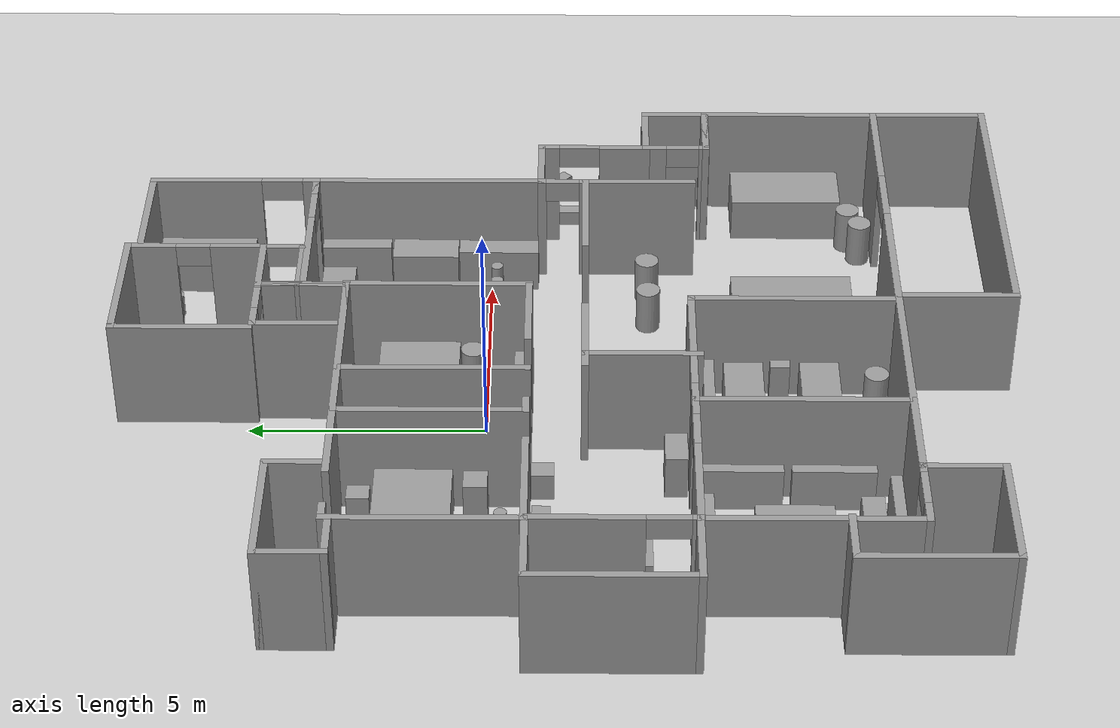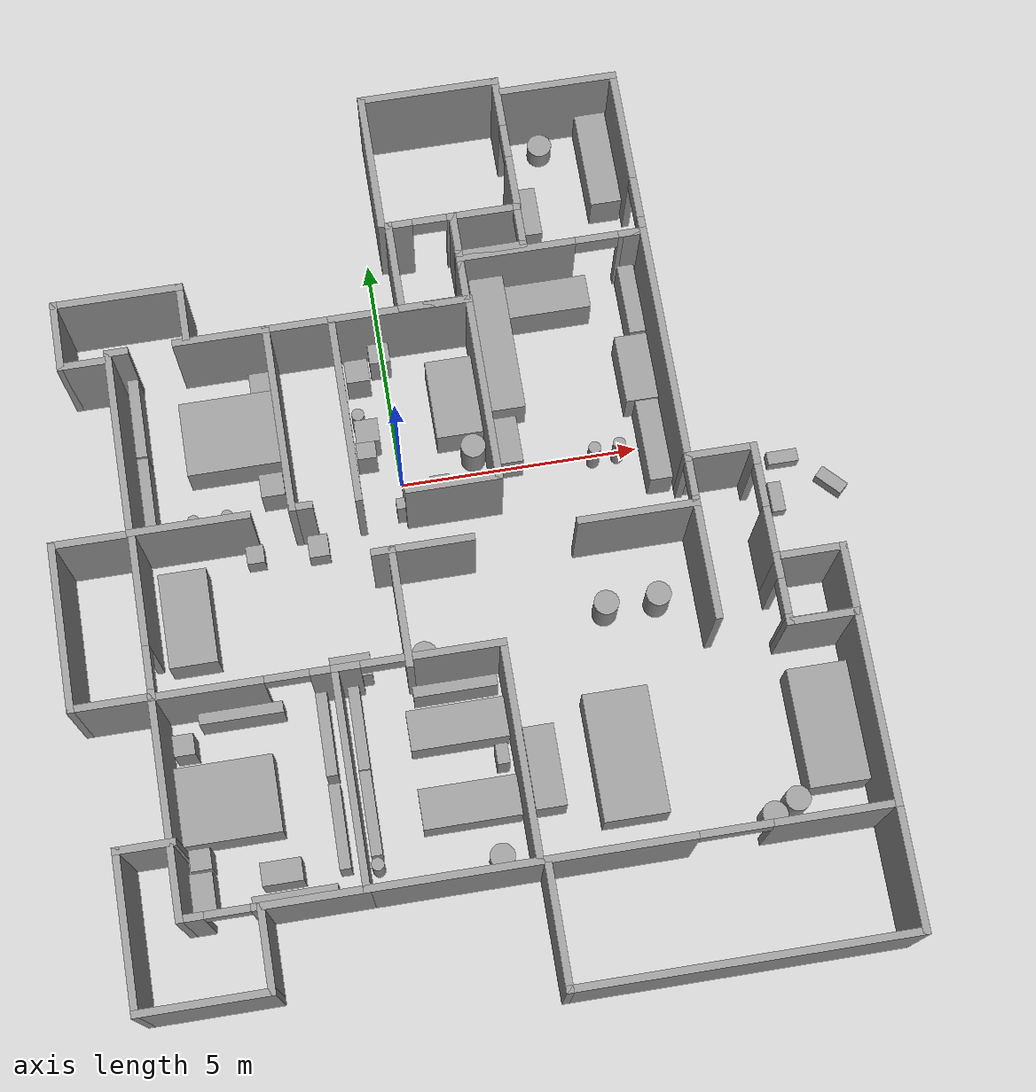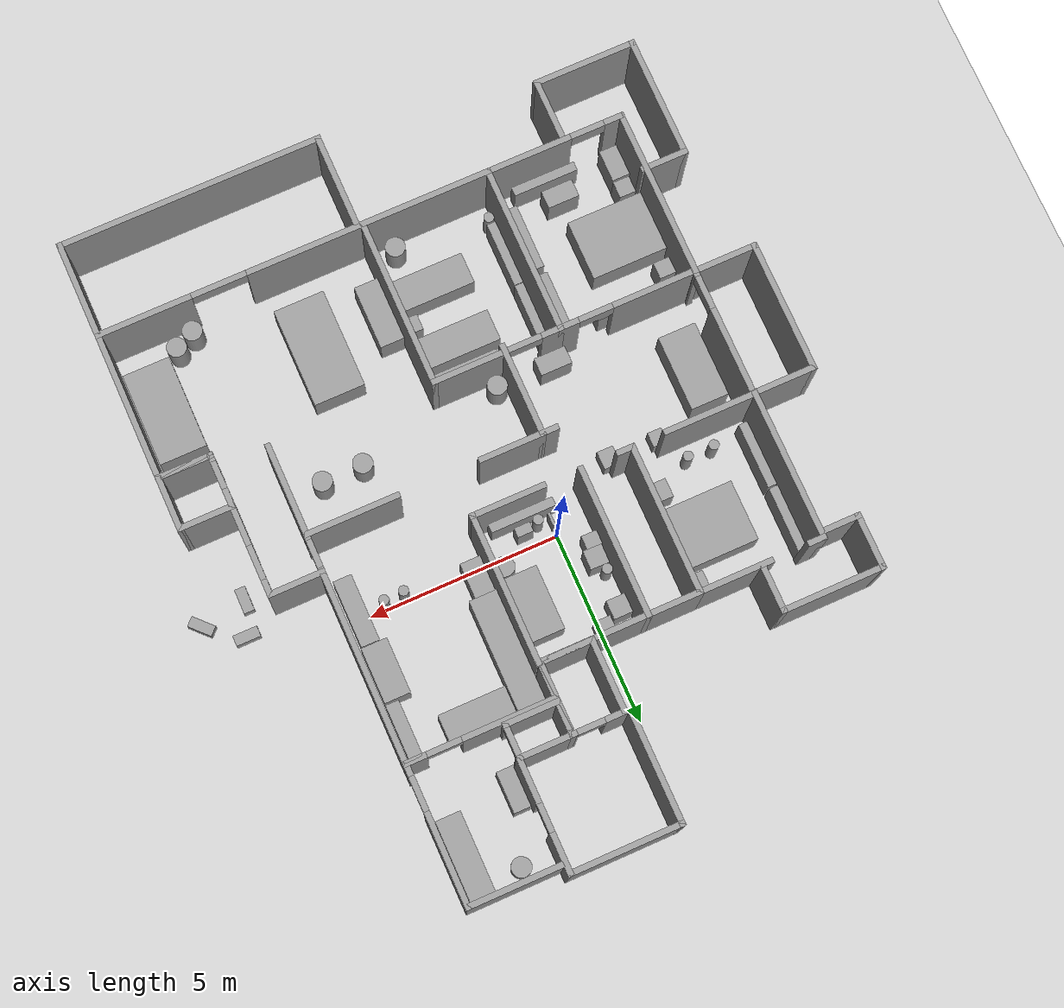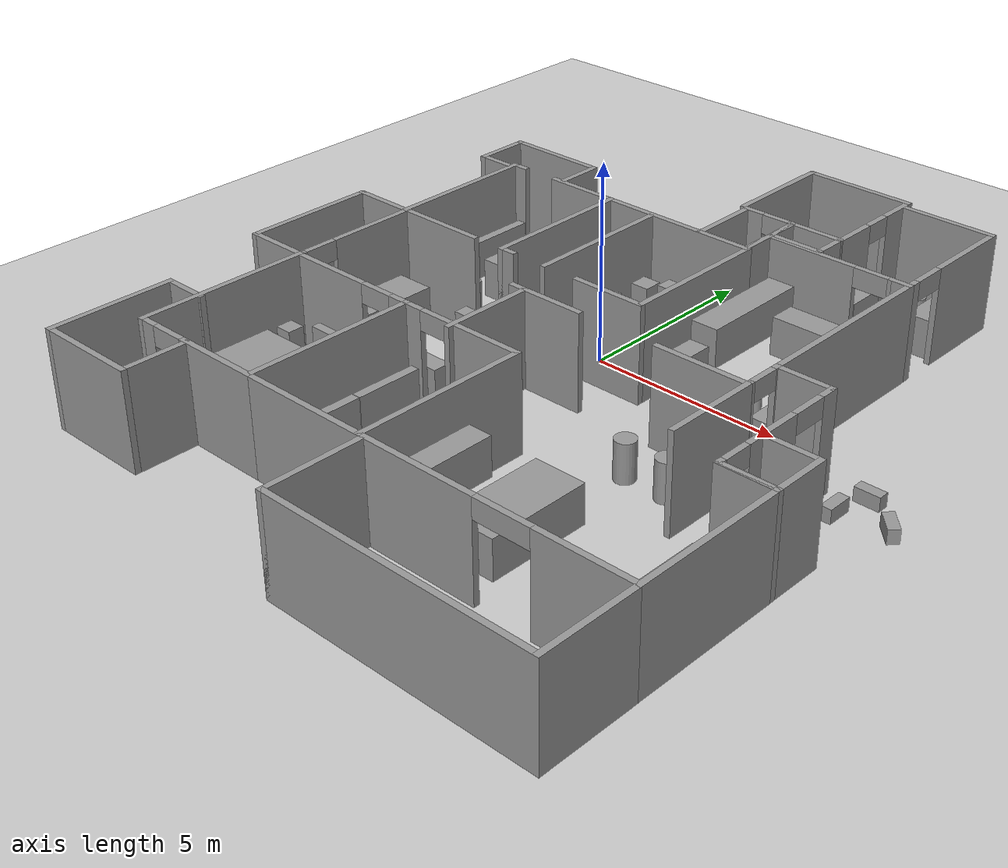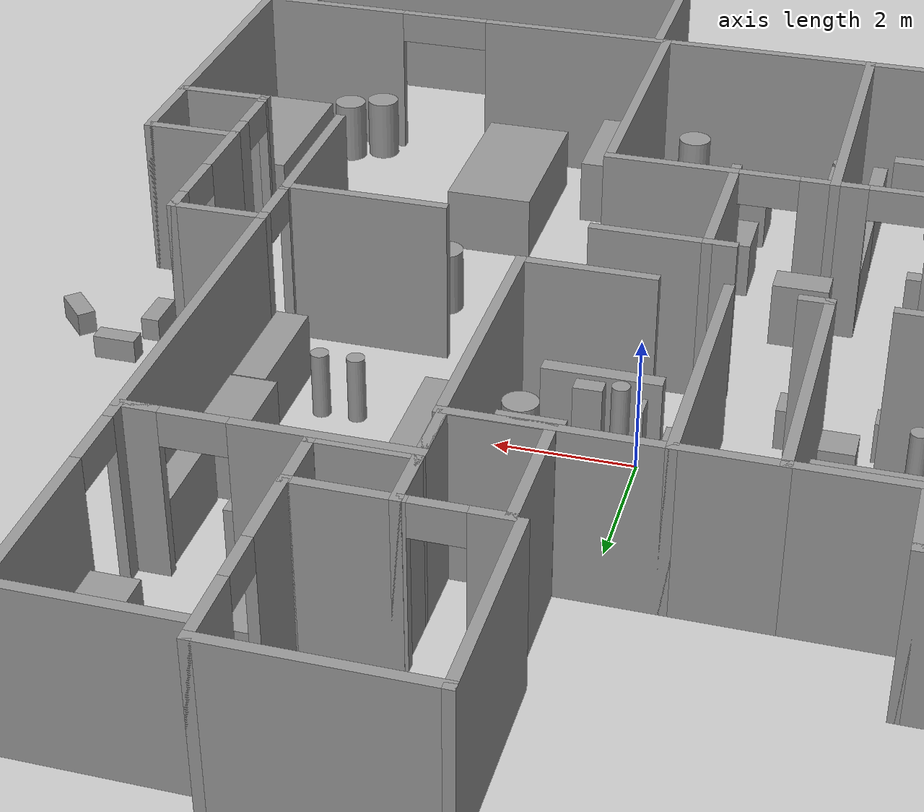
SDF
<sdf version="1.9">
 <world name="default">
  <light name="sun" type="directional">
   <pose>0 0 10 0 0 0</pose>
   <diffuse>0.800000012 0.800000012 0.800000012 1</diffuse>
   <specular>0.100000001 0.100000001 0.100000001 1</specular>
   <attenuation>
    <range>1000</range>
    <constant>0.90000000000000002</constant>
    <linear>0.01</linear>
    <quadratic>0.001</quadratic>
   </attenuation>
   <direction>-0.5 0.5 -1</direction>
   <spot><inner_angle>0</inner_angle><outer_angle>0</outer_angle><falloff>0</falloff></spot>
  </light>
  <model name="ground_plane">
   <static>true</static>
   <link name="link">
    <collision name="collision">
     <geometry><plane><normal>0 0 1</normal><size>100 100</size></plane></geometry>
     <surface><friction><ode><mu>100</mu><mu2>50</mu2></ode></friction></surface>
    </collision>
    <visual name="visual">
     <cast_shadows>false</cast_shadows>
     <geometry><plane><normal>0 0 1</normal><size>100 100</size></plane></geometry>
     <material>
      <script><uri>file://media/materials/scripts/gazebo.material</uri><name>Gazebo/Grey</name></script>
     </material>
    </visual>
   </link>
  </model>
  <gravity>0 0 -9.8000000000000007</gravity>
  <magnetic_field>6.0000000000000002e-06 2.3e-05 -4.1999999999999998e-05</magnetic_field>
  <atmosphere type="adiabatic"/>
  <physics name="default_physics" default="false" type="ode">
   <max_step_size>0.001</max_step_size>
   <real_time_factor>1</real_time_factor>
   <real_time_update_rate>1000</real_time_update_rate>
  </physics>
  <scene>
   <ambient>0.400000006 0.400000006 0.400000006 1</ambient>
   <background>0.699999988 0.699999988 0.699999988 1</background>
   <shadows>true</shadows>
  </scene>
  <spherical_coordinates>
   <surface_model>EARTH_WGS84</surface_model>
   <latitude_deg>0</latitude_deg>
   <longitude_deg>0</longitude_deg>
   <elevation>0</elevation>
   <heading_deg>0</heading_deg>
  </spherical_coordinates>
  <model name="cma_escritorio">
   <pose>-1.8304 1.03024 0 0 0 0</pose>
   <link name="Wall_11">
    <collision name="Wall_11_Collision">
     <geometry><box><size>2 0.14999999999999999 2.5</size></box></geometry>
     <pose>0 0 1.25 0 0 0</pose>
    </collision>
    <visual name="Wall_11_Visual">
     <pose>0 0 1.25 0 0 0</pose>
     <geometry><box><size>2 0.14999999999999999 2.5</size></box></geometry>
     <material>
      <script><uri>file://media/materials/scripts/gazebo.material</uri><name>Gazebo/Grey</name></script>
      <ambient>1 1 1 1</ambient>
     </material>
    </visual>
    <pose>-1.3999999999999999 1.9299999999999999 0 0 0 3.1415899999999999</pose>
   </link>
   <link name="Wall_2">
    <collision name="Wall_2_Collision">
     <geometry><box><size>4 0.14999999999999999 2.5</size></box></geometry>
     <pose>0 0 1.25 0 0 0</pose>
    </collision>
    <visual name="Wall_2_Visual">
     <pose>0 0 1.25 0 0 0</pose>
     <geometry><box><size>4 0.14999999999999999 2.5</size></box></geometry>
     <material>
      <script><uri>file://media/materials/scripts/gazebo.material</uri><name>Gazebo/Grey</name></script>
      <ambient>1 1 1 1</ambient>
     </material>
    </visual>
    <pose>0.875 0.0050000000000000001 0 0 0 1.5708</pose>
   </link>
   <link name="Wall_25">
    <collision name="Wall_25_Collision">
     <geometry><box><size>2.5 0.14999999999999999 2.5</size></box></geometry>
     <pose>0 0 1.25 0 0 0</pose>
    </collision>
    <visual name="Wall_25_Visual">
     <pose>0 0 1.25 0 0 0</pose>
     <geometry><box><size>2.5 0.14999999999999999 2.5</size></box></geometry>
     <material>
      <script><uri>file://media/materials/scripts/gazebo.material</uri><name>Gazebo/Grey</name></script>
      <ambient>1 1 1 1</ambient>
     </material>
    </visual>
    <pose>-2.5499999999999998 -1.9299999999999999 0 0 0 3.1415899999999999</pose>
   </link>
   <link name="Wall_26">
    <collision name="Wall_26_Collision">
     <geometry><box><size>4 0.14999999999999999 2.5</size></box></geometry>
     <pose>0 0 1.25 0 0 0</pose>
    </collision>
    <visual name="Wall_26_Visual">
     <pose>0 0 1.25 0 0 0</pose>
     <geometry><box><size>4 0.14999999999999999 2.5</size></box></geometry>
     <material>
      <script><uri>file://media/materials/scripts/gazebo.material</uri><name>Gazebo/Grey</name></script>
      <ambient>1 1 1 1</ambient>
     </material>
    </visual>
    <pose>-3.7250000000000001 -0.0050000000000000001 0 0 0 1.5708</pose>
   </link>
   <link name="Wall_27">
    <collision name="Wall_27_Collision">
     <geometry><box><size>0.5 0.14999999999999999 2.5</size></box></geometry>
     <pose>0 0 1.25 0 0 0</pose>
    </collision>
    <visual name="Wall_27_Visual">
     <pose>0 0 1.25 0 0 0</pose>
     <geometry><box><size>0.5 0.14999999999999999 2.5</size></box></geometry>
     <material>
      <script><uri>file://media/materials/scripts/gazebo.material</uri><name>Gazebo/Grey</name></script>
      <ambient>1 1 1 1</ambient>
     </material>
    </visual>
    <pose>-3.5499999999999998 1.9199999999999999 0 0 0 0</pose>
   </link>
   <link name="Wall_3">
    <collision name="Wall_3_Collision">
     <geometry><box><size>3 0.14999999999999999 2.5</size></box></geometry>
     <pose>0 0 1.25 0 0 0</pose>
    </collision>
    <visual name="Wall_3_Visual">
     <pose>0 0 1.25 0 0 0</pose>
     <geometry><box><size>3 0.14999999999999999 2.5</size></box></geometry>
     <material>
      <script><uri>file://media/materials/scripts/gazebo.material</uri><name>Gazebo/Grey</name></script>
      <ambient>1 1 1 1</ambient>
     </material>
    </visual>
    <pose>2.2999999999999998 1.9299999999999999 0 0 0 0</pose>
   </link>
   <link name="Wall_4">
    <collision name="Wall_4_Collision">
     <geometry><box><size>4 0.14999999999999999 2.5</size></box></geometry>
     <pose>0 0 1.25 0 0 0</pose>
    </collision>
    <visual name="Wall_4_Visual">
     <pose>0 0 1.25 0 0 0</pose>
     <geometry><box><size>4 0.14999999999999999 2.5</size></box></geometry>
     <material>
      <script><uri>file://media/materials/scripts/gazebo.material</uri><name>Gazebo/Grey</name></script>
      <ambient>1 1 1 1</ambient>
     </material>
    </visual>
    <pose>3.7250000000000001 0.0050000000000000001 0 0 0 -1.5708</pose>
   </link>
   <link name="Wall_5">
    <collision name="Wall_5_Collision">
     <geometry><box><size>2 0.14999999999999999 2.5</size></box></geometry>
     <pose>0 0 1.25 0 0 0</pose>
    </collision>
    <visual name="Wall_5_Visual">
     <pose>0 0 1.25 0 0 0</pose>
     <geometry><box><size>2 0.14999999999999999 2.5</size></box></geometry>
     <material>
      <script><uri>file://media/materials/scripts/gazebo.material</uri><name>Gazebo/Grey</name></script>
      <ambient>1 1 1 1</ambient>
     </material>
    </visual>
    <pose>2.7999999999999998 -1.9199999999999999 0 0 0 3.1415899999999999</pose>
   </link>
   <link name="Wall_7">
    <collision name="Wall_7_Collision">
     <geometry><box><size>1.5 0.14999999999999999 2.5</size></box></geometry>
     <pose>0 0 1.25 0 0 0</pose>
    </collision>
    <visual name="Wall_7_Visual">
     <pose>0 0 1.25 0 0 0</pose>
     <geometry><box><size>1.5 0.14999999999999999 2.5</size></box></geometry>
     <material>
      <script><uri>file://media/materials/scripts/gazebo.material</uri><name>Gazebo/Grey</name></script>
      <ambient>1 1 1 1</ambient>
     </material>
    </visual>
    <pose>0.20000000000000001 1.9299999999999999 0 0 0 3.1415899999999999</pose>
   </link>
   <link name="Wall_8">
    <collision name="Wall_8_Collision">
     <geometry><box><size>4 0.14999999999999999 2.5</size></box></geometry>
     <pose>0 0 1.25 0 0 0</pose>
    </collision>
    <visual name="Wall_8_Visual">
     <pose>0 0 1.25 0 0 0</pose>
     <geometry><box><size>4 0.14999999999999999 2.5</size></box></geometry>
     <material>
      <script><uri>file://media/materials/scripts/gazebo.material</uri><name>Gazebo/Grey</name></script>
      <ambient>1 1 1 1</ambient>
     </material>
    </visual>
    <pose>-0.47499999999999998 0.0050000000000000001 0 0 0 -1.5708</pose>
   </link>
   <link name="Wall_9">
    <collision name="Wall_9_Collision">
     <geometry><box><size>0.5 0.14999999999999999 2.5</size></box></geometry>
     <pose>0 0 1.25 0 0 0</pose>
    </collision>
    <visual name="Wall_9_Visual">
     <pose>0 0 1.25 0 0 0</pose>
     <geometry><box><size>0.5 0.14999999999999999 2.5</size></box></geometry>
     <material>
      <script><uri>file://media/materials/scripts/gazebo.material</uri><name>Gazebo/Grey</name></script>
      <ambient>1 1 1 1</ambient>
     </material>
    </visual>
    <pose>-0.29999999999999999 -1.9199999999999999 0 0 0 0</pose>
   </link>
   <static>true</static>
  </model>
  <model name="cma_banheiro">
   <pose>-5.2292800000000002 3.4870999999999999 0 0 0 0</pose>
   <link name="Wall_0">
    <collision name="Wall_0_Collision">
     <geometry><box><size>1 0.14999999999999999 2.5</size></box></geometry>
     <pose>0 0 1.25 0 0 0</pose>
    </collision>
    <visual name="Wall_0_Visual">
     <pose>0 0 1.25 0 0 0</pose>
     <geometry><box><size>1 0.14999999999999999 2.5</size></box></geometry>
     <material>
      <script><uri>file://media/materials/scripts/gazebo.material</uri><name>Gazebo/Grey</name></script>
      <ambient>1 1 1 1</ambient>
     </material>
    </visual>
    <pose>-0.875 -0.67500000000000004 0 0 0 3.1415899999999999</pose>
   </link>
   <link name="Wall_1">
    <collision name="Wall_1_Collision">
     <geometry><box><size>1.5 0.14999999999999999 2.5</size></box></geometry>
     <pose>0 0 1.25 0 0 0</pose>
    </collision>
    <visual name="Wall_1_Visual">
     <pose>0 0 1.25 0 0 0</pose>
     <geometry><box><size>1.5 0.14999999999999999 2.5</size></box></geometry>
     <material>
      <script><uri>file://media/materials/scripts/gazebo.material</uri><name>Gazebo/Grey</name></script>
      <ambient>1 1 1 1</ambient>
     </material>
    </visual>
    <pose>-1.3 0 0 0 0 1.5708</pose>
   </link>
   <link name="Wall_2">
    <collision name="Wall_2_Collision">
     <geometry><box><size>2.75 0.14999999999999999 2.5</size></box></geometry>
     <pose>0 0 1.25 0 0 0</pose>
    </collision>
    <visual name="Wall_2_Visual">
     <pose>0 0 1.25 0 0 0</pose>
     <geometry><box><size>2.75 0.14999999999999999 2.5</size></box></geometry>
     <material>
      <script><uri>file://media/materials/scripts/gazebo.material</uri><name>Gazebo/Grey</name></script>
      <ambient>1 1 1 1</ambient>
     </material>
    </visual>
    <pose>0 0.67500000000000004 0 0 0 0</pose>
   </link>
   <link name="Wall_4">
    <collision name="Wall_4_Collision">
     <geometry><box><size>1.25 0.14999999999999999 2.5</size></box></geometry>
     <pose>0 0 1.25 0 0 0</pose>
    </collision>
    <visual name="Wall_4_Visual">
     <pose>0 0 1.25 0 0 0</pose>
     <geometry><box><size>1.25 0.14999999999999999 2.5</size></box></geometry>
     <material>
      <script><uri>file://media/materials/scripts/gazebo.material</uri><name>Gazebo/Grey</name></script>
      <ambient>1 1 1 1</ambient>
     </material>
    </visual>
    <pose>1.3 0.125 0 0 0 -1.5708</pose>
   </link>
   <static>true</static>
  </model>
  <model name="cma_varanda1">
   <pose>-6.3251799999999996 -2.5931299999999999 0 0 0 0</pose>
   <link name="Wall_0">
    <pose>0.80000000000000004 0 0 0 0 -1.5708</pose>
    <visual name="Wall_0_Visual_0">
     <pose>-0.55249999999999999 0 1.25 0 0 0</pose>
     <geometry><box><size>2.395 0.14999999999999999 2.5</size></box></geometry>
     <material>
      <script><uri>file://media/materials/scripts/gazebo.material</uri><name>Gazebo/Grey</name></script>
      <ambient>1 1 1 1</ambient>
     </material>
    </visual>
    <collision name="Wall_0_Collision_0">
     <geometry><box><size>2.395 0.14999999999999999 2.5</size></box></geometry>
     <pose>-0.55249999999999999 0 1.25 0 0 0</pose>
    </collision>
    <visual name="Wall_0_Visual_1">
     <pose>1.6375 0 1.25 0 0 0</pose>
     <geometry><box><size>0.22500000000000001 0.14999999999999999 2.5</size></box></geometry>
     <material>
      <script><uri>file://media/materials/scripts/gazebo.material</uri><name>Gazebo/Grey</name></script>
      <ambient>1 1 1 1</ambient>
     </material>
    </visual>
    <collision name="Wall_0_Collision_1">
     <geometry><box><size>0.22500000000000001 0.14999999999999999 2.5</size></box></geometry>
     <pose>1.6375 0 1.25 0 0 0</pose>
    </collision>
    <visual name="Wall_0_Visual_2">
     <pose>1.085 0 2.25 0 0 0</pose>
     <geometry><box><size>0.88 0.14999999999999999 0.5</size></box></geometry>
     <material>
      <script><uri>file://media/materials/scripts/gazebo.material</uri><name>Gazebo/Grey</name></script>
      <ambient>1 1 1 1</ambient>
     </material>
    </visual>
    <collision name="Wall_0_Collision_2">
     <geometry><box><size>0.88 0.14999999999999999 0.5</size></box></geometry>
     <pose>1.085 0 2.25 0 0 0</pose>
    </collision>
   </link>
   <link name="Wall_1">
    <collision name="Wall_1_Collision">
     <geometry><box><size>1.75 0.14999999999999999 2.5</size></box></geometry>
     <pose>0 0 1.25 0 0 0</pose>
    </collision>
    <visual name="Wall_1_Visual">
     <pose>0 0 1.25 0 0 0</pose>
     <geometry><box><size>1.75 0.14999999999999999 2.5</size></box></geometry>
     <material>
      <script><uri>file://media/materials/scripts/gazebo.material</uri><name>Gazebo/Grey</name></script>
      <ambient>1 1 1 1</ambient>
     </material>
    </visual>
    <pose>0 -1.675 0 0 0 3.1415899999999999</pose>
   </link>
   <link name="Wall_2">
    <collision name="Wall_2_Collision">
     <geometry><box><size>3.5 0.14999999999999999 2.5</size></box></geometry>
     <pose>0 0 1.25 0 0 0</pose>
    </collision>
    <visual name="Wall_2_Visual">
     <pose>0 0 1.25 0 0 0</pose>
     <geometry><box><size>3.5 0.14999999999999999 2.5</size></box></geometry>
     <material>
      <script><uri>file://media/materials/scripts/gazebo.material</uri><name>Gazebo/Grey</name></script>
      <ambient>1 1 1 1</ambient>
     </material>
    </visual>
    <pose>-0.80000000000000004 0 0 0 0 1.5708</pose>
   </link>
   <link name="Wall_3">
    <collision name="Wall_3_Collision">
     <geometry><box><size>1.75 0.14999999999999999 2.5</size></box></geometry>
     <pose>0 0 1.25 0 0 0</pose>
    </collision>
    <visual name="Wall_3_Visual">
     <pose>0 0 1.25 0 0 0</pose>
     <geometry><box><size>1.75 0.14999999999999999 2.5</size></box></geometry>
     <material>
      <script><uri>file://media/materials/scripts/gazebo.material</uri><name>Gazebo/Grey</name></script>
      <ambient>1 1 1 1</ambient>
     </material>
    </visual>
    <pose>0 1.675 0 0 0 0</pose>
   </link>
   <static>true</static>
  </model>
  <model name="cma_quartos">
   <pose>-2.58169 -7.2645600000000004 0 0 0 0</pose>
   <link name="Wall_0">
    <collision name="Wall_0_Collision">
     <geometry><box><size>4.5 0.14999999999999999 2.5</size></box></geometry>
     <pose>0 0 1.25 0 0 0</pose>
    </collision>
    <visual name="Wall_0_Visual">
     <pose>0 0 1.25 0 0 0</pose>
     <geometry><box><size>4.5 0.14999999999999999 2.5</size></box></geometry>
     <material>
      <script><uri>file://media/materials/scripts/gazebo.material</uri><name>Gazebo/Grey</name></script>
      <ambient>1 1 1 1</ambient>
     </material>
    </visual>
    <pose>0.64500000000000002 0.81000000000000005 0 0 0 -1.5708</pose>
   </link>
   <link name="Wall_1">
    <pose>-1.155 -1.365 0 0 0 3.1415899999999999</pose>
    <visual name="Wall_1_Visual_0">
     <pose>-0.72250000000000003 0 1.25 0 0 0</pose>
     <geometry><box><size>2.3050000000000002 0.14999999999999999 2.5</size></box></geometry>
     <material>
      <script><uri>file://media/materials/scripts/gazebo.material</uri><name>Gazebo/Grey</name></script>
      <ambient>1 1 1 1</ambient>
     </material>
    </visual>
    <collision name="Wall_1_Collision_0">
     <geometry><box><size>2.3050000000000002 0.14999999999999999 2.5</size></box></geometry>
     <pose>-0.72250000000000003 0 1.25 0 0 0</pose>
    </collision>
    <visual name="Wall_1_Visual_1">
     <pose>1.6025 0 1.25 0 0 0</pose>
     <geometry><box><size>0.54500000000000004 0.14999999999999999 2.5</size></box></geometry>
     <material>
      <script><uri>file://media/materials/scripts/gazebo.material</uri><name>Gazebo/Grey</name></script>
      <ambient>1 1 1 1</ambient>
     </material>
    </visual>
    <collision name="Wall_1_Collision_1">
     <geometry><box><size>0.54500000000000004 0.14999999999999999 2.5</size></box></geometry>
     <pose>1.6025 0 1.25 0 0 0</pose>
    </collision>
    <visual name="Wall_1_Visual_2">
     <pose>0.88 0 2.25 0 0 0</pose>
     <geometry><box><size>0.90000000000000002 0.14999999999999999 0.5</size></box></geometry>
     <material>
      <script><uri>file://media/materials/scripts/gazebo.material</uri><name>Gazebo/Grey</name></script>
      <ambient>1 1 1 1</ambient>
     </material>
    </visual>
    <collision name="Wall_1_Collision_2">
     <geometry><box><size>0.90000000000000002 0.14999999999999999 0.5</size></box></geometry>
     <pose>0.88 0 2.25 0 0 0</pose>
    </collision>
   </link>
   <link name="Wall_10">
    <collision name="Wall_10_Collision">
     <geometry><box><size>1.75 0.14999999999999999 2.5</size></box></geometry>
     <pose>0 0 1.25 0 0 0</pose>
    </collision>
    <visual name="Wall_10_Visual">
     <pose>0 0 1.25 0 0 0</pose>
     <geometry><box><size>1.75 0.14999999999999999 2.5</size></box></geometry>
     <material>
      <script><uri>file://media/materials/scripts/gazebo.material</uri><name>Gazebo/Grey</name></script>
      <ambient>1 1 1 1</ambient>
     </material>
    </visual>
    <pose>-1.395 -2.1850000000000001 0 0 0 -1.5708</pose>
   </link>
   <link name="Wall_11">
    <collision name="Wall_11_Collision">
     <geometry><box><size>2.75 0.14999999999999999 2.5</size></box></geometry>
     <pose>0 0 1.25 0 0 0</pose>
    </collision>
    <visual name="Wall_11_Visual">
     <pose>0 0 1.25 0 0 0</pose>
     <geometry><box><size>2.75 0.14999999999999999 2.5</size></box></geometry>
     <material>
      <script><uri>file://media/materials/scripts/gazebo.material</uri><name>Gazebo/Grey</name></script>
      <ambient>1 1 1 1</ambient>
     </material>
    </visual>
    <pose>-2.6949999999999998 -2.9849999999999999 0 0 0 3.1415899999999999</pose>
   </link>
   <link name="Wall_12">
    <collision name="Wall_12_Collision">
     <geometry><box><size>3.25 0.14999999999999999 2.5</size></box></geometry>
     <pose>0 0 1.25 0 0 0</pose>
    </collision>
    <visual name="Wall_12_Visual">
     <pose>0 0 1.25 0 0 0</pose>
     <geometry><box><size>3.25 0.14999999999999999 2.5</size></box></geometry>
     <material>
      <script><uri>file://media/materials/scripts/gazebo.material</uri><name>Gazebo/Grey</name></script>
      <ambient>1 1 1 1</ambient>
     </material>
    </visual>
    <pose>-3.9950000000000001 -1.4350000000000001 0 0 0 1.5708</pose>
   </link>
   <link name="Wall_13">
    <collision name="Wall_13_Collision">
     <geometry><box><size>1.25 0.14999999999999999 2.5</size></box></geometry>
     <pose>0 0 1.25 0 0 0</pose>
    </collision>
    <visual name="Wall_13_Visual">
     <pose>0 0 1.25 0 0 0</pose>
     <geometry><box><size>1.25 0.14999999999999999 2.5</size></box></geometry>
     <material>
      <script><uri>file://media/materials/scripts/gazebo.material</uri><name>Gazebo/Grey</name></script>
      <ambient>1 1 1 1</ambient>
     </material>
    </visual>
    <pose>-3.4449999999999998 0.115 0 0 0 0</pose>
   </link>
   <link name="Wall_2">
    <collision name="Wall_2_Collision">
     <geometry><box><size>4.5 0.14999999999999999 2.5</size></box></geometry>
     <pose>0 0 1.25 0 0 0</pose>
    </collision>
    <visual name="Wall_2_Visual">
     <pose>0 0 1.25 0 0 0</pose>
     <geometry><box><size>4.5 0.14999999999999999 2.5</size></box></geometry>
     <material>
      <script><uri>file://media/materials/scripts/gazebo.material</uri><name>Gazebo/Grey</name></script>
      <ambient>1 1 1 1</ambient>
     </material>
    </visual>
    <pose>-2.9550000000000001 0.81000000000000005 0 0 0 1.5708</pose>
   </link>
   <link name="Wall_3">
    <pose>-1.155 2.9849999999999999 0 0 0 0</pose>
    <visual name="Wall_3_Visual_0">
     <pose>-0.73250000000000004 0 1.25 0 0 0</pose>
     <geometry><box><size>2.2850000000000001 0.14999999999999999 2.5</size></box></geometry>
     <material>
      <script><uri>file://media/materials/scripts/gazebo.material</uri><name>Gazebo/Grey</name></script>
      <ambient>1 1 1 1</ambient>
     </material>
    </visual>
    <collision name="Wall_3_Collision_0">
     <geometry><box><size>2.2850000000000001 0.14999999999999999 2.5</size></box></geometry>
     <pose>-0.73250000000000004 0 1.25 0 0 0</pose>
    </collision>
    <visual name="Wall_3_Visual_1">
     <pose>1.5925 0 1.25 0 0 0</pose>
     <geometry><box><size>0.56499999999999995 0.14999999999999999 2.5</size></box></geometry>
     <material>
      <script><uri>file://media/materials/scripts/gazebo.material</uri><name>Gazebo/Grey</name></script>
      <ambient>1 1 1 1</ambient>
     </material>
    </visual>
    <collision name="Wall_3_Collision_1">
     <geometry><box><size>0.56499999999999995 0.14999999999999999 2.5</size></box></geometry>
     <pose>1.5925 0 1.25 0 0 0</pose>
    </collision>
    <visual name="Wall_3_Visual_2">
     <pose>0.85999999999999999 0 2.25 0 0 0</pose>
     <geometry><box><size>0.90000000000000002 0.14999999999999999 0.5</size></box></geometry>
     <material>
      <script><uri>file://media/materials/scripts/gazebo.material</uri><name>Gazebo/Grey</name></script>
      <ambient>1 1 1 1</ambient>
     </material>
    </visual>
    <collision name="Wall_3_Collision_2">
     <geometry><box><size>0.90000000000000002 0.14999999999999999 0.5</size></box></geometry>
     <pose>0.85999999999999999 0 2.25 0 0 0</pose>
    </collision>
   </link>
   <link name="Wall_6">
    <pose>2.3199999999999998 2.9849999999999999 0 0 0 0</pose>
    <visual name="Wall_6_Visual_0">
     <pose>-1.4575 0 1.25 0 0 0</pose>
     <geometry><box><size>0.58499999999999996 0.14999999999999999 2.5</size></box></geometry>
     <material>
      <script><uri>file://media/materials/scripts/gazebo.material</uri><name>Gazebo/Grey</name></script>
      <ambient>1 1 1 1</ambient>
     </material>
    </visual>
    <collision name="Wall_6_Collision_0">
     <geometry><box><size>0.58499999999999996 0.14999999999999999 2.5</size></box></geometry>
     <pose>-1.4575 0 1.25 0 0 0</pose>
    </collision>
    <visual name="Wall_6_Visual_1">
     <pose>0.74250000000000005 0 1.25 0 0 0</pose>
     <geometry><box><size>2.0150000000000001 0.14999999999999999 2.5</size></box></geometry>
     <material>
      <script><uri>file://media/materials/scripts/gazebo.material</uri><name>Gazebo/Grey</name></script>
      <ambient>1 1 1 1</ambient>
     </material>
    </visual>
    <collision name="Wall_6_Collision_1">
     <geometry><box><size>2.0150000000000001 0.14999999999999999 2.5</size></box></geometry>
     <pose>0.74250000000000005 0 1.25 0 0 0</pose>
    </collision>
    <visual name="Wall_6_Visual_2">
     <pose>-0.71499999999999997 0 2.25 0 0 0</pose>
     <geometry><box><size>0.90000000000000002 0.14999999999999999 0.5</size></box></geometry>
     <material>
      <script><uri>file://media/materials/scripts/gazebo.material</uri><name>Gazebo/Grey</name></script>
      <ambient>1 1 1 1</ambient>
     </material>
    </visual>
    <collision name="Wall_6_Collision_2">
     <geometry><box><size>0.90000000000000002 0.14999999999999999 0.5</size></box></geometry>
     <pose>-0.71499999999999997 0 2.25 0 0 0</pose>
    </collision>
   </link>
   <link name="Wall_7">
    <collision name="Wall_7_Collision">
     <geometry><box><size>4.5 0.14999999999999999 2.5</size></box></geometry>
     <pose>0 0 1.25 0 0 0</pose>
    </collision>
    <visual name="Wall_7_Visual">
     <pose>0 0 1.25 0 0 0</pose>
     <geometry><box><size>4.5 0.14999999999999999 2.5</size></box></geometry>
     <material>
      <script><uri>file://media/materials/scripts/gazebo.material</uri><name>Gazebo/Grey</name></script>
      <ambient>1 1 1 1</ambient>
     </material>
    </visual>
    <pose>3.9950000000000001 0.81000000000000005 0 0 0 -1.5708</pose>
   </link>
   <link name="Wall_8">
    <collision name="Wall_8_Collision">
     <geometry><box><size>3.5 0.14999999999999999 2.5</size></box></geometry>
     <pose>0 0 1.25 0 0 0</pose>
    </collision>
    <visual name="Wall_8_Visual">
     <pose>0 0 1.25 0 0 0</pose>
     <geometry><box><size>3.5 0.14999999999999999 2.5</size></box></geometry>
     <material>
      <script><uri>file://media/materials/scripts/gazebo.material</uri><name>Gazebo/Grey</name></script>
      <ambient>1 1 1 1</ambient>
     </material>
    </visual>
    <pose>2.3199999999999998 -1.365 0 0 0 3.1415899999999999</pose>
   </link>
   <static>true</static>
  </model>
  <model name="cma_parede_t">
   <pose>0.15995500000000001 -3.2401599999999999 0 0 0 0</pose>
   <link name="Wall_15">
    <collision name="Wall_15_Collision">
     <geometry><box><size>2.5 0.14999999999999999 2.5</size></box></geometry>
     <pose>0 0 1.25 0 0 0</pose>
    </collision>
    <visual name="Wall_15_Visual">
     <pose>0 0 1.25 0 0 0</pose>
     <geometry><box><size>2.5 0.14999999999999999 2.5</size></box></geometry>
     <material>
      <script><uri>file://media/materials/scripts/gazebo.material</uri><name>Gazebo/Grey</name></script>
      <ambient>1 1 1 1</ambient>
     </material>
    </visual>
    <pose>-0.625 0 0 0 0 1.5708</pose>
   </link>
   <link name="Wall_16">
    <collision name="Wall_16_Collision">
     <geometry><box><size>0.5 0.14999999999999999 2.5</size></box></geometry>
     <pose>0 0 1.25 0 0 0</pose>
    </collision>
    <visual name="Wall_16_Visual">
     <pose>0 0 1.25 0 0 0</pose>
     <geometry><box><size>0.5 0.14999999999999999 2.5</size></box></geometry>
     <material>
      <script><uri>file://media/materials/scripts/gazebo.material</uri><name>Gazebo/Grey</name></script>
      <ambient>1 1 1 1</ambient>
     </material>
    </visual>
    <pose>-0.80000000000000004 1.175 0 0 0 3.1415899999999999</pose>
   </link>
   <link name="Wall_18">
    <collision name="Wall_18_Collision">
     <geometry><box><size>1.75 0.14999999999999999 2.5</size></box></geometry>
     <pose>0 0 1.25 0 0 0</pose>
    </collision>
    <visual name="Wall_18_Visual">
     <pose>0 0 1.25 0 0 0</pose>
     <geometry><box><size>1.75 0.14999999999999999 2.5</size></box></geometry>
     <material>
      <script><uri>file://media/materials/scripts/gazebo.material</uri><name>Gazebo/Grey</name></script>
      <ambient>1 1 1 1</ambient>
     </material>
    </visual>
    <pose>0.17499999999999999 1.175 0 0 0 0</pose>
   </link>
   <static>true</static>
  </model>
  <model name="cma_parede_L">
   <pose>4.97628 -6.6999199999999997 0 0 0 0</pose>
   <link name="Wall_0">
    <pose>0 -1.925 0 0 0 0</pose>
    <visual name="Wall_0_Visual_0">
     <pose>-1.9850000000000001 0 1.25 0 0 0</pose>
     <geometry><box><size>3.0299999999999998 0.14999999999999999 2.5</size></box></geometry>
     <material>
      <script><uri>file://media/materials/scripts/gazebo.material</uri><name>Gazebo/Grey</name></script>
      <ambient>1 1 1 1</ambient>
     </material>
    </visual>
    <collision name="Wall_0_Collision_0">
     <geometry><box><size>3.0299999999999998 0.14999999999999999 2.5</size></box></geometry>
     <pose>-1.9850000000000001 0 1.25 0 0 0</pose>
    </collision>
    <visual name="Wall_0_Visual_1">
     <pose>2.2400000000000002 0 1.25 0 0 0</pose>
     <geometry><box><size>2.52 0.14999999999999999 2.5</size></box></geometry>
     <material>
      <script><uri>file://media/materials/scripts/gazebo.material</uri><name>Gazebo/Grey</name></script>
      <ambient>1 1 1 1</ambient>
     </material>
    </visual>
    <collision name="Wall_0_Collision_1">
     <geometry><box><size>2.52 0.14999999999999999 2.5</size></box></geometry>
     <pose>2.2400000000000002 0 1.25 0 0 0</pose>
    </collision>
    <visual name="Wall_0_Visual_2">
     <pose>0.255 0 2.25 0 0 0</pose>
     <geometry><box><size>1.45 0.14999999999999999 0.5</size></box></geometry>
     <material>
      <script><uri>file://media/materials/scripts/gazebo.material</uri><name>Gazebo/Grey</name></script>
      <ambient>1 1 1 1</ambient>
     </material>
    </visual>
    <collision name="Wall_0_Collision_2">
     <geometry><box><size>1.45 0.14999999999999999 0.5</size></box></geometry>
     <pose>0.255 0 2.25 0 0 0</pose>
    </collision>
   </link>
   <link name="Wall_1">
    <collision name="Wall_1_Collision">
     <geometry><box><size>4 0.14999999999999999 2.5</size></box></geometry>
     <pose>0 0 1.25 0 0 0</pose>
    </collision>
    <visual name="Wall_1_Visual">
     <pose>0 0 1.25 0 0 0</pose>
     <geometry><box><size>4 0.14999999999999999 2.5</size></box></geometry>
     <material>
      <script><uri>file://media/materials/scripts/gazebo.material</uri><name>Gazebo/Grey</name></script>
      <ambient>1 1 1 1</ambient>
     </material>
    </visual>
    <pose>3.4249999999999998 0 0 0 0 1.5708</pose>
   </link>
   <link name="Wall_2">
    <collision name="Wall_2_Collision">
     <geometry><box><size>1.5 0.14999999999999999 2.5</size></box></geometry>
     <pose>0 0 1.25 0 0 0</pose>
    </collision>
    <visual name="Wall_2_Visual">
     <pose>0 0 1.25 0 0 0</pose>
     <geometry><box><size>1.5 0.14999999999999999 2.5</size></box></geometry>
     <material>
      <script><uri>file://media/materials/scripts/gazebo.material</uri><name>Gazebo/Grey</name></script>
      <ambient>1 1 1 1</ambient>
     </material>
    </visual>
    <pose>2.75 1.925 0 0 0 3.1415899999999999</pose>
   </link>
   <static>true</static>
  </model>
  <model name="cma_lavabo">
   <pose>7.7229700000000001 -4.0930200000000001 0 0 0 0</pose>
   <link name="Wall_4">
    <pose>-0.67500000000000004 0 0 0 0 1.5708</pose>
    <visual name="Wall_4_Visual_0">
     <pose>-0.63500000000000001 0 1.25 0 0 0</pose>
     <geometry><box><size>0.23000000000000001 0.14999999999999999 2.5</size></box></geometry>
     <material>
      <script><uri>file://media/materials/scripts/gazebo.material</uri><name>Gazebo/Grey</name></script>
      <ambient>1 1 1 1</ambient>
     </material>
    </visual>
    <collision name="Wall_4_Collision_0">
     <geometry><box><size>0.23000000000000001 0.14999999999999999 2.5</size></box></geometry>
     <pose>-0.63500000000000001 0 1.25 0 0 0</pose>
    </collision>
    <visual name="Wall_4_Visual_1">
     <pose>0.47999999999999998 0 1.25 0 0 0</pose>
     <geometry><box><size>0.54000000000000004 0.14999999999999999 2.5</size></box></geometry>
     <material>
      <script><uri>file://media/materials/scripts/gazebo.material</uri><name>Gazebo/Grey</name></script>
      <ambient>1 1 1 1</ambient>
     </material>
    </visual>
    <collision name="Wall_4_Collision_1">
     <geometry><box><size>0.54000000000000004 0.14999999999999999 2.5</size></box></geometry>
     <pose>0.47999999999999998 0 1.25 0 0 0</pose>
    </collision>
    <visual name="Wall_4_Visual_2">
     <pose>-0.155 0 2.25 0 0 0</pose>
     <geometry><box><size>0.72999999999999998 0.14999999999999999 0.5</size></box></geometry>
     <material>
      <script><uri>file://media/materials/scripts/gazebo.material</uri><name>Gazebo/Grey</name></script>
      <ambient>1 1 1 1</ambient>
     </material>
    </visual>
    <collision name="Wall_4_Collision_2">
     <geometry><box><size>0.72999999999999998 0.14999999999999999 0.5</size></box></geometry>
     <pose>-0.155 0 2.25 0 0 0</pose>
    </collision>
   </link>
   <link name="Wall_5">
    <collision name="Wall_5_Collision">
     <geometry><box><size>1.5 0.14999999999999999 2.5</size></box></geometry>
     <pose>0 0 1.25 0 0 0</pose>
    </collision>
    <visual name="Wall_5_Visual">
     <pose>0 0 1.25 0 0 0</pose>
     <geometry><box><size>1.5 0.14999999999999999 2.5</size></box></geometry>
     <material>
      <script><uri>file://media/materials/scripts/gazebo.material</uri><name>Gazebo/Grey</name></script>
      <ambient>1 1 1 1</ambient>
     </material>
    </visual>
    <pose>0 0.67500000000000004 0 0 0 0</pose>
   </link>
   <link name="Wall_6">
    <collision name="Wall_6_Collision">
     <geometry><box><size>1.5 0.14999999999999999 2.5</size></box></geometry>
     <pose>0 0 1.25 0 0 0</pose>
    </collision>
    <visual name="Wall_6_Visual">
     <pose>0 0 1.25 0 0 0</pose>
     <geometry><box><size>1.5 0.14999999999999999 2.5</size></box></geometry>
     <material>
      <script><uri>file://media/materials/scripts/gazebo.material</uri><name>Gazebo/Grey</name></script>
      <ambient>1 1 1 1</ambient>
     </material>
    </visual>
    <pose>0.67500000000000004 0 0 0 0 -1.5708</pose>
   </link>
   <link name="Wall_7">
    <collision name="Wall_7_Collision">
     <geometry><box><size>1.5 0.14999999999999999 2.5</size></box></geometry>
     <pose>0 0 1.25 0 0 0</pose>
    </collision>
    <visual name="Wall_7_Visual">
     <pose>0 0 1.25 0 0 0</pose>
     <geometry><box><size>1.5 0.14999999999999999 2.5</size></box></geometry>
     <material>
      <script><uri>file://media/materials/scripts/gazebo.material</uri><name>Gazebo/Grey</name></script>
      <ambient>1 1 1 1</ambient>
     </material>
    </visual>
    <pose>0 -0.67500000000000004 0 0 0 3.1415899999999999</pose>
   </link>
   <static>true</static>
  </model>
  <model name="cma_L2">
   <pose>4.5168299999999997 -3.24587 0 0 0 0</pose>
   <link name="Wall_10">
    <collision name="Wall_10_Collision">
     <geometry><box><size>2.5 0.14999999999999999 2.5</size></box></geometry>
     <pose>0 0 1.25 0 0 0</pose>
    </collision>
    <visual name="Wall_10_Visual">
     <pose>0 0 1.25 0 0 0</pose>
     <geometry><box><size>2.5 0.14999999999999999 2.5</size></box></geometry>
     <material>
      <script><uri>file://media/materials/scripts/gazebo.material</uri><name>Gazebo/Grey</name></script>
      <ambient>1 1 1 1</ambient>
     </material>
    </visual>
    <pose>1.175 0 0 0 0 -1.5708</pose>
   </link>
   <link name="Wall_9">
    <collision name="Wall_9_Collision">
     <geometry><box><size>2.5 0.14999999999999999 2.5</size></box></geometry>
     <pose>0 0 1.25 0 0 0</pose>
    </collision>
    <visual name="Wall_9_Visual">
     <pose>0 0 1.25 0 0 0</pose>
     <geometry><box><size>2.5 0.14999999999999999 2.5</size></box></geometry>
     <material>
      <script><uri>file://media/materials/scripts/gazebo.material</uri><name>Gazebo/Grey</name></script>
      <ambient>1 1 1 1</ambient>
     </material>
    </visual>
    <pose>0 1.175 0 0 0 0</pose>
   </link>
   <static>true</static>
  </model>
  <model name="cma_L3">
   <pose>6.3722099999999999 -2.2602199999999999 0 0 0 0</pose>
   <link name="Wall_12">
    <pose>-0.67500000000000004 0.75 0 0 0 1.5708</pose>
    <visual name="Wall_12_Visual_0">
     <pose>-0.46000000000000002 0 1.25 0 0 0</pose>
     <geometry><box><size>0.080000000000000002 0.14999999999999999 2.5</size></box></geometry>
     <material>
      <script><uri>file://media/materials/scripts/gazebo.material</uri><name>Gazebo/Grey</name></script>
      <ambient>1 1 1 1</ambient>
     </material>
    </visual>
    <collision name="Wall_12_Collision_0">
     <geometry><box><size>0.080000000000000002 0.14999999999999999 2.5</size></box></geometry>
     <pose>-0.46000000000000002 0 1.25 0 0 0</pose>
    </collision>
    <visual name="Wall_12_Visual_1">
     <pose>0.40500000000000003 0 1.25 0 0 0</pose>
     <geometry><box><size>0.19 0.14999999999999999 2.5</size></box></geometry>
     <material>
      <script><uri>file://media/materials/scripts/gazebo.material</uri><name>Gazebo/Grey</name></script>
      <ambient>1 1 1 1</ambient>
     </material>
    </visual>
    <collision name="Wall_12_Collision_1">
     <geometry><box><size>0.19 0.14999999999999999 2.5</size></box></geometry>
     <pose>0.40500000000000003 0 1.25 0 0 0</pose>
    </collision>
    <visual name="Wall_12_Visual_2">
     <pose>-0.055 0 2.25 0 0 0</pose>
     <geometry><box><size>0.72999999999999998 0.14999999999999999 0.5</size></box></geometry>
     <material>
      <script><uri>file://media/materials/scripts/gazebo.material</uri><name>Gazebo/Grey</name></script>
      <ambient>1 1 1 1</ambient>
     </material>
    </visual>
    <collision name="Wall_12_Collision_2">
     <geometry><box><size>0.72999999999999998 0.14999999999999999 0.5</size></box></geometry>
     <pose>-0.055 0 2.25 0 0 0</pose>
    </collision>
   </link>
   <link name="Wall_13">
    <collision name="Wall_13_Collision">
     <geometry><box><size>1.5 0.14999999999999999 2.5</size></box></geometry>
     <pose>0 0 1.25 0 0 0</pose>
    </collision>
    <visual name="Wall_13_Visual">
     <pose>0 0 1.25 0 0 0</pose>
     <geometry><box><size>1.5 0.14999999999999999 2.5</size></box></geometry>
     <material>
      <script><uri>file://media/materials/scripts/gazebo.material</uri><name>Gazebo/Grey</name></script>
      <ambient>1 1 1 1</ambient>
     </material>
    </visual>
    <pose>0 1.175 0 0 0 0</pose>
   </link>
   <link name="Wall_14">
    <pose>0.67500000000000004 0 0 0 0 -1.5708</pose>
    <visual name="Wall_14_Visual_0">
     <pose>-1.0175000000000001 0 1.25 0 0 0</pose>
     <geometry><box><size>0.46500000000000002 0.14999999999999999 2.5</size></box></geometry>
     <material>
      <script><uri>file://media/materials/scripts/gazebo.material</uri><name>Gazebo/Grey</name></script>
      <ambient>1 1 1 1</ambient>
     </material>
    </visual>
    <collision name="Wall_14_Collision_0">
     <geometry><box><size>0.46500000000000002 0.14999999999999999 2.5</size></box></geometry>
     <pose>-1.0175000000000001 0 1.25 0 0 0</pose>
    </collision>
    <visual name="Wall_14_Visual_1">
     <pose>0.6825 0 1.25 0 0 0</pose>
     <geometry><box><size>1.135 0.14999999999999999 2.5</size></box></geometry>
     <material>
      <script><uri>file://media/materials/scripts/gazebo.material</uri><name>Gazebo/Grey</name></script>
      <ambient>1 1 1 1</ambient>
     </material>
    </visual>
    <collision name="Wall_14_Collision_1">
     <geometry><box><size>1.135 0.14999999999999999 2.5</size></box></geometry>
     <pose>0.6825 0 1.25 0 0 0</pose>
    </collision>
    <visual name="Wall_14_Visual_2">
     <pose>-0.33500000000000002 0 2.25 0 0 0</pose>
     <geometry><box><size>0.90000000000000002 0.14999999999999999 0.5</size></box></geometry>
     <material>
      <script><uri>file://media/materials/scripts/gazebo.material</uri><name>Gazebo/Grey</name></script>
      <ambient>1 1 1 1</ambient>
     </material>
    </visual>
    <collision name="Wall_14_Collision_2">
     <geometry><box><size>0.90000000000000002 0.14999999999999999 0.5</size></box></geometry>
     <pose>-0.33500000000000002 0 2.25 0 0 0</pose>
    </collision>
   </link>
   <static>true</static>
  </model>
  <model name="cma_U">
   <pose>4.9789500000000002 -9.92408 0 0 0 0</pose>
   <link name="Wall_16">
    <collision name="Wall_16_Collision">
     <geometry><box><size>2.5 0.14999999999999999 2.5</size></box></geometry>
     <pose>0 0 1.25 0 0 0</pose>
    </collision>
    <visual name="Wall_16_Visual">
     <pose>0 0 1.25 0 0 0</pose>
     <geometry><box><size>2.5 0.14999999999999999 2.5</size></box></geometry>
     <material>
      <script><uri>file://media/materials/scripts/gazebo.material</uri><name>Gazebo/Grey</name></script>
      <ambient>1 1 1 1</ambient>
     </material>
    </visual>
    <pose>-3.4249999999999998 0 0 0 0 -1.5708</pose>
   </link>
   <link name="Wall_17">
    <collision name="Wall_17_Collision">
     <geometry><box><size>7 0.14999999999999999 2.5</size></box></geometry>
     <pose>0 0 1.25 0 0 0</pose>
    </collision>
    <visual name="Wall_17_Visual">
     <pose>0 0 1.25 0 0 0</pose>
     <geometry><box><size>7 0.14999999999999999 2.5</size></box></geometry>
     <material>
      <script><uri>file://media/materials/scripts/gazebo.material</uri><name>Gazebo/Grey</name></script>
      <ambient>1 1 1 1</ambient>
     </material>
    </visual>
    <pose>0 -1.175 0 0 0 0</pose>
   </link>
   <link name="Wall_18">
    <collision name="Wall_18_Collision">
     <geometry><box><size>2.5 0.14999999999999999 2.5</size></box></geometry>
     <pose>0 0 1.25 0 0 0</pose>
    </collision>
    <visual name="Wall_18_Visual">
     <pose>0 0 1.25 0 0 0</pose>
     <geometry><box><size>2.5 0.14999999999999999 2.5</size></box></geometry>
     <material>
      <script><uri>file://media/materials/scripts/gazebo.material</uri><name>Gazebo/Grey</name></script>
      <ambient>1 1 1 1</ambient>
     </material>
    </visual>
    <pose>3.4249999999999998 0 0 0 0 1.5708</pose>
   </link>
   <static>true</static>
  </model>
  <model name="cma_L5">
   <pose>3.77502 1.45512 0 0 0 0</pose>
   <link name="Wall_0">
    <collision name="Wall_0_Collision">
     <geometry><box><size>1 0.14999999999999999 2.5</size></box></geometry>
     <pose>0 0 1.25 0 0 0</pose>
    </collision>
    <visual name="Wall_0_Visual">
     <pose>0 0 1.25 0 0 0</pose>
     <geometry><box><size>1 0.14999999999999999 2.5</size></box></geometry>
     <material>
      <script><uri>file://media/materials/scripts/gazebo.material</uri><name>Gazebo/Grey</name></script>
      <ambient>1 1 1 1</ambient>
     </material>
    </visual>
    <pose>-1.925 2 0 0 0 1.5708</pose>
   </link>
   <link name="Wall_1">
    <pose>0 2.4249999999999998 0 0 0 0</pose>
    <visual name="Wall_1_Visual_0">
     <pose>-0.75249999999999995 0 1.25 0 0 0</pose>
     <geometry><box><size>2.4950000000000001 0.14999999999999999 2.5</size></box></geometry>
     <material>
      <script><uri>file://media/materials/scripts/gazebo.material</uri><name>Gazebo/Grey</name></script>
      <ambient>1 1 1 1</ambient>
     </material>
    </visual>
    <collision name="Wall_1_Collision_0">
     <geometry><box><size>2.4950000000000001 0.14999999999999999 2.5</size></box></geometry>
     <pose>-0.75249999999999995 0 1.25 0 0 0</pose>
    </collision>
    <visual name="Wall_1_Visual_1">
     <pose>1.6975 0 1.25 0 0 0</pose>
     <geometry><box><size>0.60499999999999998 0.14999999999999999 2.5</size></box></geometry>
     <material>
      <script><uri>file://media/materials/scripts/gazebo.material</uri><name>Gazebo/Grey</name></script>
      <ambient>1 1 1 1</ambient>
     </material>
    </visual>
    <collision name="Wall_1_Collision_1">
     <geometry><box><size>0.60499999999999998 0.14999999999999999 2.5</size></box></geometry>
     <pose>1.6975 0 1.25 0 0 0</pose>
    </collision>
    <visual name="Wall_1_Visual_2">
     <pose>0.94499999999999995 0 2.25 0 0 0</pose>
     <geometry><box><size>0.90000000000000002 0.14999999999999999 0.5</size></box></geometry>
     <material>
      <script><uri>file://media/materials/scripts/gazebo.material</uri><name>Gazebo/Grey</name></script>
      <ambient>1 1 1 1</ambient>
     </material>
    </visual>
    <collision name="Wall_1_Collision_2">
     <geometry><box><size>0.90000000000000002 0.14999999999999999 0.5</size></box></geometry>
     <pose>0.94499999999999995 0 2.25 0 0 0</pose>
    </collision>
   </link>
   <link name="Wall_3">
    <collision name="Wall_3_Collision">
     <geometry><box><size>5 0.14999999999999999 2.5</size></box></geometry>
     <pose>0 0 1.25 0 0 0</pose>
    </collision>
    <visual name="Wall_3_Visual">
     <pose>0 0 1.25 0 0 0</pose>
     <geometry><box><size>5 0.14999999999999999 2.5</size></box></geometry>
     <material>
      <script><uri>file://media/materials/scripts/gazebo.material</uri><name>Gazebo/Grey</name></script>
      <ambient>1 1 1 1</ambient>
     </material>
    </visual>
    <pose>1.925 0 0 0 0 -1.5708</pose>
   </link>
   <static>true</static>
  </model>
  <model name="cma_dispensa">
   <pose>2.5258400000000001 4.4011899999999997 0 0 0 0</pose>
   <link name="Wall_5">
    <collision name="Wall_5_Collision">
     <geometry><box><size>1 0.14999999999999999 2.5</size></box></geometry>
     <pose>0 0 1.25 0 0 0</pose>
    </collision>
    <visual name="Wall_5_Visual">
     <pose>0 0 1.25 0 0 0</pose>
     <geometry><box><size>1 0.14999999999999999 2.5</size></box></geometry>
     <material>
      <script><uri>file://media/materials/scripts/gazebo.material</uri><name>Gazebo/Grey</name></script>
      <ambient>1 1 1 1</ambient>
     </material>
    </visual>
    <pose>-0.67500000000000004 0 0 0 0 1.5708</pose>
   </link>
   <link name="Wall_6">
    <collision name="Wall_6_Collision">
     <geometry><box><size>1.5 0.14999999999999999 2.5</size></box></geometry>
     <pose>0 0 1.25 0 0 0</pose>
    </collision>
    <visual name="Wall_6_Visual">
     <pose>0 0 1.25 0 0 0</pose>
     <geometry><box><size>1.5 0.14999999999999999 2.5</size></box></geometry>
     <material>
      <script><uri>file://media/materials/scripts/gazebo.material</uri><name>Gazebo/Grey</name></script>
      <ambient>1 1 1 1</ambient>
     </material>
    </visual>
    <pose>0 0.42499999999999999 0 0 0 0</pose>
   </link>
   <link name="Wall_7">
    <pose>0.67500000000000004 0 0 0 0 -1.5708</pose>
    <visual name="Wall_7_Visual_0">
     <pose>-0.42749999999999999 0 1.25 0 0 0</pose>
     <geometry><box><size>0.14499999999999999 0.14999999999999999 2.5</size></box></geometry>
     <material>
      <script><uri>file://media/materials/scripts/gazebo.material</uri><name>Gazebo/Grey</name></script>
      <ambient>1 1 1 1</ambient>
     </material>
    </visual>
    <collision name="Wall_7_Collision_0">
     <geometry><box><size>0.14499999999999999 0.14999999999999999 2.5</size></box></geometry>
     <pose>-0.42749999999999999 0 1.25 0 0 0</pose>
    </collision>
    <visual name="Wall_7_Visual_1">
     <pose>0.42249999999999999 0 1.25 0 0 0</pose>
     <geometry><box><size>0.155 0.14999999999999999 2.5</size></box></geometry>
     <material>
      <script><uri>file://media/materials/scripts/gazebo.material</uri><name>Gazebo/Grey</name></script>
      <ambient>1 1 1 1</ambient>
     </material>
    </visual>
    <collision name="Wall_7_Collision_1">
     <geometry><box><size>0.155 0.14999999999999999 2.5</size></box></geometry>
     <pose>0.42249999999999999 0 1.25 0 0 0</pose>
    </collision>
    <visual name="Wall_7_Visual_2">
     <pose>-0.0050000000000000001 0 2.25 0 0 0</pose>
     <geometry><box><size>0.69999999999999996 0.14999999999999999 0.5</size></box></geometry>
     <material>
      <script><uri>file://media/materials/scripts/gazebo.material</uri><name>Gazebo/Grey</name></script>
      <ambient>1 1 1 1</ambient>
     </material>
    </visual>
    <collision name="Wall_7_Collision_2">
     <geometry><box><size>0.69999999999999996 0.14999999999999999 0.5</size></box></geometry>
     <pose>-0.0050000000000000001 0 2.25 0 0 0</pose>
    </collision>
   </link>
   <link name="Wall_8">
    <collision name="Wall_8_Collision">
     <geometry><box><size>1.5 0.14999999999999999 2.5</size></box></geometry>
     <pose>0 0 1.25 0 0 0</pose>
    </collision>
    <visual name="Wall_8_Visual">
     <pose>0 0 1.25 0 0 0</pose>
     <geometry><box><size>1.5 0.14999999999999999 2.5</size></box></geometry>
     <material>
      <script><uri>file://media/materials/scripts/gazebo.material</uri><name>Gazebo/Grey</name></script>
      <ambient>1 1 1 1</ambient>
     </material>
    </visual>
    <pose>0 -0.42499999999999999 0 0 0 3.1415899999999999</pose>
   </link>
   <static>true</static>
  </model>
  <model name="cma_banheiro_e">
   <pose>1.1835800000000001 3.89879 0 0 0 0</pose>
   <link name="Wall_10">
    <collision name="Wall_10_Collision">
     <geometry><box><size>1.5 0.14999999999999999 2.5</size></box></geometry>
     <pose>0 0 1.25 0 0 0</pose>
    </collision>
    <visual name="Wall_10_Visual">
     <pose>0 0 1.25 0 0 0</pose>
     <geometry><box><size>1.5 0.14999999999999999 2.5</size></box></geometry>
     <material>
      <script><uri>file://media/materials/scripts/gazebo.material</uri><name>Gazebo/Grey</name></script>
      <ambient>1 1 1 1</ambient>
     </material>
    </visual>
    <pose>0 -0.92500000000000004 0 0 0 3.1415899999999999</pose>
   </link>
   <link name="Wall_11">
    <collision name="Wall_11_Collision">
     <geometry><box><size>2 0.14999999999999999 2.5</size></box></geometry>
     <pose>0 0 1.25 0 0 0</pose>
    </collision>
    <visual name="Wall_11_Visual">
     <pose>0 0 1.25 0 0 0</pose>
     <geometry><box><size>2 0.14999999999999999 2.5</size></box></geometry>
     <material>
      <script><uri>file://media/materials/scripts/gazebo.material</uri><name>Gazebo/Grey</name></script>
      <ambient>1 1 1 1</ambient>
     </material>
    </visual>
    <pose>-0.67500000000000004 0 0 0 0 1.5708</pose>
   </link>
   <link name="Wall_12">
    <pose>0 0.92500000000000004 0 0 0 0</pose>
    <visual name="Wall_12_Visual_0">
     <pose>-0.46250000000000002 0 1.25 0 0 0</pose>
     <geometry><box><size>0.57499999999999996 0.14999999999999999 2.5</size></box></geometry>
     <material>
      <script><uri>file://media/materials/scripts/gazebo.material</uri><name>Gazebo/Grey</name></script>
      <ambient>1 1 1 1</ambient>
     </material>
    </visual>
    <collision name="Wall_12_Collision_0">
     <geometry><box><size>0.57499999999999996 0.14999999999999999 2.5</size></box></geometry>
     <pose>-0.46250000000000002 0 1.25 0 0 0</pose>
    </collision>
    <visual name="Wall_12_Visual_1">
     <pose>0.64749999999999996 0 1.25 0 0 0</pose>
     <geometry><box><size>0.20499999999999999 0.14999999999999999 2.5</size></box></geometry>
     <material>
      <script><uri>file://media/materials/scripts/gazebo.material</uri><name>Gazebo/Grey</name></script>
      <ambient>1 1 1 1</ambient>
     </material>
    </visual>
    <collision name="Wall_12_Collision_1">
     <geometry><box><size>0.20499999999999999 0.14999999999999999 2.5</size></box></geometry>
     <pose>0.64749999999999996 0 1.25 0 0 0</pose>
    </collision>
    <visual name="Wall_12_Visual_2">
     <pose>0.185 0 2.25 0 0 0</pose>
     <geometry><box><size>0.71999999999999997 0.14999999999999999 0.5</size></box></geometry>
     <material>
      <script><uri>file://media/materials/scripts/gazebo.material</uri><name>Gazebo/Grey</name></script>
      <ambient>1 1 1 1</ambient>
     </material>
    </visual>
    <collision name="Wall_12_Collision_2">
     <geometry><box><size>0.71999999999999997 0.14999999999999999 0.5</size></box></geometry>
     <pose>0.185 0 2.25 0 0 0</pose>
    </collision>
   </link>
   <link name="Wall_13">
    <collision name="Wall_13_Collision">
     <geometry><box><size>2 0.14999999999999999 2.5</size></box></geometry>
     <pose>0 0 1.25 0 0 0</pose>
    </collision>
    <visual name="Wall_13_Visual">
     <pose>0 0 1.25 0 0 0</pose>
     <geometry><box><size>2 0.14999999999999999 2.5</size></box></geometry>
     <material>
      <script><uri>file://media/materials/scripts/gazebo.material</uri><name>Gazebo/Grey</name></script>
      <ambient>1 1 1 1</ambient>
     </material>
    </visual>
    <pose>0.67500000000000004 0 0 0 0 -1.5708</pose>
   </link>
   <static>true</static>
  </model>
  <model name="cma_qe">
   <pose>1.7956099999999999 6.3122800000000003 0 0 0 0</pose>
   <link name="Wall_15">
    <collision name="Wall_15_Collision">
     <geometry><box><size>3 0.14999999999999999 2.5</size></box></geometry>
     <pose>0 0 1.25 0 0 0</pose>
    </collision>
    <visual name="Wall_15_Visual">
     <pose>0 0 1.25 0 0 0</pose>
     <geometry><box><size>3 0.14999999999999999 2.5</size></box></geometry>
     <material>
      <script><uri>file://media/materials/scripts/gazebo.material</uri><name>Gazebo/Grey</name></script>
      <ambient>1 1 1 1</ambient>
     </material>
    </visual>
    <pose>-1.425 0 0 0 0 1.5708</pose>
   </link>
   <link name="Wall_16">
    <collision name="Wall_16_Collision">
     <geometry><box><size>3 0.14999999999999999 2.5</size></box></geometry>
     <pose>0 0 1.25 0 0 0</pose>
    </collision>
    <visual name="Wall_16_Visual">
     <pose>0 0 1.25 0 0 0</pose>
     <geometry><box><size>3 0.14999999999999999 2.5</size></box></geometry>
     <material>
      <script><uri>file://media/materials/scripts/gazebo.material</uri><name>Gazebo/Grey</name></script>
      <ambient>1 1 1 1</ambient>
     </material>
    </visual>
    <pose>0 1.425 0 0 0 0</pose>
   </link>
   <link name="Wall_17">
    <pose>1.425 0 0 0 0 -1.5708</pose>
    <visual name="Wall_17_Visual_0">
     <pose>-0.94499999999999995 0 1.25 0 0 0</pose>
     <geometry><box><size>1.1100000000000001 0.14999999999999999 2.5</size></box></geometry>
     <material>
      <script><uri>file://media/materials/scripts/gazebo.material</uri><name>Gazebo/Grey</name></script>
      <ambient>1 1 1 1</ambient>
     </material>
    </visual>
    <collision name="Wall_17_Collision_0">
     <geometry><box><size>1.1100000000000001 0.14999999999999999 2.5</size></box></geometry>
     <pose>-0.94499999999999995 0 1.25 0 0 0</pose>
    </collision>
    <visual name="Wall_17_Visual_1">
     <pose>0.92000000000000004 0 1.25 0 0 0</pose>
     <geometry><box><size>1.1599999999999999 0.14999999999999999 2.5</size></box></geometry>
     <material>
      <script><uri>file://media/materials/scripts/gazebo.material</uri><name>Gazebo/Grey</name></script>
      <ambient>1 1 1 1</ambient>
     </material>
    </visual>
    <collision name="Wall_17_Collision_1">
     <geometry><box><size>1.1599999999999999 0.14999999999999999 2.5</size></box></geometry>
     <pose>0.92000000000000004 0 1.25 0 0 0</pose>
    </collision>
    <visual name="Wall_17_Visual_2">
     <pose>-0.025000000000000001 0 2.25 0 0 0</pose>
     <geometry><box><size>0.72999999999999998 0.14999999999999999 0.5</size></box></geometry>
     <material>
      <script><uri>file://media/materials/scripts/gazebo.material</uri><name>Gazebo/Grey</name></script>
      <ambient>1 1 1 1</ambient>
     </material>
    </visual>
    <collision name="Wall_17_Collision_2">
     <geometry><box><size>0.72999999999999998 0.14999999999999999 0.5</size></box></geometry>
     <pose>-0.025000000000000001 0 2.25 0 0 0</pose>
    </collision>
   </link>
   <static>true</static>
  </model>
  <model name="cma_area2">
   <pose>4.5227500000000003 5.6786199999999996 0 0 0 0</pose>
   <link name="Wall_23">
    <collision name="Wall_23_Collision">
     <geometry><box><size>2.5 0.14999999999999999 2.5</size></box></geometry>
     <pose>0 0 1.25 0 0 0</pose>
    </collision>
    <visual name="Wall_23_Visual">
     <pose>0 0 1.25 0 0 0</pose>
     <geometry><box><size>2.5 0.14999999999999999 2.5</size></box></geometry>
     <material>
      <script><uri>file://media/materials/scripts/gazebo.material</uri><name>Gazebo/Grey</name></script>
      <ambient>1 1 1 1</ambient>
     </material>
    </visual>
    <pose>0 1.8 0 0 0 0</pose>
   </link>
   <link name="Wall_24">
    <pose>1.175 0 0 0 0 -1.5708</pose>
    <visual name="Wall_24_Visual_0">
     <pose>-0.64249999999999996 0 1.25 0 0 0</pose>
     <geometry><box><size>2.4649999999999999 0.14999999999999999 2.5</size></box></geometry>
     <material>
      <script><uri>file://media/materials/scripts/gazebo.material</uri><name>Gazebo/Grey</name></script>
      <ambient>1 1 1 1</ambient>
     </material>
    </visual>
    <collision name="Wall_24_Collision_0">
     <geometry><box><size>2.4649999999999999 0.14999999999999999 2.5</size></box></geometry>
     <pose>-0.64249999999999996 0 1.25 0 0 0</pose>
    </collision>
    <visual name="Wall_24_Visual_1">
     <pose>1.6825000000000001 0 1.25 0 0 0</pose>
     <geometry><box><size>0.38500000000000001 0.14999999999999999 2.5</size></box></geometry>
     <material>
      <script><uri>file://media/materials/scripts/gazebo.material</uri><name>Gazebo/Grey</name></script>
      <ambient>1 1 1 1</ambient>
     </material>
    </visual>
    <collision name="Wall_24_Collision_1">
     <geometry><box><size>0.38500000000000001 0.14999999999999999 2.5</size></box></geometry>
     <pose>1.6825000000000001 0 1.25 0 0 0</pose>
    </collision>
    <visual name="Wall_24_Visual_2">
     <pose>1.04 0 2.25 0 0 0</pose>
     <geometry><box><size>0.90000000000000002 0.14999999999999999 0.5</size></box></geometry>
     <material>
      <script><uri>file://media/materials/scripts/gazebo.material</uri><name>Gazebo/Grey</name></script>
      <ambient>1 1 1 1</ambient>
     </material>
    </visual>
    <collision name="Wall_24_Collision_2">
     <geometry><box><size>0.90000000000000002 0.14999999999999999 0.5</size></box></geometry>
     <pose>1.04 0 2.25 0 0 0</pose>
    </collision>
   </link>
   <link name="Wall_25">
    <collision name="Wall_25_Collision">
     <geometry><box><size>0.5 0.14999999999999999 2.5</size></box></geometry>
     <pose>0 0 1.25 0 0 0</pose>
    </collision>
    <visual name="Wall_25_Visual">
     <pose>0 0 1.25 0 0 0</pose>
     <geometry><box><size>0.5 0.14999999999999999 2.5</size></box></geometry>
     <material>
      <script><uri>file://media/materials/scripts/gazebo.material</uri><name>Gazebo/Grey</name></script>
      <ambient>1 1 1 1</ambient>
     </material>
    </visual>
    <pose>1 -1.8 0 0 0 3.1415899999999999</pose>
   </link>
   <static>true</static>
  </model>
  <model name="cma_armario">
   <link name="link_0">
    <pose>1.3215699999999999 0.88517800000000002 0.5 0 0 0</pose>
    <inertial>
     <mass>0.40237600000000001</mass>
     <inertia>
      <ixx>0.0353686</ixx>
      <ixy>0</ixy>
      <ixz>0</ixz>
      <iyy>0.13261600000000001</iyy>
      <iyz>0</iyz>
      <izz>0.100922</izz>
     </inertia>
    </inertial>
    <visual name="visual">
     <geometry><box><size>1.7187699999999999 0.234069 1</size></box></geometry>
     <material>
      <lighting>true</lighting>
      <script><uri>file://media/materials/scripts/gazebo.material</uri><name>Gazebo/Grey</name></script>
      <ambient>0.300000012 0.300000012 0.300000012 1</ambient>
      <diffuse>0.699999988 0.699999988 0.699999988 1</diffuse>
      <specular>0.00999999978 0.00999999978 0.00999999978 1</specular>
      <emissive>0 0 0 1</emissive>
     </material>
    </visual>
    <collision name="collision">
     <geometry><box><size>1.7187699999999999 0.234069 1</size></box></geometry>
     <surface>
      <friction>
       <ode><mu>1</mu><mu2>1</mu2><fdir1>0 0 0</fdir1><slip1>0</slip1><slip2>0</slip2></ode>
       <torsional>
        <coefficient>1</coefficient>
        <patch_radius>0</patch_radius>
        <surface_radius>0</surface_radius>
        <use_patch_radius>true</use_patch_radius>
        <ode><slip>0</slip></ode>
       </torsional>
      </friction>
      <bounce><restitution_coefficient>0</restitution_coefficient><threshold>1000000</threshold></bounce>
      <contact>
       <collide_without_contact>false</collide_without_contact>
       <collide_without_contact_bitmask>1</collide_without_contact_bitmask>
       <collide_bitmask>1</collide_bitmask>
       <ode>
        <soft_cfm>0</soft_cfm>
        <soft_erp>0.20000000000000001</soft_erp>
        <kp>10000000000000</kp>
        <kd>1</kd>
        <max_vel>0.01</max_vel>
        <min_depth>0</min_depth>
       </ode>
       <bullet>
        <split_impulse>true</split_impulse>
        <split_impulse_penetration_threshold>-0.01</split_impulse_penetration_threshold>
        <soft_cfm>0</soft_cfm>
        <soft_erp>0.20000000000000001</soft_erp>
        <kp>10000000000000</kp>
        <kd>1</kd>
       </bullet>
      </contact>
     </surface>
    </collision>
   </link>
   <static>false</static>
   <pose>-0.66933500000000001 -1.5827199999999999 0 0 0 0.0012960000000000001</pose>
  </model>
  <model name="cma_picador_0">
   <link name="link_2">
    <pose>-0.7258 -1.6910400000000001 0 0 0 0</pose>
    <inertial>
     <mass>0.10473200000000001</mass>
     <inertia>
      <ixx>0.0092790600000000004</ixx>
      <ixy>0</ixy>
      <ixz>0</ixz>
      <iyy>0.010243</iyy>
      <iyz>0</iyz>
      <izz>0.0020667200000000002</izz>
     </inertia>
    </inertial>
    <visual name="visual">
     <geometry><box><size>0.416688 0.25134000000000001 1</size></box></geometry>
     <material>
      <lighting>true</lighting>
      <script><uri>file://media/materials/scripts/gazebo.material</uri><name>Gazebo/Grey</name></script>
      <ambient>0.300000012 0.300000012 0.300000012 1</ambient>
      <diffuse>0.699999988 0.699999988 0.699999988 1</diffuse>
      <specular>0.00999999978 0.00999999978 0.00999999978 1</specular>
      <emissive>0 0 0 1</emissive>
     </material>
    </visual>
    <collision name="collision">
     <geometry><box><size>0.416688 0.25134000000000001 1</size></box></geometry>
     <surface>
      <friction>
       <ode><mu>1</mu><mu2>1</mu2><fdir1>0 0 0</fdir1><slip1>0</slip1><slip2>0</slip2></ode>
       <torsional>
        <coefficient>1</coefficient>
        <patch_radius>0</patch_radius>
        <surface_radius>0</surface_radius>
        <use_patch_radius>true</use_patch_radius>
        <ode><slip>0</slip></ode>
       </torsional>
      </friction>
      <bounce><restitution_coefficient>0</restitution_coefficient><threshold>1000000</threshold></bounce>
      <contact>
       <collide_without_contact>false</collide_without_contact>
       <collide_without_contact_bitmask>1</collide_without_contact_bitmask>
       <collide_bitmask>1</collide_bitmask>
       <ode>
        <soft_cfm>0</soft_cfm>
        <soft_erp>0.20000000000000001</soft_erp>
        <kp>10000000000000</kp>
        <kd>1</kd>
        <max_vel>0.01</max_vel>
        <min_depth>0</min_depth>
       </ode>
       <bullet>
        <split_impulse>true</split_impulse>
        <split_impulse_penetration_threshold>-0.01</split_impulse_penetration_threshold>
        <soft_cfm>0</soft_cfm>
        <soft_erp>0.20000000000000001</soft_erp>
        <kp>10000000000000</kp>
        <kd>1</kd>
       </bullet>
      </contact>
     </surface>
    </collision>
   </link>
   <static>false</static>
   <pose>1.47237 1.3597600000000001 0.50000199999999995 9.9999999999999995e-07 2.0000000000000003e-06 0.0087860000000000004</pose>
  </model>
  <model name="cma_lixo">
   <link name="link_1">
    <pose>0.88296200000000002 1.81586 0.5 0 0 0</pose>
    <inertial>
     <mass>0.068764400000000003</mass>
     <inertia>
      <ixx>0.00602588</ixx>
      <ixy>0</ixy>
      <ixz>0</ixz>
      <iyy>0.00602588</iyy>
      <iyz>0</iyz>
      <izz>0.00059106800000000004</izz>
     </inertia>
    </inertial>
    <visual name="visual">
     <geometry><cylinder><radius>0.13111200000000001</radius><length>1</length></cylinder></geometry>
     <material>
      <lighting>true</lighting>
      <script><uri>file://media/materials/scripts/gazebo.material</uri><name>Gazebo/Grey</name></script>
      <ambient>0.300000012 0.300000012 0.300000012 1</ambient>
      <diffuse>0.699999988 0.699999988 0.699999988 1</diffuse>
      <specular>0.00999999978 0.00999999978 0.00999999978 1</specular>
      <emissive>0 0 0 1</emissive>
     </material>
    </visual>
    <collision name="collision">
     <geometry><cylinder><radius>0.13111200000000001</radius><length>1</length></cylinder></geometry>
     <surface>
      <friction>
       <ode><mu>1</mu><mu2>1</mu2><fdir1>0 0 0</fdir1><slip1>0</slip1><slip2>0</slip2></ode>
       <torsional>
        <coefficient>1</coefficient>
        <patch_radius>0</patch_radius>
        <surface_radius>0</surface_radius>
        <use_patch_radius>true</use_patch_radius>
        <ode><slip>0</slip></ode>
       </torsional>
      </friction>
      <bounce><restitution_coefficient>0</restitution_coefficient><threshold>1000000</threshold></bounce>
      <contact>
       <collide_without_contact>false</collide_without_contact>
       <collide_without_contact_bitmask>1</collide_without_contact_bitmask>
       <collide_bitmask>1</collide_bitmask>
       <ode>
        <soft_cfm>0</soft_cfm>
        <soft_erp>0.20000000000000001</soft_erp>
        <kp>10000000000000</kp>
        <kd>1</kd>
        <max_vel>0.01</max_vel>
        <min_depth>0</min_depth>
       </ode>
       <bullet>
        <split_impulse>true</split_impulse>
        <split_impulse_penetration_threshold>-0.01</split_impulse_penetration_threshold>
        <soft_cfm>0</soft_cfm>
        <soft_erp>0.20000000000000001</soft_erp>
        <kp>10000000000000</kp>
        <kd>1</kd>
       </bullet>
      </contact>
     </surface>
    </collision>
   </link>
   <static>false</static>
   <pose>-1.35785 -1.5254399999999999 -5.0000000000000004e-06 0 0 -0.54309700000000016</pose>
  </model>
  <model name="cma_cesto">
   <link name="link_1">
    <pose>-0.32965899999999998 -1.55494 0 0 0 0</pose>
    <inertial>
     <mass>0.267897</mass>
     <inertia>
      <ixx>0.026810199999999999</ixx>
      <ixy>0</ixy>
      <ixz>0</ixz>
      <iyy>0.026810199999999999</iyy>
      <iyz>0</iyz>
      <izz>0.0089711099999999992</izz>
     </inertia>
    </inertial>
    <visual name="visual">
     <geometry><cylinder><radius>0.25879200000000002</radius><length>1</length></cylinder></geometry>
     <material>
      <lighting>true</lighting>
      <script><uri>file://media/materials/scripts/gazebo.material</uri><name>Gazebo/Grey</name></script>
      <ambient>0.300000012 0.300000012 0.300000012 1</ambient>
      <diffuse>0.699999988 0.699999988 0.699999988 1</diffuse>
      <specular>0.00999999978 0.00999999978 0.00999999978 1</specular>
      <emissive>0 0 0 1</emissive>
     </material>
    </visual>
    <collision name="collision">
     <geometry><cylinder><radius>0.25879200000000002</radius><length>1</length></cylinder></geometry>
     <surface>
      <friction>
       <ode><mu>1</mu><mu2>1</mu2><fdir1>0 0 0</fdir1><slip1>0</slip1><slip2>0</slip2></ode>
       <torsional>
        <coefficient>1</coefficient>
        <patch_radius>0</patch_radius>
        <surface_radius>0</surface_radius>
        <use_patch_radius>true</use_patch_radius>
        <ode><slip>0</slip></ode>
       </torsional>
      </friction>
      <bounce><restitution_coefficient>0</restitution_coefficient><threshold>1000000</threshold></bounce>
      <contact>
       <collide_without_contact>false</collide_without_contact>
       <collide_without_contact_bitmask>1</collide_without_contact_bitmask>
       <collide_bitmask>1</collide_bitmask>
       <ode>
        <soft_cfm>0</soft_cfm>
        <soft_erp>0.20000000000000001</soft_erp>
        <kp>10000000000000</kp>
        <kd>1</kd>
        <max_vel>0.01</max_vel>
        <min_depth>0</min_depth>
       </ode>
       <bullet>
        <split_impulse>true</split_impulse>
        <split_impulse_penetration_threshold>-0.01</split_impulse_penetration_threshold>
        <soft_cfm>0</soft_cfm>
        <soft_erp>0.20000000000000001</soft_erp>
        <kp>10000000000000</kp>
        <kd>1</kd>
       </bullet>
      </contact>
     </surface>
    </collision>
   </link>
   <static>false</static>
   <pose>1.9109799999999999 1.85863 0.49999199999999999 0 0 -0.013204999999999998</pose>
  </model>
  <model name="cma_sofa_2_lugares">
   <link name="link_0">
    <pose>-0.034013000000000002 -0.039828000000000002 0 0 0 0</pose>
    <inertial>
     <mass>1.6607099999999999</mass>
     <inertia>
      <ixx>0.53818299999999997</ixx>
      <ixy>0</ixy>
      <ixz>0</ixz>
      <iyy>0.27051900000000001</iyy>
      <iyz>0</iyz>
      <izz>0.53191500000000003</izz>
     </inertia>
    </inertial>
    <visual name="visual">
     <geometry><box><size>0.97714699999999999 1.6996800000000001 1</size></box></geometry>
     <material>
      <lighting>true</lighting>
      <script><uri>file://media/materials/scripts/gazebo.material</uri><name>Gazebo/Grey</name></script>
      <ambient>0.300000012 0.300000012 0.300000012 1</ambient>
      <diffuse>0.699999988 0.699999988 0.699999988 1</diffuse>
      <specular>0.00999999978 0.00999999978 0.00999999978 1</specular>
      <emissive>0 0 0 1</emissive>
     </material>
    </visual>
    <collision name="collision">
     <geometry><box><size>0.97714699999999999 1.6996800000000001 1</size></box></geometry>
     <surface>
      <friction>
       <ode><mu>1</mu><mu2>1</mu2><fdir1>0 0 0</fdir1><slip1>0</slip1><slip2>0</slip2></ode>
       <torsional>
        <coefficient>1</coefficient>
        <patch_radius>0</patch_radius>
        <surface_radius>0</surface_radius>
        <use_patch_radius>true</use_patch_radius>
        <ode><slip>0</slip></ode>
       </torsional>
      </friction>
      <bounce><restitution_coefficient>0</restitution_coefficient><threshold>1000000</threshold></bounce>
      <contact>
       <collide_without_contact>false</collide_without_contact>
       <collide_without_contact_bitmask>1</collide_without_contact_bitmask>
       <collide_bitmask>1</collide_bitmask>
       <ode>
        <soft_cfm>0</soft_cfm>
        <soft_erp>0.20000000000000001</soft_erp>
        <kp>10000000000000</kp>
        <kd>1</kd>
        <max_vel>0.01</max_vel>
        <min_depth>0</min_depth>
       </ode>
       <bullet>
        <split_impulse>true</split_impulse>
        <split_impulse_penetration_threshold>-0.01</split_impulse_penetration_threshold>
        <soft_cfm>0</soft_cfm>
        <soft_erp>0.20000000000000001</soft_erp>
        <kp>10000000000000</kp>
        <kd>1</kd>
       </bullet>
      </contact>
     </surface>
    </collision>
   </link>
   <static>false</static>
   <pose>1.3647899999999999 1.4730399999999999 0.49999900000000003 -2.5849394142333812e-26 -2.0000000000000003e-06 0.00019799999999999996</pose>
  </model>
  <model name="cma_gaveteiro_pequeno_0">
   <link name="link_0">
    <pose>0.25617400000000001 1.2505500000000001 0.5 0 0 0</pose>
    <inertial>
     <mass>0.18718599999999999</mass>
     <inertia>
      <ixx>0.018509999999999999</ixx>
      <ixy>0</ixy>
      <ixz>0</ixz>
      <iyy>0.018527600000000002</iyy>
      <iyz>0</iyz>
      <izz>0.00583981</izz>
     </inertia>
    </inertial>
    <visual name="visual">
     <geometry><box><size>0.43331700000000001 0.432002 1</size></box></geometry>
     <material>
      <lighting>true</lighting>
      <script><uri>file://media/materials/scripts/gazebo.material</uri><name>Gazebo/Grey</name></script>
      <ambient>0.300000012 0.300000012 0.300000012 1</ambient>
      <diffuse>0.699999988 0.699999988 0.699999988 1</diffuse>
      <specular>0.00999999978 0.00999999978 0.00999999978 1</specular>
      <emissive>0 0 0 1</emissive>
     </material>
    </visual>
    <collision name="collision">
     <geometry><box><size>0.43331700000000001 0.432002 1</size></box></geometry>
     <surface>
      <friction>
       <ode><mu>1</mu><mu2>1</mu2><fdir1>0 0 0</fdir1><slip1>0</slip1><slip2>0</slip2></ode>
       <torsional>
        <coefficient>1</coefficient>
        <patch_radius>0</patch_radius>
        <surface_radius>0</surface_radius>
        <use_patch_radius>true</use_patch_radius>
        <ode><slip>0</slip></ode>
       </torsional>
      </friction>
      <bounce><restitution_coefficient>0</restitution_coefficient><threshold>1000000</threshold></bounce>
      <contact>
       <collide_without_contact>false</collide_without_contact>
       <collide_without_contact_bitmask>1</collide_without_contact_bitmask>
       <collide_bitmask>1</collide_bitmask>
       <ode>
        <soft_cfm>0</soft_cfm>
        <soft_erp>0.20000000000000001</soft_erp>
        <kp>10000000000000</kp>
        <kd>1</kd>
        <max_vel>0.01</max_vel>
        <min_depth>0</min_depth>
       </ode>
       <bullet>
        <split_impulse>true</split_impulse>
        <split_impulse_penetration_threshold>-0.01</split_impulse_penetration_threshold>
        <soft_cfm>0</soft_cfm>
        <soft_erp>0.20000000000000001</soft_erp>
        <kp>10000000000000</kp>
        <kd>1</kd>
       </bullet>
      </contact>
     </surface>
    </collision>
   </link>
   <static>false</static>
   <pose>-0.33604600000000001 1.3951199999999999 0 0 0 -5.9000000000000004e-05</pose>
  </model>
  <model name="cma_gaveteiro">
   <link name="link_0">
    <pose>0 3.9999999999999998e-06 0 0 0 0</pose>
    <inertial>
     <mass>0.245086</mass>
     <inertia>
      <ixx>0.025418</ixx>
      <ixy>0</ixy>
      <ixz>0</ixz>
      <iyy>0.025441100000000001</iyy>
      <iyz>0</iyz>
      <izz>0.010011300000000001</izz>
     </inertia>
    </inertial>
    <visual name="visual">
     <geometry><box><size>0.49565700000000001 0.49449100000000001 1</size></box></geometry>
     <material>
      <lighting>true</lighting>
      <script><uri>file://media/materials/scripts/gazebo.material</uri><name>Gazebo/Grey</name></script>
      <ambient>0.300000012 0.300000012 0.300000012 1</ambient>
      <diffuse>0.699999988 0.699999988 0.699999988 1</diffuse>
      <specular>0.00999999978 0.00999999978 0.00999999978 1</specular>
      <emissive>0 0 0 1</emissive>
     </material>
    </visual>
    <collision name="collision">
     <geometry><box><size>0.49565700000000001 0.49449100000000001 1</size></box></geometry>
     <surface>
      <friction>
       <ode><mu>1</mu><mu2>1</mu2><fdir1>0 0 0</fdir1><slip1>0</slip1><slip2>0</slip2></ode>
       <torsional>
        <coefficient>1</coefficient>
        <patch_radius>0</patch_radius>
        <surface_radius>0</surface_radius>
        <use_patch_radius>true</use_patch_radius>
        <ode><slip>0</slip></ode>
       </torsional>
      </friction>
      <bounce><restitution_coefficient>0</restitution_coefficient><threshold>1000000</threshold></bounce>
      <contact>
       <collide_without_contact>false</collide_without_contact>
       <collide_without_contact_bitmask>1</collide_without_contact_bitmask>
       <collide_bitmask>1</collide_bitmask>
       <ode>
        <soft_cfm>0</soft_cfm>
        <soft_erp>0.20000000000000001</soft_erp>
        <kp>10000000000000</kp>
        <kd>1</kd>
        <max_vel>0.01</max_vel>
        <min_depth>0</min_depth>
       </ode>
       <bullet>
        <split_impulse>true</split_impulse>
        <split_impulse_penetration_threshold>-0.01</split_impulse_penetration_threshold>
        <soft_cfm>0</soft_cfm>
        <soft_erp>0.20000000000000001</soft_erp>
        <kp>10000000000000</kp>
        <kd>1</kd>
       </bullet>
      </contact>
     </surface>
    </collision>
   </link>
   <static>false</static>
   <pose>-0.59198799999999996 2.3262 0.5 -9.9999999999999974e-07 -9.9999999999999995e-07 0.00048399999999999995</pose>
  </model>
  <model name="cma_gaveteiro_0">
   <link name="link_0">
    <pose>0 3.9999999999999998e-06 0 0 0 0</pose>
    <inertial>
     <mass>0.245086</mass>
     <inertia>
      <ixx>0.025418</ixx>
      <ixy>0</ixy>
      <ixz>0</ixz>
      <iyy>0.025441100000000001</iyy>
      <iyz>0</iyz>
      <izz>0.010011300000000001</izz>
     </inertia>
    </inertial>
    <visual name="visual">
     <geometry><box><size>0.49565700000000001 0.49449100000000001 1</size></box></geometry>
     <material>
      <lighting>true</lighting>
      <script><uri>file://media/materials/scripts/gazebo.material</uri><name>Gazebo/Grey</name></script>
      <ambient>0.300000012 0.300000012 0.300000012 1</ambient>
      <diffuse>0.699999988 0.699999988 0.699999988 1</diffuse>
      <specular>0.00999999978 0.00999999978 0.00999999978 1</specular>
      <emissive>0 0 0 1</emissive>
     </material>
    </visual>
    <collision name="collision">
     <geometry><box><size>0.49565700000000001 0.49449100000000001 1</size></box></geometry>
     <surface>
      <friction>
       <ode><mu>1</mu><mu2>1</mu2><fdir1>0 0 0</fdir1><slip1>0</slip1><slip2>0</slip2></ode>
       <torsional>
        <coefficient>1</coefficient>
        <patch_radius>0</patch_radius>
        <surface_radius>0</surface_radius>
        <use_patch_radius>true</use_patch_radius>
        <ode><slip>0</slip></ode>
       </torsional>
      </friction>
      <bounce><restitution_coefficient>0</restitution_coefficient><threshold>1000000</threshold></bounce>
      <contact>
       <collide_without_contact>false</collide_without_contact>
       <collide_without_contact_bitmask>1</collide_without_contact_bitmask>
       <collide_bitmask>1</collide_bitmask>
       <ode>
        <soft_cfm>0</soft_cfm>
        <soft_erp>0.20000000000000001</soft_erp>
        <kp>10000000000000</kp>
        <kd>1</kd>
        <max_vel>0.01</max_vel>
        <min_depth>0</min_depth>
       </ode>
       <bullet>
        <split_impulse>true</split_impulse>
        <split_impulse_penetration_threshold>-0.01</split_impulse_penetration_threshold>
        <soft_cfm>0</soft_cfm>
        <soft_erp>0.20000000000000001</soft_erp>
        <kp>10000000000000</kp>
        <kd>1</kd>
       </bullet>
      </contact>
     </surface>
    </collision>
   </link>
   <static>false</static>
   <pose>-0.57789199999999996 0.98409100000000005 0.49999900000000003 -2.0000000000000003e-06 0 -0.014211</pose>
  </model>
  <model name="cma_lixo_0">
   <link name="link_1">
    <pose>0.88296200000000002 1.81586 0.5 0 0 0</pose>
    <inertial>
     <mass>0.068764400000000003</mass>
     <inertia>
      <ixx>0.00602588</ixx>
      <ixy>0</ixy>
      <ixz>0</ixz>
      <iyy>0.00602588</iyy>
      <iyz>0</iyz>
      <izz>0.00059106800000000004</izz>
     </inertia>
    </inertial>
    <visual name="visual">
     <geometry><cylinder><radius>0.13111200000000001</radius><length>1</length></cylinder></geometry>
     <material>
      <lighting>true</lighting>
      <script><uri>file://media/materials/scripts/gazebo.material</uri><name>Gazebo/Grey</name></script>
      <ambient>0.300000012 0.300000012 0.300000012 1</ambient>
      <diffuse>0.699999988 0.699999988 0.699999988 1</diffuse>
      <specular>0.00999999978 0.00999999978 0.00999999978 1</specular>
      <emissive>0 0 0 1</emissive>
     </material>
    </visual>
    <collision name="collision">
     <geometry><cylinder><radius>0.13111200000000001</radius><length>1</length></cylinder></geometry>
     <surface>
      <friction>
       <ode><mu>1</mu><mu2>1</mu2><fdir1>0 0 0</fdir1><slip1>0</slip1><slip2>0</slip2></ode>
       <torsional>
        <coefficient>1</coefficient>
        <patch_radius>0</patch_radius>
        <surface_radius>0</surface_radius>
        <use_patch_radius>true</use_patch_radius>
        <ode><slip>0</slip></ode>
       </torsional>
      </friction>
      <bounce><restitution_coefficient>0</restitution_coefficient><threshold>1000000</threshold></bounce>
      <contact>
       <collide_without_contact>false</collide_without_contact>
       <collide_without_contact_bitmask>1</collide_without_contact_bitmask>
       <collide_bitmask>1</collide_bitmask>
       <ode>
        <soft_cfm>0</soft_cfm>
        <soft_erp>0.20000000000000001</soft_erp>
        <kp>10000000000000</kp>
        <kd>1</kd>
        <max_vel>0.01</max_vel>
        <min_depth>0</min_depth>
       </ode>
       <bullet>
        <split_impulse>true</split_impulse>
        <split_impulse_penetration_threshold>-0.01</split_impulse_penetration_threshold>
        <soft_cfm>0</soft_cfm>
        <soft_erp>0.20000000000000001</soft_erp>
        <kp>10000000000000</kp>
        <kd>1</kd>
       </bullet>
      </contact>
     </surface>
    </collision>
   </link>
   <static>false</static>
   <pose>-1.6093500000000001 -0.44273099999999999 -9.9999999999999995e-07 0 0 -0.0097769999999999992</pose>
  </model>
  <model name="cma_sofa2">
   <link name="link_0">
    <pose>-4.6680000000000001 -2.0060099999999998 0.5 0 0 0</pose>
    <inertial>
     <mass>1.9868300000000001</mass>
     <inertia>
      <ixx>0.81914900000000002</ixx>
      <ixy>0</ixy>
      <ixz>0</ixz>
      <iyy>0.33113799999999999</iyy>
      <iyz>0</iyz>
      <izz>0.81914900000000002</izz>
     </inertia>
    </inertial>
    <visual name="visual">
     <geometry><box><size>1 1.98682 1</size></box></geometry>
     <material>
      <lighting>true</lighting>
      <script><uri>file://media/materials/scripts/gazebo.material</uri><name>Gazebo/Grey</name></script>
      <ambient>0.300000012 0.300000012 0.300000012 1</ambient>
      <diffuse>0.699999988 0.699999988 0.699999988 1</diffuse>
      <specular>0.00999999978 0.00999999978 0.00999999978 1</specular>
      <emissive>0 0 0 1</emissive>
     </material>
    </visual>
    <collision name="collision">
     <geometry><box><size>1 1.98682 1</size></box></geometry>
     <surface>
      <friction>
       <ode><mu>1</mu><mu2>1</mu2><fdir1>0 0 0</fdir1><slip1>0</slip1><slip2>0</slip2></ode>
       <torsional>
        <coefficient>1</coefficient>
        <patch_radius>0</patch_radius>
        <surface_radius>0</surface_radius>
        <use_patch_radius>true</use_patch_radius>
        <ode><slip>0</slip></ode>
       </torsional>
      </friction>
      <bounce><restitution_coefficient>0</restitution_coefficient><threshold>1000000</threshold></bounce>
      <contact>
       <collide_without_contact>false</collide_without_contact>
       <collide_without_contact_bitmask>1</collide_without_contact_bitmask>
       <collide_bitmask>1</collide_bitmask>
       <ode>
        <soft_cfm>0</soft_cfm>
        <soft_erp>0.20000000000000001</soft_erp>
        <kp>10000000000000</kp>
        <kd>1</kd>
        <max_vel>0.01</max_vel>
        <min_depth>0</min_depth>
       </ode>
       <bullet>
        <split_impulse>true</split_impulse>
        <split_impulse_penetration_threshold>-0.01</split_impulse_penetration_threshold>
        <soft_cfm>0</soft_cfm>
        <soft_erp>0.20000000000000001</soft_erp>
        <kp>10000000000000</kp>
        <kd>1</kd>
       </bullet>
      </contact>
     </surface>
    </collision>
   </link>
   <static>false</static>
   <pose>-0.095329999999999998 -0.40783399999999997 -1.4e-05 -2.0194839173748778e-28 3.0000000000000001e-06 9.9999999999999995e-07</pose>
  </model>
  <model name="cma_bau_s">
   <link name="link_1">
    <pose>0.109594 0.27229300000000001 0 0 0 0</pose>
    <inertial>
     <mass>0.12547900000000001</mass>
     <inertia>
      <ixx>0.0064194300000000003</ixx>
      <ixy>0</ixy>
      <ixz>0</ixz>
      <iyy>0.0059753999999999996</iyy>
      <iyz>0</iyz>
      <izz>0.0042208499999999999</izz>
     </inertia>
    </inertial>
    <visual name="visual">
     <geometry><box><size>0.42496400000000001 0.47228300000000001 0.62511799999999995</size></box></geometry>
     <material>
      <lighting>true</lighting>
      <script><uri>file://media/materials/scripts/gazebo.material</uri><name>Gazebo/Grey</name></script>
      <ambient>0.300000012 0.300000012 0.300000012 1</ambient>
      <diffuse>0.699999988 0.699999988 0.699999988 1</diffuse>
      <specular>0.00999999978 0.00999999978 0.00999999978 1</specular>
      <emissive>0 0 0 1</emissive>
     </material>
    </visual>
    <collision name="collision">
     <geometry><box><size>0.42496400000000001 0.47228300000000001 0.62511799999999995</size></box></geometry>
     <surface>
      <friction>
       <ode><mu>1</mu><mu2>1</mu2><fdir1>0 0 0</fdir1><slip1>0</slip1><slip2>0</slip2></ode>
       <torsional>
        <coefficient>1</coefficient>
        <patch_radius>0</patch_radius>
        <surface_radius>0</surface_radius>
        <use_patch_radius>true</use_patch_radius>
        <ode><slip>0</slip></ode>
       </torsional>
      </friction>
      <bounce><restitution_coefficient>0</restitution_coefficient><threshold>1000000</threshold></bounce>
      <contact>
       <collide_without_contact>false</collide_without_contact>
       <collide_without_contact_bitmask>1</collide_without_contact_bitmask>
       <collide_bitmask>1</collide_bitmask>
       <ode>
        <soft_cfm>0</soft_cfm>
        <soft_erp>0.20000000000000001</soft_erp>
        <kp>10000000000000</kp>
        <kd>1</kd>
        <max_vel>0.01</max_vel>
        <min_depth>0</min_depth>
       </ode>
       <bullet>
        <split_impulse>true</split_impulse>
        <split_impulse_penetration_threshold>-0.01</split_impulse_penetration_threshold>
        <soft_cfm>0</soft_cfm>
        <soft_erp>0.20000000000000001</soft_erp>
        <kp>10000000000000</kp>
        <kd>1</kd>
       </bullet>
      </contact>
     </surface>
    </collision>
   </link>
   <static>false</static>
   <pose>-2.0429400000000002 -1.48569 0.31255300000000003 1.2999999999999999e-05 -3.0000000000000005e-06 0.00013300000000000001</pose>
  </model>
  <model name="cma_armario_s">
   <link name="link_1">
    <pose>-1.9999999999999999e-06 -3.0000000000000001e-06 0 0 0 0</pose>
    <inertial>
     <mass>0.39015899999999998</mass>
     <inertia>
      <ixx>0.039647000000000002</ixx>
      <ixy>0</ixy>
      <ixz>0</ixz>
      <iyy>0.055070800000000003</iyy>
      <iyz>0</iyz>
      <izz>0.029691200000000001</izz>
     </inertia>
    </inertial>
    <visual name="visual">
     <geometry><box><size>0.83294199999999996 0.46839700000000001 1</size></box></geometry>
     <material>
      <lighting>true</lighting>
      <script><uri>file://media/materials/scripts/gazebo.material</uri><name>Gazebo/Grey</name></script>
      <ambient>0.300000012 0.300000012 0.300000012 1</ambient>
      <diffuse>0.699999988 0.699999988 0.699999988 1</diffuse>
      <specular>0.00999999978 0.00999999978 0.00999999978 1</specular>
      <emissive>0 0 0 1</emissive>
     </material>
    </visual>
    <collision name="collision">
     <geometry><box><size>0.83294199999999996 0.46839700000000001 1</size></box></geometry>
     <surface>
      <friction>
       <ode><mu>1</mu><mu2>1</mu2><fdir1>0 0 0</fdir1><slip1>0</slip1><slip2>0</slip2></ode>
       <torsional>
        <coefficient>1</coefficient>
        <patch_radius>0</patch_radius>
        <surface_radius>0</surface_radius>
        <use_patch_radius>true</use_patch_radius>
        <ode><slip>0</slip></ode>
       </torsional>
      </friction>
      <bounce><restitution_coefficient>0</restitution_coefficient><threshold>1000000</threshold></bounce>
      <contact>
       <collide_without_contact>false</collide_without_contact>
       <collide_without_contact_bitmask>1</collide_without_contact_bitmask>
       <collide_bitmask>1</collide_bitmask>
       <ode>
        <soft_cfm>0</soft_cfm>
        <soft_erp>0.20000000000000001</soft_erp>
        <kp>10000000000000</kp>
        <kd>1</kd>
        <max_vel>0.01</max_vel>
        <min_depth>0</min_depth>
       </ode>
       <bullet>
        <split_impulse>true</split_impulse>
        <split_impulse_penetration_threshold>-0.01</split_impulse_penetration_threshold>
        <soft_cfm>0</soft_cfm>
        <soft_erp>0.20000000000000001</soft_erp>
        <kp>10000000000000</kp>
        <kd>1</kd>
       </bullet>
      </contact>
     </surface>
    </collision>
   </link>
   <static>false</static>
   <pose>-1.63842 -3.93804 0.5 0 0 0.00027599999999999999</pose>
  </model>
  <model name="cma_apoio_s">
   <link name="link_1">
    <pose>-1.9376 -3.4655100000000001 0.5 0 0 0</pose>
    <inertial>
     <mass>0.087846300000000002</mass>
     <inertia>
      <ixx>0.0039269600000000002</ixx>
      <ixy>0</ixy>
      <ixz>0</ixz>
      <iyy>0.0038535599999999998</iyy>
      <iyz>0</iyz>
      <izz>0.0020587000000000001</izz>
     </inertia>
    </inertial>
    <visual name="visual">
     <geometry><box><size>0.36822300000000002 0.38159199999999999 0.62511799999999995</size></box></geometry>
     <material>
      <lighting>true</lighting>
      <script><uri>file://media/materials/scripts/gazebo.material</uri><name>Gazebo/Grey</name></script>
      <ambient>0.300000012 0.300000012 0.300000012 1</ambient>
      <diffuse>0.699999988 0.699999988 0.699999988 1</diffuse>
      <specular>0.00999999978 0.00999999978 0.00999999978 1</specular>
      <emissive>0 0 0 1</emissive>
     </material>
    </visual>
    <collision name="collision">
     <geometry><box><size>0.36822300000000002 0.38159199999999999 0.62511799999999995</size></box></geometry>
     <surface>
      <friction>
       <ode><mu>1</mu><mu2>1</mu2><fdir1>0 0 0</fdir1><slip1>0</slip1><slip2>0</slip2></ode>
       <torsional>
        <coefficient>1</coefficient>
        <patch_radius>0</patch_radius>
        <surface_radius>0</surface_radius>
        <use_patch_radius>true</use_patch_radius>
        <ode><slip>0</slip></ode>
       </torsional>
      </friction>
      <bounce><restitution_coefficient>0</restitution_coefficient><threshold>1000000</threshold></bounce>
      <contact>
       <collide_without_contact>false</collide_without_contact>
       <collide_without_contact_bitmask>1</collide_without_contact_bitmask>
       <collide_bitmask>1</collide_bitmask>
       <ode>
        <soft_cfm>0</soft_cfm>
        <soft_erp>0.20000000000000001</soft_erp>
        <kp>10000000000000</kp>
        <kd>1</kd>
        <max_vel>0.01</max_vel>
        <min_depth>0</min_depth>
       </ode>
       <bullet>
        <split_impulse>true</split_impulse>
        <split_impulse_penetration_threshold>-0.01</split_impulse_penetration_threshold>
        <soft_cfm>0</soft_cfm>
        <soft_erp>0.20000000000000001</soft_erp>
        <kp>10000000000000</kp>
        <kd>1</kd>
       </bullet>
      </contact>
     </surface>
    </collision>
   </link>
   <static>false</static>
   <pose>-1.30905 2.2709800000000002 -0.187446 -1.0000000000000004e-06 1.0000000000000002e-06 -0.00083199999999999984</pose>
  </model>
  <model name="cma_cama_c">
   <link name="link_0">
    <pose>5.0000000000000004e-06 -3.9999999999999998e-06 0 0 0 0</pose>
    <inertial>
     <mass>3.1835800000000001</mass>
     <inertia>
      <ixx>0.93486199999999997</ixx>
      <ixy>0</ixy>
      <ixz>0</ixz>
      <iyy>1.3306899999999999</iyy>
      <iyz>0</iyz>
      <izz>1.7349600000000001</izz>
     </inertia>
    </inertial>
    <visual name="visual">
     <geometry><box><size>2.0039400000000001 1.58866 1</size></box></geometry>
     <material>
      <lighting>true</lighting>
      <script><uri>file://media/materials/scripts/gazebo.material</uri><name>Gazebo/Grey</name></script>
      <ambient>0.300000012 0.300000012 0.300000012 1</ambient>
      <diffuse>0.699999988 0.699999988 0.699999988 1</diffuse>
      <specular>0.00999999978 0.00999999978 0.00999999978 1</specular>
      <emissive>0 0 0 1</emissive>
     </material>
    </visual>
    <collision name="collision">
     <geometry><box><size>2.0039400000000001 1.58866 1</size></box></geometry>
     <surface>
      <friction>
       <ode><mu>1</mu><mu2>1</mu2><fdir1>0 0 0</fdir1><slip1>0</slip1><slip2>0</slip2></ode>
       <torsional>
        <coefficient>1</coefficient>
        <patch_radius>0</patch_radius>
        <surface_radius>0</surface_radius>
        <use_patch_radius>true</use_patch_radius>
        <ode><slip>0</slip></ode>
       </torsional>
      </friction>
      <bounce><restitution_coefficient>0</restitution_coefficient><threshold>1000000</threshold></bounce>
      <contact>
       <collide_without_contact>false</collide_without_contact>
       <collide_without_contact_bitmask>1</collide_without_contact_bitmask>
       <collide_bitmask>1</collide_bitmask>
       <ode>
        <soft_cfm>0</soft_cfm>
        <soft_erp>0.20000000000000001</soft_erp>
        <kp>10000000000000</kp>
        <kd>1</kd>
        <max_vel>0.01</max_vel>
        <min_depth>0</min_depth>
       </ode>
       <bullet>
        <split_impulse>true</split_impulse>
        <split_impulse_penetration_threshold>-0.01</split_impulse_penetration_threshold>
        <soft_cfm>0</soft_cfm>
        <soft_erp>0.20000000000000001</soft_erp>
        <kp>10000000000000</kp>
        <kd>1</kd>
       </bullet>
      </contact>
     </surface>
    </collision>
   </link>
   <static>false</static>
   <pose>-4.43933 -6.2481600000000004 0.5 0 0 0</pose>
  </model>
  <model name="cma_armario_0">
   <link name="link_0">
    <pose>1.3215699999999999 0.88517800000000002 0.5 0 0 0</pose>
    <inertial>
     <mass>0.40237600000000001</mass>
     <inertia>
      <ixx>0.0353686</ixx>
      <ixy>0</ixy>
      <ixz>0</ixz>
      <iyy>0.13261600000000001</iyy>
      <iyz>0</iyz>
      <izz>0.100922</izz>
     </inertia>
    </inertial>
    <visual name="visual">
     <geometry><box><size>1.7187699999999999 0.234069 1</size></box></geometry>
     <material>
      <lighting>true</lighting>
      <script><uri>file://media/materials/scripts/gazebo.material</uri><name>Gazebo/Grey</name></script>
      <ambient>0.300000012 0.300000012 0.300000012 1</ambient>
      <diffuse>0.699999988 0.699999988 0.699999988 1</diffuse>
      <specular>0.00999999978 0.00999999978 0.00999999978 1</specular>
      <emissive>0 0 0 1</emissive>
     </material>
    </visual>
    <collision name="collision">
     <geometry><box><size>1.7187699999999999 0.234069 1</size></box></geometry>
     <surface>
      <friction>
       <ode><mu>1</mu><mu2>1</mu2><fdir1>0 0 0</fdir1><slip1>0</slip1><slip2>0</slip2></ode>
       <torsional>
        <coefficient>1</coefficient>
        <patch_radius>0</patch_radius>
        <surface_radius>0</surface_radius>
        <use_patch_radius>true</use_patch_radius>
        <ode><slip>0</slip></ode>
       </torsional>
      </friction>
      <bounce><restitution_coefficient>0</restitution_coefficient><threshold>1000000</threshold></bounce>
      <contact>
       <collide_without_contact>false</collide_without_contact>
       <collide_without_contact_bitmask>1</collide_without_contact_bitmask>
       <collide_bitmask>1</collide_bitmask>
       <ode>
        <soft_cfm>0</soft_cfm>
        <soft_erp>0.20000000000000001</soft_erp>
        <kp>10000000000000</kp>
        <kd>1</kd>
        <max_vel>0.01</max_vel>
        <min_depth>0</min_depth>
       </ode>
       <bullet>
        <split_impulse>true</split_impulse>
        <split_impulse_penetration_threshold>-0.01</split_impulse_penetration_threshold>
        <soft_cfm>0</soft_cfm>
        <soft_erp>0.20000000000000001</soft_erp>
        <kp>10000000000000</kp>
        <kd>1</kd>
       </bullet>
      </contact>
     </surface>
    </collision>
   </link>
   <static>false</static>
   <pose>-5.2770799999999998 -5.4184299999999999 0 0 0 -0.00067100000000000016</pose>
  </model>
  <model name="cma_gaveteiro_pequeno_1">
   <link name="link_0">
    <pose>0.25617400000000001 1.2505500000000001 0.5 0 0 0</pose>
    <inertial>
     <mass>0.18718599999999999</mass>
     <inertia>
      <ixx>0.018509999999999999</ixx>
      <ixy>0</ixy>
      <ixz>0</ixz>
      <iyy>0.018527600000000002</iyy>
      <iyz>0</iyz>
      <izz>0.00583981</izz>
     </inertia>
    </inertial>
    <visual name="visual">
     <geometry><box><size>0.43331700000000001 0.432002 1</size></box></geometry>
     <material>
      <lighting>true</lighting>
      <script><uri>file://media/materials/scripts/gazebo.material</uri><name>Gazebo/Grey</name></script>
      <ambient>0.300000012 0.300000012 0.300000012 1</ambient>
      <diffuse>0.699999988 0.699999988 0.699999988 1</diffuse>
      <specular>0.00999999978 0.00999999978 0.00999999978 1</specular>
      <emissive>0 0 0 1</emissive>
     </material>
    </visual>
    <collision name="collision">
     <geometry><box><size>0.43331700000000001 0.432002 1</size></box></geometry>
     <surface>
      <friction>
       <ode><mu>1</mu><mu2>1</mu2><fdir1>0 0 0</fdir1><slip1>0</slip1><slip2>0</slip2></ode>
       <torsional>
        <coefficient>1</coefficient>
        <patch_radius>0</patch_radius>
        <surface_radius>0</surface_radius>
        <use_patch_radius>true</use_patch_radius>
        <ode><slip>0</slip></ode>
       </torsional>
      </friction>
      <bounce><restitution_coefficient>0</restitution_coefficient><threshold>1000000</threshold></bounce>
      <contact>
       <collide_without_contact>false</collide_without_contact>
       <collide_without_contact_bitmask>1</collide_without_contact_bitmask>
       <collide_bitmask>1</collide_bitmask>
       <ode>
        <soft_cfm>0</soft_cfm>
        <soft_erp>0.20000000000000001</soft_erp>
        <kp>10000000000000</kp>
        <kd>1</kd>
        <max_vel>0.01</max_vel>
        <min_depth>0</min_depth>
       </ode>
       <bullet>
        <split_impulse>true</split_impulse>
        <split_impulse_penetration_threshold>-0.01</split_impulse_penetration_threshold>
        <soft_cfm>0</soft_cfm>
        <soft_erp>0.20000000000000001</soft_erp>
        <kp>10000000000000</kp>
        <kd>1</kd>
       </bullet>
      </contact>
     </surface>
    </collision>
   </link>
   <static>false</static>
   <pose>-5.4309399999999997 -6.2550699999999999 0 0 0 -5.0000000000000004e-06</pose>
  </model>
  <model name="cma_armario_s_0">
   <link name="link_1">
    <pose>-1.9999999999999999e-06 -3.0000000000000001e-06 0 0 0 0</pose>
    <inertial>
     <mass>0.39015899999999998</mass>
     <inertia>
      <ixx>0.039647000000000002</ixx>
      <ixy>0</ixy>
      <ixz>0</ixz>
      <iyy>0.055070800000000003</iyy>
      <iyz>0</iyz>
      <izz>0.029691200000000001</izz>
     </inertia>
    </inertial>
    <visual name="visual">
     <geometry><box><size>0.83294199999999996 0.46839700000000001 1</size></box></geometry>
     <material>
      <lighting>true</lighting>
      <script><uri>file://media/materials/scripts/gazebo.material</uri><name>Gazebo/Grey</name></script>
      <ambient>0.300000012 0.300000012 0.300000012 1</ambient>
      <diffuse>0.699999988 0.699999988 0.699999988 1</diffuse>
      <specular>0.00999999978 0.00999999978 0.00999999978 1</specular>
      <emissive>0 0 0 1</emissive>
     </material>
    </visual>
    <collision name="collision">
     <geometry><box><size>0.83294199999999996 0.46839700000000001 1</size></box></geometry>
     <surface>
      <friction>
       <ode><mu>1</mu><mu2>1</mu2><fdir1>0 0 0</fdir1><slip1>0</slip1><slip2>0</slip2></ode>
       <torsional>
        <coefficient>1</coefficient>
        <patch_radius>0</patch_radius>
        <surface_radius>0</surface_radius>
        <use_patch_radius>true</use_patch_radius>
        <ode><slip>0</slip></ode>
       </torsional>
      </friction>
      <bounce><restitution_coefficient>0</restitution_coefficient><threshold>1000000</threshold></bounce>
      <contact>
       <collide_without_contact>false</collide_without_contact>
       <collide_without_contact_bitmask>1</collide_without_contact_bitmask>
       <collide_bitmask>1</collide_bitmask>
       <ode>
        <soft_cfm>0</soft_cfm>
        <soft_erp>0.20000000000000001</soft_erp>
        <kp>10000000000000</kp>
        <kd>1</kd>
        <max_vel>0.01</max_vel>
        <min_depth>0</min_depth>
       </ode>
       <bullet>
        <split_impulse>true</split_impulse>
        <split_impulse_penetration_threshold>-0.01</split_impulse_penetration_threshold>
        <soft_cfm>0</soft_cfm>
        <soft_erp>0.20000000000000001</soft_erp>
        <kp>10000000000000</kp>
        <kd>1</kd>
       </bullet>
      </contact>
     </surface>
    </collision>
   </link>
   <static>false</static>
   <pose>-5.1684299999999999 -8.0155399999999997 0.5 -3.9999999999999998e-06 3.0000000000000001e-06 -1.57497</pose>
  </model>
  <model name="cma_gaveteiro_pequeno_2">
   <link name="link_0">
    <pose>0.25617400000000001 1.2505500000000001 0.5 0 0 0</pose>
    <inertial>
     <mass>0.18718599999999999</mass>
     <inertia>
      <ixx>0.018509999999999999</ixx>
      <ixy>0</ixy>
      <ixz>0</ixz>
      <iyy>0.018527600000000002</iyy>
      <iyz>0</iyz>
      <izz>0.00583981</izz>
     </inertia>
    </inertial>
    <visual name="visual">
     <geometry><box><size>0.43331700000000001 0.432002 1</size></box></geometry>
     <material>
      <lighting>true</lighting>
      <script><uri>file://media/materials/scripts/gazebo.material</uri><name>Gazebo/Grey</name></script>
      <ambient>0.300000012 0.300000012 0.300000012 1</ambient>
      <diffuse>0.699999988 0.699999988 0.699999988 1</diffuse>
      <specular>0.00999999978 0.00999999978 0.00999999978 1</specular>
      <emissive>0 0 0 1</emissive>
     </material>
    </visual>
    <collision name="collision">
     <geometry><box><size>0.43331700000000001 0.432002 1</size></box></geometry>
     <surface>
      <friction>
       <ode><mu>1</mu><mu2>1</mu2><fdir1>0 0 0</fdir1><slip1>0</slip1><slip2>0</slip2></ode>
       <torsional>
        <coefficient>1</coefficient>
        <patch_radius>0</patch_radius>
        <surface_radius>0</surface_radius>
        <use_patch_radius>true</use_patch_radius>
        <ode><slip>0</slip></ode>
       </torsional>
      </friction>
      <bounce><restitution_coefficient>0</restitution_coefficient><threshold>1000000</threshold></bounce>
      <contact>
       <collide_without_contact>false</collide_without_contact>
       <collide_without_contact_bitmask>1</collide_without_contact_bitmask>
       <collide_bitmask>1</collide_bitmask>
       <ode>
        <soft_cfm>0</soft_cfm>
        <soft_erp>0.20000000000000001</soft_erp>
        <kp>10000000000000</kp>
        <kd>1</kd>
        <max_vel>0.01</max_vel>
        <min_depth>0</min_depth>
       </ode>
       <bullet>
        <split_impulse>true</split_impulse>
        <split_impulse_penetration_threshold>-0.01</split_impulse_penetration_threshold>
        <soft_cfm>0</soft_cfm>
        <soft_erp>0.20000000000000001</soft_erp>
        <kp>10000000000000</kp>
        <kd>1</kd>
       </bullet>
      </contact>
     </surface>
    </collision>
   </link>
   <static>false</static>
   <pose>-5.3916300000000001 -8.5855200000000007 1.9999999999999999e-06 -2.9999999999999997e-06 -3.0000000000000009e-06 -3.8000000000000009e-05</pose>
  </model>
  <model name="cma_armario_s_1">
   <link name="link_1">
    <pose>-1.9999999999999999e-06 -3.0000000000000001e-06 0 0 0 0</pose>
    <inertial>
     <mass>0.39015899999999998</mass>
     <inertia>
      <ixx>0.039647000000000002</ixx>
      <ixy>0</ixy>
      <ixz>0</ixz>
      <iyy>0.055070800000000003</iyy>
      <iyz>0</iyz>
      <izz>0.029691200000000001</izz>
     </inertia>
    </inertial>
    <visual name="visual">
     <geometry><box><size>0.83294199999999996 0.46839700000000001 1</size></box></geometry>
     <material>
      <lighting>true</lighting>
      <script><uri>file://media/materials/scripts/gazebo.material</uri><name>Gazebo/Grey</name></script>
      <ambient>0.300000012 0.300000012 0.300000012 1</ambient>
      <diffuse>0.699999988 0.699999988 0.699999988 1</diffuse>
      <specular>0.00999999978 0.00999999978 0.00999999978 1</specular>
      <emissive>0 0 0 1</emissive>
     </material>
    </visual>
    <collision name="collision">
     <geometry><box><size>0.83294199999999996 0.46839700000000001 1</size></box></geometry>
     <surface>
      <friction>
       <ode><mu>1</mu><mu2>1</mu2><fdir1>0 0 0</fdir1><slip1>0</slip1><slip2>0</slip2></ode>
       <torsional>
        <coefficient>1</coefficient>
        <patch_radius>0</patch_radius>
        <surface_radius>0</surface_radius>
        <use_patch_radius>true</use_patch_radius>
        <ode><slip>0</slip></ode>
       </torsional>
      </friction>
      <bounce><restitution_coefficient>0</restitution_coefficient><threshold>1000000</threshold></bounce>
      <contact>
       <collide_without_contact>false</collide_without_contact>
       <collide_without_contact_bitmask>1</collide_without_contact_bitmask>
       <collide_bitmask>1</collide_bitmask>
       <ode>
        <soft_cfm>0</soft_cfm>
        <soft_erp>0.20000000000000001</soft_erp>
        <kp>10000000000000</kp>
        <kd>1</kd>
        <max_vel>0.01</max_vel>
        <min_depth>0</min_depth>
       </ode>
       <bullet>
        <split_impulse>true</split_impulse>
        <split_impulse_penetration_threshold>-0.01</split_impulse_penetration_threshold>
        <soft_cfm>0</soft_cfm>
        <soft_erp>0.20000000000000001</soft_erp>
        <kp>10000000000000</kp>
        <kd>1</kd>
       </bullet>
      </contact>
     </surface>
    </collision>
   </link>
   <static>false</static>
   <pose>-3.5794999999999999 -7.8237699999999997 0.5 0 0 0.00027500000000000002</pose>
  </model>
  <model name="cma_armario_1">
   <link name="link_0">
    <pose>1.3215699999999999 0.88517800000000002 0.5 0 0 0</pose>
    <inertial>
     <mass>0.40237600000000001</mass>
     <inertia>
      <ixx>0.0353686</ixx>
      <ixy>0</ixy>
      <ixz>0</ixz>
      <iyy>0.13261600000000001</iyy>
      <iyz>0</iyz>
      <izz>0.100922</izz>
     </inertia>
    </inertial>
    <visual name="visual">
     <geometry><box><size>1.7187699999999999 0.234069 1</size></box></geometry>
     <material>
      <lighting>true</lighting>
      <script><uri>file://media/materials/scripts/gazebo.material</uri><name>Gazebo/Grey</name></script>
      <ambient>0.300000012 0.300000012 0.300000012 1</ambient>
      <diffuse>0.699999988 0.699999988 0.699999988 1</diffuse>
      <specular>0.00999999978 0.00999999978 0.00999999978 1</specular>
      <emissive>0 0 0 1</emissive>
     </material>
    </visual>
    <collision name="collision">
     <geometry><box><size>1.7187699999999999 0.234069 1</size></box></geometry>
     <surface>
      <friction>
       <ode><mu>1</mu><mu2>1</mu2><fdir1>0 0 0</fdir1><slip1>0</slip1><slip2>0</slip2></ode>
       <torsional>
        <coefficient>1</coefficient>
        <patch_radius>0</patch_radius>
        <surface_radius>0</surface_radius>
        <use_patch_radius>true</use_patch_radius>
        <ode><slip>0</slip></ode>
       </torsional>
      </friction>
      <bounce><restitution_coefficient>0</restitution_coefficient><threshold>1000000</threshold></bounce>
      <contact>
       <collide_without_contact>false</collide_without_contact>
       <collide_without_contact_bitmask>1</collide_without_contact_bitmask>
       <collide_bitmask>1</collide_bitmask>
       <ode>
        <soft_cfm>0</soft_cfm>
        <soft_erp>0.20000000000000001</soft_erp>
        <kp>10000000000000</kp>
        <kd>1</kd>
        <max_vel>0.01</max_vel>
        <min_depth>0</min_depth>
       </ode>
       <bullet>
        <split_impulse>true</split_impulse>
        <split_impulse_penetration_threshold>-0.01</split_impulse_penetration_threshold>
        <soft_cfm>0</soft_cfm>
        <soft_erp>0.20000000000000001</soft_erp>
        <kp>10000000000000</kp>
        <kd>1</kd>
       </bullet>
      </contact>
     </surface>
    </collision>
   </link>
   <static>false</static>
   <pose>-4.69991 -9.2268500000000007 0 0 0 -0.00067100000000000016</pose>
  </model>
  <model name="cma_armario_2">
   <link name="link_0">
    <pose>1.3215699999999999 0.88517800000000002 0.5 0 0 0</pose>
    <inertial>
     <mass>0.40237600000000001</mass>
     <inertia>
      <ixx>0.0353686</ixx>
      <ixy>0</ixy>
      <ixz>0</ixz>
      <iyy>0.13261600000000001</iyy>
      <iyz>0</iyz>
      <izz>0.100922</izz>
     </inertia>
    </inertial>
    <visual name="visual">
     <geometry><box><size>1.7187699999999999 0.234069 1</size></box></geometry>
     <material>
      <lighting>true</lighting>
      <script><uri>file://media/materials/scripts/gazebo.material</uri><name>Gazebo/Grey</name></script>
      <ambient>0.300000012 0.300000012 0.300000012 1</ambient>
      <diffuse>0.699999988 0.699999988 0.699999988 1</diffuse>
      <specular>0.00999999978 0.00999999978 0.00999999978 1</specular>
      <emissive>0 0 0 1</emissive>
     </material>
    </visual>
    <collision name="collision">
     <geometry><box><size>1.7187699999999999 0.234069 1</size></box></geometry>
     <surface>
      <friction>
       <ode><mu>1</mu><mu2>1</mu2><fdir1>0 0 0</fdir1><slip1>0</slip1><slip2>0</slip2></ode>
       <torsional>
        <coefficient>1</coefficient>
        <patch_radius>0</patch_radius>
        <surface_radius>0</surface_radius>
        <use_patch_radius>true</use_patch_radius>
        <ode><slip>0</slip></ode>
       </torsional>
      </friction>
      <bounce><restitution_coefficient>0</restitution_coefficient><threshold>1000000</threshold></bounce>
      <contact>
       <collide_without_contact>false</collide_without_contact>
       <collide_without_contact_bitmask>1</collide_without_contact_bitmask>
       <collide_bitmask>1</collide_bitmask>
       <ode>
        <soft_cfm>0</soft_cfm>
        <soft_erp>0.20000000000000001</soft_erp>
        <kp>10000000000000</kp>
        <kd>1</kd>
        <max_vel>0.01</max_vel>
        <min_depth>0</min_depth>
       </ode>
       <bullet>
        <split_impulse>true</split_impulse>
        <split_impulse_penetration_threshold>-0.01</split_impulse_penetration_threshold>
        <soft_cfm>0</soft_cfm>
        <soft_erp>0.20000000000000001</soft_erp>
        <kp>10000000000000</kp>
        <kd>1</kd>
       </bullet>
      </contact>
     </surface>
    </collision>
   </link>
   <static>false</static>
   <pose>-1.44245 -6.5632200000000003 0 0 0 1.5628599999999999</pose>
  </model>
  <model name="cma_armario_2_clone">
   <link name="link_0">
    <pose>1.3215699999999999 0.88517800000000002 0.5 0 0 0</pose>
    <inertial>
     <mass>0.40237600000000001</mass>
     <inertia>
      <ixx>0.0353686</ixx>
      <ixy>0</ixy>
      <ixz>0</ixz>
      <iyy>0.13261600000000001</iyy>
      <iyz>0</iyz>
      <izz>0.100922</izz>
     </inertia>
    </inertial>
    <visual name="visual">
     <geometry><box><size>1.7187699999999999 0.234069 1</size></box></geometry>
     <material>
      <lighting>true</lighting>
      <script><uri>file://media/materials/scripts/gazebo.material</uri><name>Gazebo/Grey</name></script>
      <ambient>0.300000012 0.300000012 0.300000012 1</ambient>
      <diffuse>0.699999988 0.699999988 0.699999988 1</diffuse>
      <specular>0.00999999978 0.00999999978 0.00999999978 1</specular>
      <emissive>0 0 0 1</emissive>
     </material>
    </visual>
    <collision name="collision">
     <geometry><box><size>1.7187699999999999 0.234069 1</size></box></geometry>
     <surface>
      <friction>
       <ode><mu>1</mu><mu2>1</mu2><fdir1>0 0 0</fdir1><slip1>0</slip1><slip2>0</slip2></ode>
       <torsional>
        <coefficient>1</coefficient>
        <patch_radius>0</patch_radius>
        <surface_radius>0</surface_radius>
        <use_patch_radius>true</use_patch_radius>
        <ode><slip>0</slip></ode>
       </torsional>
      </friction>
      <bounce><restitution_coefficient>0</restitution_coefficient><threshold>1000000</threshold></bounce>
      <contact>
       <collide_without_contact>false</collide_without_contact>
       <collide_without_contact_bitmask>1</collide_without_contact_bitmask>
       <collide_bitmask>1</collide_bitmask>
       <ode>
        <soft_cfm>0</soft_cfm>
        <soft_erp>0.20000000000000001</soft_erp>
        <kp>10000000000000</kp>
        <kd>1</kd>
        <max_vel>0.01</max_vel>
        <min_depth>0</min_depth>
       </ode>
       <bullet>
        <split_impulse>true</split_impulse>
        <split_impulse_penetration_threshold>-0.01</split_impulse_penetration_threshold>
        <soft_cfm>0</soft_cfm>
        <soft_erp>0.20000000000000001</soft_erp>
        <kp>10000000000000</kp>
        <kd>1</kd>
       </bullet>
      </contact>
     </surface>
    </collision>
   </link>
   <static>false</static>
   <pose>-1.44899 -8.4461300000000001 0 0 0 1.5628599999999999</pose>
  </model>
  <model name="cma_cama_s">
   <link name="link_0">
    <pose>0 1.9999999999999999e-06 0 0 0 0</pose>
    <inertial>
     <mass>1.44546</mass>
     <inertia>
      <ixx>0.173816</ixx>
      <ixy>0</ixy>
      <ixz>0</ixz>
      <iyy>0.57522300000000004</iyy>
      <iyz>0</iyz>
      <izz>0.56745999999999996</izz>
     </inertia>
    </inertial>
    <visual name="visual">
     <geometry><box><size>2.0053999999999998 0.83022700000000005 0.86816300000000002</size></box></geometry>
     <material>
      <lighting>true</lighting>
      <script><uri>file://media/materials/scripts/gazebo.material</uri><name>Gazebo/Grey</name></script>
      <ambient>0.300000012 0.300000012 0.300000012 1</ambient>
      <diffuse>0.699999988 0.699999988 0.699999988 1</diffuse>
      <specular>0.00999999978 0.00999999978 0.00999999978 1</specular>
      <emissive>0 0 0 1</emissive>
     </material>
    </visual>
    <collision name="collision">
     <geometry><box><size>2.0053999999999998 0.83022700000000005 0.86816300000000002</size></box></geometry>
     <surface>
      <friction>
       <ode><mu>1</mu><mu2>1</mu2><fdir1>0 0 0</fdir1><slip1>0</slip1><slip2>0</slip2></ode>
       <torsional>
        <coefficient>1</coefficient>
        <patch_radius>0</patch_radius>
        <surface_radius>0</surface_radius>
        <use_patch_radius>true</use_patch_radius>
        <ode><slip>0</slip></ode>
       </torsional>
      </friction>
      <bounce><restitution_coefficient>0</restitution_coefficient><threshold>1000000</threshold></bounce>
      <contact>
       <collide_without_contact>false</collide_without_contact>
       <collide_without_contact_bitmask>1</collide_without_contact_bitmask>
       <collide_bitmask>1</collide_bitmask>
       <ode>
        <soft_cfm>0</soft_cfm>
        <soft_erp>0.20000000000000001</soft_erp>
        <kp>10000000000000</kp>
        <kd>1</kd>
        <max_vel>0.01</max_vel>
        <min_depth>0</min_depth>
       </ode>
       <bullet>
        <split_impulse>true</split_impulse>
        <split_impulse_penetration_threshold>-0.01</split_impulse_penetration_threshold>
        <soft_cfm>0</soft_cfm>
        <soft_erp>0.20000000000000001</soft_erp>
        <kp>10000000000000</kp>
        <kd>1</kd>
       </bullet>
      </contact>
     </surface>
    </collision>
   </link>
   <static>false</static>
   <pose>0.31339 -5.4201199999999998 0.43407800000000002 9.9999999999999995e-07 4.0000000000000015e-06 -9.9999999999999995e-07</pose>
  </model>
  <model name="cma_cama_s_0">
   <link name="link_0">
    <pose>0 1.9999999999999999e-06 0 0 0 0</pose>
    <inertial>
     <mass>1.44546</mass>
     <inertia>
      <ixx>0.173816</ixx>
      <ixy>0</ixy>
      <ixz>0</ixz>
      <iyy>0.57522300000000004</iyy>
      <iyz>0</iyz>
      <izz>0.56745999999999996</izz>
     </inertia>
    </inertial>
    <visual name="visual">
     <geometry><box><size>2.0053999999999998 0.83022700000000005 0.86816300000000002</size></box></geometry>
     <material>
      <lighting>true</lighting>
      <script><uri>file://media/materials/scripts/gazebo.material</uri><name>Gazebo/Grey</name></script>
      <ambient>0.300000012 0.300000012 0.300000012 1</ambient>
      <diffuse>0.699999988 0.699999988 0.699999988 1</diffuse>
      <specular>0.00999999978 0.00999999978 0.00999999978 1</specular>
      <emissive>0 0 0 1</emissive>
     </material>
    </visual>
    <collision name="collision">
     <geometry><box><size>2.0053999999999998 0.83022700000000005 0.86816300000000002</size></box></geometry>
     <surface>
      <friction>
       <ode><mu>1</mu><mu2>1</mu2><fdir1>0 0 0</fdir1><slip1>0</slip1><slip2>0</slip2></ode>
       <torsional>
        <coefficient>1</coefficient>
        <patch_radius>0</patch_radius>
        <surface_radius>0</surface_radius>
        <use_patch_radius>true</use_patch_radius>
        <ode><slip>0</slip></ode>
       </torsional>
      </friction>
      <bounce><restitution_coefficient>0</restitution_coefficient><threshold>1000000</threshold></bounce>
      <contact>
       <collide_without_contact>false</collide_without_contact>
       <collide_without_contact_bitmask>1</collide_without_contact_bitmask>
       <collide_bitmask>1</collide_bitmask>
       <ode>
        <soft_cfm>0</soft_cfm>
        <soft_erp>0.20000000000000001</soft_erp>
        <kp>10000000000000</kp>
        <kd>1</kd>
        <max_vel>0.01</max_vel>
        <min_depth>0</min_depth>
       </ode>
       <bullet>
        <split_impulse>true</split_impulse>
        <split_impulse_penetration_threshold>-0.01</split_impulse_penetration_threshold>
        <soft_cfm>0</soft_cfm>
        <soft_erp>0.20000000000000001</soft_erp>
        <kp>10000000000000</kp>
        <kd>1</kd>
       </bullet>
      </contact>
     </surface>
    </collision>
   </link>
   <static>false</static>
   <pose>0.31346600000000002 -7.03078 0.43408200000000002 0 0 0</pose>
  </model>
  <model name="cma_picador">
   <link name="link_2">
    <pose>-0.7258 -1.6910400000000001 0 0 0 0</pose>
    <inertial>
     <mass>0.10473200000000001</mass>
     <inertia>
      <ixx>0.0092790600000000004</ixx>
      <ixy>0</ixy>
      <ixz>0</ixz>
      <iyy>0.010243</iyy>
      <iyz>0</iyz>
      <izz>0.0020667200000000002</izz>
     </inertia>
    </inertial>
    <visual name="visual">
     <geometry><box><size>0.416688 0.25134000000000001 1</size></box></geometry>
     <material>
      <lighting>true</lighting>
      <script><uri>file://media/materials/scripts/gazebo.material</uri><name>Gazebo/Grey</name></script>
      <ambient>0.300000012 0.300000012 0.300000012 1</ambient>
      <diffuse>0.699999988 0.699999988 0.699999988 1</diffuse>
      <specular>0.00999999978 0.00999999978 0.00999999978 1</specular>
      <emissive>0 0 0 1</emissive>
     </material>
    </visual>
    <collision name="collision">
     <geometry><box><size>0.416688 0.25134000000000001 1</size></box></geometry>
     <surface>
      <friction>
       <ode><mu>1</mu><mu2>1</mu2><fdir1>0 0 0</fdir1><slip1>0</slip1><slip2>0</slip2></ode>
       <torsional>
        <coefficient>1</coefficient>
        <patch_radius>0</patch_radius>
        <surface_radius>0</surface_radius>
        <use_patch_radius>true</use_patch_radius>
        <ode><slip>0</slip></ode>
       </torsional>
      </friction>
      <bounce><restitution_coefficient>0</restitution_coefficient><threshold>1000000</threshold></bounce>
      <contact>
       <collide_without_contact>false</collide_without_contact>
       <collide_without_contact_bitmask>1</collide_without_contact_bitmask>
       <collide_bitmask>1</collide_bitmask>
       <ode>
        <soft_cfm>0</soft_cfm>
        <soft_erp>0.20000000000000001</soft_erp>
        <kp>10000000000000</kp>
        <kd>1</kd>
        <max_vel>0.01</max_vel>
        <min_depth>0</min_depth>
       </ode>
       <bullet>
        <split_impulse>true</split_impulse>
        <split_impulse_penetration_threshold>-0.01</split_impulse_penetration_threshold>
        <soft_cfm>0</soft_cfm>
        <soft_erp>0.20000000000000001</soft_erp>
        <kp>10000000000000</kp>
        <kd>1</kd>
       </bullet>
      </contact>
     </surface>
    </collision>
   </link>
   <static>false</static>
   <pose>-0.58513499999999996 -5.4543699999999999 0.50000199999999995 2.0000000000000008e-06 2.0000000000000003e-06 1.56538</pose>
  </model>
  <model name="cma_armario_3">
   <link name="link_0">
    <pose>1.3215699999999999 0.88517800000000002 0.5 0 0 0</pose>
    <inertial>
     <mass>0.40237600000000001</mass>
     <inertia>
      <ixx>0.0353686</ixx>
      <ixy>0</ixy>
      <ixz>0</ixz>
      <iyy>0.13261600000000001</iyy>
      <iyz>0</iyz>
      <izz>0.100922</izz>
     </inertia>
    </inertial>
    <visual name="visual">
     <geometry><box><size>1.7187699999999999 0.234069 1</size></box></geometry>
     <material>
      <lighting>true</lighting>
      <script><uri>file://media/materials/scripts/gazebo.material</uri><name>Gazebo/Grey</name></script>
      <ambient>0.300000012 0.300000012 0.300000012 1</ambient>
      <diffuse>0.699999988 0.699999988 0.699999988 1</diffuse>
      <specular>0.00999999978 0.00999999978 0.00999999978 1</specular>
      <emissive>0 0 0 1</emissive>
     </material>
    </visual>
    <collision name="collision">
     <geometry><box><size>1.7187699999999999 0.234069 1</size></box></geometry>
     <surface>
      <friction>
       <ode><mu>1</mu><mu2>1</mu2><fdir1>0 0 0</fdir1><slip1>0</slip1><slip2>0</slip2></ode>
       <torsional>
        <coefficient>1</coefficient>
        <patch_radius>0</patch_radius>
        <surface_radius>0</surface_radius>
        <use_patch_radius>true</use_patch_radius>
        <ode><slip>0</slip></ode>
       </torsional>
      </friction>
      <bounce><restitution_coefficient>0</restitution_coefficient><threshold>1000000</threshold></bounce>
      <contact>
       <collide_without_contact>false</collide_without_contact>
       <collide_without_contact_bitmask>1</collide_without_contact_bitmask>
       <collide_bitmask>1</collide_bitmask>
       <ode>
        <soft_cfm>0</soft_cfm>
        <soft_erp>0.20000000000000001</soft_erp>
        <kp>10000000000000</kp>
        <kd>1</kd>
        <max_vel>0.01</max_vel>
        <min_depth>0</min_depth>
       </ode>
       <bullet>
        <split_impulse>true</split_impulse>
        <split_impulse_penetration_threshold>-0.01</split_impulse_penetration_threshold>
        <soft_cfm>0</soft_cfm>
        <soft_erp>0.20000000000000001</soft_erp>
        <kp>10000000000000</kp>
        <kd>1</kd>
       </bullet>
      </contact>
     </surface>
    </collision>
   </link>
   <static>false</static>
   <pose>-0.94082100000000002 -5.5562800000000001 3.0000000000000001e-06 0 6.0000000000000002e-06 -0.001225</pose>
  </model>
  <model name="cma_armario_4">
   <link name="link_0">
    <pose>1.3215699999999999 0.88517800000000002 0.5 0 0 0</pose>
    <inertial>
     <mass>0.40237600000000001</mass>
     <inertia>
      <ixx>0.0353686</ixx>
      <ixy>0</ixy>
      <ixz>0</ixz>
      <iyy>0.13261600000000001</iyy>
      <iyz>0</iyz>
      <izz>0.100922</izz>
     </inertia>
    </inertial>
    <visual name="visual">
     <geometry><box><size>1.7187699999999999 0.234069 1</size></box></geometry>
     <material>
      <lighting>true</lighting>
      <script><uri>file://media/materials/scripts/gazebo.material</uri><name>Gazebo/Grey</name></script>
      <ambient>0.300000012 0.300000012 0.300000012 1</ambient>
      <diffuse>0.699999988 0.699999988 0.699999988 1</diffuse>
      <specular>0.00999999978 0.00999999978 0.00999999978 1</specular>
      <emissive>0 0 0 1</emissive>
     </material>
    </visual>
    <collision name="collision">
     <geometry><box><size>1.7187699999999999 0.234069 1</size></box></geometry>
     <surface>
      <friction>
       <ode><mu>1</mu><mu2>1</mu2><fdir1>0 0 0</fdir1><slip1>0</slip1><slip2>0</slip2></ode>
       <torsional>
        <coefficient>1</coefficient>
        <patch_radius>0</patch_radius>
        <surface_radius>0</surface_radius>
        <use_patch_radius>true</use_patch_radius>
        <ode><slip>0</slip></ode>
       </torsional>
      </friction>
      <bounce><restitution_coefficient>0</restitution_coefficient><threshold>1000000</threshold></bounce>
      <contact>
       <collide_without_contact>false</collide_without_contact>
       <collide_without_contact_bitmask>1</collide_without_contact_bitmask>
       <collide_bitmask>1</collide_bitmask>
       <ode>
        <soft_cfm>0</soft_cfm>
        <soft_erp>0.20000000000000001</soft_erp>
        <kp>10000000000000</kp>
        <kd>1</kd>
        <max_vel>0.01</max_vel>
        <min_depth>0</min_depth>
       </ode>
       <bullet>
        <split_impulse>true</split_impulse>
        <split_impulse_penetration_threshold>-0.01</split_impulse_penetration_threshold>
        <soft_cfm>0</soft_cfm>
        <soft_erp>0.20000000000000001</soft_erp>
        <kp>10000000000000</kp>
        <kd>1</kd>
       </bullet>
      </contact>
     </surface>
    </collision>
   </link>
   <static>false</static>
   <pose>-0.78518600000000005 -6.5470300000000003 0 0 0 1.5622400000000001</pose>
  </model>
  <model name="cma_armario_5">
   <link name="link_0">
    <pose>1.3215699999999999 0.88517800000000002 0.5 0 0 0</pose>
    <inertial>
     <mass>0.40237600000000001</mass>
     <inertia>
      <ixx>0.0353686</ixx>
      <ixy>0</ixy>
      <ixz>0</ixz>
      <iyy>0.13261600000000001</iyy>
      <iyz>0</iyz>
      <izz>0.100922</izz>
     </inertia>
    </inertial>
    <visual name="visual">
     <geometry><box><size>1.7187699999999999 0.234069 1</size></box></geometry>
     <material>
      <lighting>true</lighting>
      <script><uri>file://media/materials/scripts/gazebo.material</uri><name>Gazebo/Grey</name></script>
      <ambient>0.300000012 0.300000012 0.300000012 1</ambient>
      <diffuse>0.699999988 0.699999988 0.699999988 1</diffuse>
      <specular>0.00999999978 0.00999999978 0.00999999978 1</specular>
      <emissive>0 0 0 1</emissive>
     </material>
    </visual>
    <collision name="collision">
     <geometry><box><size>1.7187699999999999 0.234069 1</size></box></geometry>
     <surface>
      <friction>
       <ode><mu>1</mu><mu2>1</mu2><fdir1>0 0 0</fdir1><slip1>0</slip1><slip2>0</slip2></ode>
       <torsional>
        <coefficient>1</coefficient>
        <patch_radius>0</patch_radius>
        <surface_radius>0</surface_radius>
        <use_patch_radius>true</use_patch_radius>
        <ode><slip>0</slip></ode>
       </torsional>
      </friction>
      <bounce><restitution_coefficient>0</restitution_coefficient><threshold>1000000</threshold></bounce>
      <contact>
       <collide_without_contact>false</collide_without_contact>
       <collide_without_contact_bitmask>1</collide_without_contact_bitmask>
       <collide_bitmask>1</collide_bitmask>
       <ode>
        <soft_cfm>0</soft_cfm>
        <soft_erp>0.20000000000000001</soft_erp>
        <kp>10000000000000</kp>
        <kd>1</kd>
        <max_vel>0.01</max_vel>
        <min_depth>0</min_depth>
       </ode>
       <bullet>
        <split_impulse>true</split_impulse>
        <split_impulse_penetration_threshold>-0.01</split_impulse_penetration_threshold>
        <soft_cfm>0</soft_cfm>
        <soft_erp>0.20000000000000001</soft_erp>
        <kp>10000000000000</kp>
        <kd>1</kd>
       </bullet>
      </contact>
     </surface>
    </collision>
   </link>
   <static>false</static>
   <pose>-0.793709 -8.2781900000000004 0 0 0 1.5668799999999998</pose>
  </model>
  <model name="cma_lixo_1">
   <link name="link_1">
    <pose>0.88296200000000002 1.81586 0.5 0 0 0</pose>
    <inertial>
     <mass>0.068764400000000003</mass>
     <inertia>
      <ixx>0.00602588</ixx>
      <ixy>0</ixy>
      <ixz>0</ixz>
      <iyy>0.00602588</iyy>
      <iyz>0</iyz>
      <izz>0.00059106800000000004</izz>
     </inertia>
    </inertial>
    <visual name="visual">
     <geometry><cylinder><radius>0.13111200000000001</radius><length>1</length></cylinder></geometry>
     <material>
      <lighting>true</lighting>
      <script><uri>file://media/materials/scripts/gazebo.material</uri><name>Gazebo/Grey</name></script>
      <ambient>0.300000012 0.300000012 0.300000012 1</ambient>
      <diffuse>0.699999988 0.699999988 0.699999988 1</diffuse>
      <specular>0.00999999978 0.00999999978 0.00999999978 1</specular>
      <emissive>0 0 0 1</emissive>
     </material>
    </visual>
    <collision name="collision">
     <geometry><cylinder><radius>0.13111200000000001</radius><length>1</length></cylinder></geometry>
     <surface>
      <friction>
       <ode><mu>1</mu><mu2>1</mu2><fdir1>0 0 0</fdir1><slip1>0</slip1><slip2>0</slip2></ode>
       <torsional>
        <coefficient>1</coefficient>
        <patch_radius>0</patch_radius>
        <surface_radius>0</surface_radius>
        <use_patch_radius>true</use_patch_radius>
        <ode><slip>0</slip></ode>
       </torsional>
      </friction>
      <bounce><restitution_coefficient>0</restitution_coefficient><threshold>1000000</threshold></bounce>
      <contact>
       <collide_without_contact>false</collide_without_contact>
       <collide_without_contact_bitmask>1</collide_without_contact_bitmask>
       <collide_bitmask>1</collide_bitmask>
       <ode>
        <soft_cfm>0</soft_cfm>
        <soft_erp>0.20000000000000001</soft_erp>
        <kp>10000000000000</kp>
        <kd>1</kd>
        <max_vel>0.01</max_vel>
        <min_depth>0</min_depth>
       </ode>
       <bullet>
        <split_impulse>true</split_impulse>
        <split_impulse_penetration_threshold>-0.01</split_impulse_penetration_threshold>
        <soft_cfm>0</soft_cfm>
        <soft_erp>0.20000000000000001</soft_erp>
        <kp>10000000000000</kp>
        <kd>1</kd>
       </bullet>
      </contact>
     </surface>
    </collision>
   </link>
   <static>false</static>
   <pose>-2.5710299999999999 -9.7974999999999994 -9.0000000000000002e-06 0 0 0</pose>
  </model>
  <model name="cma_cesto_0">
   <link name="link_1">
    <pose>-0.32965899999999998 -1.55494 0 0 0 0</pose>
    <inertial>
     <mass>0.267897</mass>
     <inertia>
      <ixx>0.026810199999999999</ixx>
      <ixy>0</ixy>
      <ixz>0</ixz>
      <iyy>0.026810199999999999</iyy>
      <iyz>0</iyz>
      <izz>0.0089711099999999992</izz>
     </inertia>
    </inertial>
    <visual name="visual">
     <geometry><cylinder><radius>0.25879200000000002</radius><length>1</length></cylinder></geometry>
     <material>
      <lighting>true</lighting>
      <script><uri>file://media/materials/scripts/gazebo.material</uri><name>Gazebo/Grey</name></script>
      <ambient>0.300000012 0.300000012 0.300000012 1</ambient>
      <diffuse>0.699999988 0.699999988 0.699999988 1</diffuse>
      <specular>0.00999999978 0.00999999978 0.00999999978 1</specular>
      <emissive>0 0 0 1</emissive>
     </material>
    </visual>
    <collision name="collision">
     <geometry><cylinder><radius>0.25879200000000002</radius><length>1</length></cylinder></geometry>
     <surface>
      <friction>
       <ode><mu>1</mu><mu2>1</mu2><fdir1>0 0 0</fdir1><slip1>0</slip1><slip2>0</slip2></ode>
       <torsional>
        <coefficient>1</coefficient>
        <patch_radius>0</patch_radius>
        <surface_radius>0</surface_radius>
        <use_patch_radius>true</use_patch_radius>
        <ode><slip>0</slip></ode>
       </torsional>
      </friction>
      <bounce><restitution_coefficient>0</restitution_coefficient><threshold>1000000</threshold></bounce>
      <contact>
       <collide_without_contact>false</collide_without_contact>
       <collide_without_contact_bitmask>1</collide_without_contact_bitmask>
       <collide_bitmask>1</collide_bitmask>
       <ode>
        <soft_cfm>0</soft_cfm>
        <soft_erp>0.20000000000000001</soft_erp>
        <kp>10000000000000</kp>
        <kd>1</kd>
        <max_vel>0.01</max_vel>
        <min_depth>0</min_depth>
       </ode>
       <bullet>
        <split_impulse>true</split_impulse>
        <split_impulse_penetration_threshold>-0.01</split_impulse_penetration_threshold>
        <soft_cfm>0</soft_cfm>
        <soft_erp>0.20000000000000001</soft_erp>
        <kp>10000000000000</kp>
        <kd>1</kd>
       </bullet>
      </contact>
     </surface>
    </collision>
   </link>
   <static>false</static>
   <pose>1.1020300000000001 -6.65937 0.49999100000000002 0 0 0</pose>
  </model>
  <model name="cma_cama_c_0">
   <link name="link_0">
    <pose>5.0000000000000004e-06 -3.9999999999999998e-06 0 0 0 0</pose>
    <inertial>
     <mass>3.1835800000000001</mass>
     <inertia>
      <ixx>0.93486199999999997</ixx>
      <ixy>0</ixy>
      <ixz>0</ixz>
      <iyy>1.3306899999999999</iyy>
      <iyz>0</iyz>
      <izz>1.7349600000000001</izz>
     </inertia>
    </inertial>
    <visual name="visual">
     <geometry><box><size>2.0039400000000001 1.58866 1</size></box></geometry>
     <material>
      <lighting>true</lighting>
      <script><uri>file://media/materials/scripts/gazebo.material</uri><name>Gazebo/Grey</name></script>
      <ambient>0.300000012 0.300000012 0.300000012 1</ambient>
      <diffuse>0.699999988 0.699999988 0.699999988 1</diffuse>
      <specular>0.00999999978 0.00999999978 0.00999999978 1</specular>
      <emissive>0 0 0 1</emissive>
     </material>
    </visual>
    <collision name="collision">
     <geometry><box><size>2.0039400000000001 1.58866 1</size></box></geometry>
     <surface>
      <friction>
       <ode><mu>1</mu><mu2>1</mu2><fdir1>0 0 0</fdir1><slip1>0</slip1><slip2>0</slip2></ode>
       <torsional>
        <coefficient>1</coefficient>
        <patch_radius>0</patch_radius>
        <surface_radius>0</surface_radius>
        <use_patch_radius>true</use_patch_radius>
        <ode><slip>0</slip></ode>
       </torsional>
      </friction>
      <bounce><restitution_coefficient>0</restitution_coefficient><threshold>1000000</threshold></bounce>
      <contact>
       <collide_without_contact>false</collide_without_contact>
       <collide_without_contact_bitmask>1</collide_without_contact_bitmask>
       <collide_bitmask>1</collide_bitmask>
       <ode>
        <soft_cfm>0</soft_cfm>
        <soft_erp>0.20000000000000001</soft_erp>
        <kp>10000000000000</kp>
        <kd>1</kd>
        <max_vel>0.01</max_vel>
        <min_depth>0</min_depth>
       </ode>
       <bullet>
        <split_impulse>true</split_impulse>
        <split_impulse_penetration_threshold>-0.01</split_impulse_penetration_threshold>
        <soft_cfm>0</soft_cfm>
        <soft_erp>0.20000000000000001</soft_erp>
        <kp>10000000000000</kp>
        <kd>1</kd>
       </bullet>
      </contact>
     </surface>
    </collision>
   </link>
   <static>false</static>
   <pose>-3.3823799999999999 1.3878699999999999 0.5 0 0 -2.0000000000000003e-06</pose>
  </model>
  <model name="cma_bau_s_0">
   <link name="link_1">
    <pose>0.109594 0.27229300000000001 0 0 0 0</pose>
    <inertial>
     <mass>0.12547900000000001</mass>
     <inertia>
      <ixx>0.0064194300000000003</ixx>
      <ixy>0</ixy>
      <ixz>0</ixz>
      <iyy>0.0059753999999999996</iyy>
      <iyz>0</iyz>
      <izz>0.0042208499999999999</izz>
     </inertia>
    </inertial>
    <visual name="visual">
     <geometry><box><size>0.42496400000000001 0.47228300000000001 0.62511799999999995</size></box></geometry>
     <material>
      <lighting>true</lighting>
      <script><uri>file://media/materials/scripts/gazebo.material</uri><name>Gazebo/Grey</name></script>
      <ambient>0.300000012 0.300000012 0.300000012 1</ambient>
      <diffuse>0.699999988 0.699999988 0.699999988 1</diffuse>
      <specular>0.00999999978 0.00999999978 0.00999999978 1</specular>
      <emissive>0 0 0 1</emissive>
     </material>
    </visual>
    <collision name="collision">
     <geometry><box><size>0.42496400000000001 0.47228300000000001 0.62511799999999995</size></box></geometry>
     <surface>
      <friction>
       <ode><mu>1</mu><mu2>1</mu2><fdir1>0 0 0</fdir1><slip1>0</slip1><slip2>0</slip2></ode>
       <torsional>
        <coefficient>1</coefficient>
        <patch_radius>0</patch_radius>
        <surface_radius>0</surface_radius>
        <use_patch_radius>true</use_patch_radius>
        <ode><slip>0</slip></ode>
       </torsional>
      </friction>
      <bounce><restitution_coefficient>0</restitution_coefficient><threshold>1000000</threshold></bounce>
      <contact>
       <collide_without_contact>false</collide_without_contact>
       <collide_without_contact_bitmask>1</collide_without_contact_bitmask>
       <collide_bitmask>1</collide_bitmask>
       <ode>
        <soft_cfm>0</soft_cfm>
        <soft_erp>0.20000000000000001</soft_erp>
        <kp>10000000000000</kp>
        <kd>1</kd>
        <max_vel>0.01</max_vel>
        <min_depth>0</min_depth>
       </ode>
       <bullet>
        <split_impulse>true</split_impulse>
        <split_impulse_penetration_threshold>-0.01</split_impulse_penetration_threshold>
        <soft_cfm>0</soft_cfm>
        <soft_erp>0.20000000000000001</soft_erp>
        <kp>10000000000000</kp>
        <kd>1</kd>
       </bullet>
      </contact>
     </surface>
    </collision>
   </link>
   <static>false</static>
   <pose>-2.7651500000000002 2.2427800000000002 0.312554 9.0000000000000002e-06 8.000000000000003e-06 -0.00012700000000000008</pose>
  </model>
  <model name="cma_gaveteiro_1">
   <link name="link_0">
    <pose>0 3.9999999999999998e-06 0 0 0 0</pose>
    <inertial>
     <mass>0.245086</mass>
     <inertia>
      <ixx>0.025418</ixx>
      <ixy>0</ixy>
      <ixz>0</ixz>
      <iyy>0.025441100000000001</iyy>
      <iyz>0</iyz>
      <izz>0.010011300000000001</izz>
     </inertia>
    </inertial>
    <visual name="visual">
     <geometry><box><size>0.49565700000000001 0.49449100000000001 1</size></box></geometry>
     <material>
      <lighting>true</lighting>
      <script><uri>file://media/materials/scripts/gazebo.material</uri><name>Gazebo/Grey</name></script>
      <ambient>0.300000012 0.300000012 0.300000012 1</ambient>
      <diffuse>0.699999988 0.699999988 0.699999988 1</diffuse>
      <specular>0.00999999978 0.00999999978 0.00999999978 1</specular>
      <emissive>0 0 0 1</emissive>
     </material>
    </visual>
    <collision name="collision">
     <geometry><box><size>0.49565700000000001 0.49449100000000001 1</size></box></geometry>
     <surface>
      <friction>
       <ode><mu>1</mu><mu2>1</mu2><fdir1>0 0 0</fdir1><slip1>0</slip1><slip2>0</slip2></ode>
       <torsional>
        <coefficient>1</coefficient>
        <patch_radius>0</patch_radius>
        <surface_radius>0</surface_radius>
        <use_patch_radius>true</use_patch_radius>
        <ode><slip>0</slip></ode>
       </torsional>
      </friction>
      <bounce><restitution_coefficient>0</restitution_coefficient><threshold>1000000</threshold></bounce>
      <contact>
       <collide_without_contact>false</collide_without_contact>
       <collide_without_contact_bitmask>1</collide_without_contact_bitmask>
       <collide_bitmask>1</collide_bitmask>
       <ode>
        <soft_cfm>0</soft_cfm>
        <soft_erp>0.20000000000000001</soft_erp>
        <kp>10000000000000</kp>
        <kd>1</kd>
        <max_vel>0.01</max_vel>
        <min_depth>0</min_depth>
       </ode>
       <bullet>
        <split_impulse>true</split_impulse>
        <split_impulse_penetration_threshold>-0.01</split_impulse_penetration_threshold>
        <soft_cfm>0</soft_cfm>
        <soft_erp>0.20000000000000001</soft_erp>
        <kp>10000000000000</kp>
        <kd>1</kd>
       </bullet>
      </contact>
     </surface>
    </collision>
   </link>
   <static>false</static>
   <pose>-2.68859 0.13162499999999999 0.50000100000000003 9.9999999999999995e-07 -1.0000000000000004e-06 -0.00015200000000000001</pose>
  </model>
  <model name="cma_armario_6">
   <link name="link_0">
    <pose>1.3215699999999999 0.88517800000000002 0.5 0 0 0</pose>
    <inertial>
     <mass>0.40237600000000001</mass>
     <inertia>
      <ixx>0.0353686</ixx>
      <ixy>0</ixy>
      <ixz>0</ixz>
      <iyy>0.13261600000000001</iyy>
      <iyz>0</iyz>
      <izz>0.100922</izz>
     </inertia>
    </inertial>
    <visual name="visual">
     <geometry><box><size>1.7187699999999999 0.234069 1</size></box></geometry>
     <material>
      <lighting>true</lighting>
      <script><uri>file://media/materials/scripts/gazebo.material</uri><name>Gazebo/Grey</name></script>
      <ambient>0.300000012 0.300000012 0.300000012 1</ambient>
      <diffuse>0.699999988 0.699999988 0.699999988 1</diffuse>
      <specular>0.00999999978 0.00999999978 0.00999999978 1</specular>
      <emissive>0 0 0 1</emissive>
     </material>
    </visual>
    <collision name="collision">
     <geometry><box><size>1.7187699999999999 0.234069 1</size></box></geometry>
     <surface>
      <friction>
       <ode><mu>1</mu><mu2>1</mu2><fdir1>0 0 0</fdir1><slip1>0</slip1><slip2>0</slip2></ode>
       <torsional>
        <coefficient>1</coefficient>
        <patch_radius>0</patch_radius>
        <surface_radius>0</surface_radius>
        <use_patch_radius>true</use_patch_radius>
        <ode><slip>0</slip></ode>
       </torsional>
      </friction>
      <bounce><restitution_coefficient>0</restitution_coefficient><threshold>1000000</threshold></bounce>
      <contact>
       <collide_without_contact>false</collide_without_contact>
       <collide_without_contact_bitmask>1</collide_without_contact_bitmask>
       <collide_bitmask>1</collide_bitmask>
       <ode>
        <soft_cfm>0</soft_cfm>
        <soft_erp>0.20000000000000001</soft_erp>
        <kp>10000000000000</kp>
        <kd>1</kd>
        <max_vel>0.01</max_vel>
        <min_depth>0</min_depth>
       </ode>
       <bullet>
        <split_impulse>true</split_impulse>
        <split_impulse_penetration_threshold>-0.01</split_impulse_penetration_threshold>
        <soft_cfm>0</soft_cfm>
        <soft_erp>0.20000000000000001</soft_erp>
        <kp>10000000000000</kp>
        <kd>1</kd>
       </bullet>
      </contact>
     </surface>
    </collision>
   </link>
   <static>false</static>
   <pose>-4.3866199999999997 0.68751700000000004 0 0 0 1.5658799999999999</pose>
  </model>
  <model name="cma_armario_7">
   <link name="link_0">
    <pose>1.3215699999999999 0.88517800000000002 0.5 0 0 0</pose>
    <inertial>
     <mass>0.40237600000000001</mass>
     <inertia>
      <ixx>0.0353686</ixx>
      <ixy>0</ixy>
      <ixz>0</ixz>
      <iyy>0.13261600000000001</iyy>
      <iyz>0</iyz>
      <izz>0.100922</izz>
     </inertia>
    </inertial>
    <visual name="visual">
     <geometry><box><size>1.7187699999999999 0.234069 1</size></box></geometry>
     <material>
      <lighting>true</lighting>
      <script><uri>file://media/materials/scripts/gazebo.material</uri><name>Gazebo/Grey</name></script>
      <ambient>0.300000012 0.300000012 0.300000012 1</ambient>
      <diffuse>0.699999988 0.699999988 0.699999988 1</diffuse>
      <specular>0.00999999978 0.00999999978 0.00999999978 1</specular>
      <emissive>0 0 0 1</emissive>
     </material>
    </visual>
    <collision name="collision">
     <geometry><box><size>1.7187699999999999 0.234069 1</size></box></geometry>
     <surface>
      <friction>
       <ode><mu>1</mu><mu2>1</mu2><fdir1>0 0 0</fdir1><slip1>0</slip1><slip2>0</slip2></ode>
       <torsional>
        <coefficient>1</coefficient>
        <patch_radius>0</patch_radius>
        <surface_radius>0</surface_radius>
        <use_patch_radius>true</use_patch_radius>
        <ode><slip>0</slip></ode>
       </torsional>
      </friction>
      <bounce><restitution_coefficient>0</restitution_coefficient><threshold>1000000</threshold></bounce>
      <contact>
       <collide_without_contact>false</collide_without_contact>
       <collide_without_contact_bitmask>1</collide_without_contact_bitmask>
       <collide_bitmask>1</collide_bitmask>
       <ode>
        <soft_cfm>0</soft_cfm>
        <soft_erp>0.20000000000000001</soft_erp>
        <kp>10000000000000</kp>
        <kd>1</kd>
        <max_vel>0.01</max_vel>
        <min_depth>0</min_depth>
       </ode>
       <bullet>
        <split_impulse>true</split_impulse>
        <split_impulse_penetration_threshold>-0.01</split_impulse_penetration_threshold>
        <soft_cfm>0</soft_cfm>
        <soft_erp>0.20000000000000001</soft_erp>
        <kp>10000000000000</kp>
        <kd>1</kd>
       </bullet>
      </contact>
     </surface>
    </collision>
   </link>
   <static>false</static>
   <pose>-4.3857299999999997 -1.06551 0 0 0 1.5687</pose>
  </model>
  <model name="cma_lixo_2">
   <link name="link_1">
    <pose>0.88296200000000002 1.81586 0.5 0 0 0</pose>
    <inertial>
     <mass>0.068764400000000003</mass>
     <inertia>
      <ixx>0.00602588</ixx>
      <ixy>0</ixy>
      <ixz>0</ixz>
      <iyy>0.00602588</iyy>
      <iyz>0</iyz>
      <izz>0.00059106800000000004</izz>
     </inertia>
    </inertial>
    <visual name="visual">
     <geometry><cylinder><radius>0.13111200000000001</radius><length>1</length></cylinder></geometry>
     <material>
      <lighting>true</lighting>
      <script><uri>file://media/materials/scripts/gazebo.material</uri><name>Gazebo/Grey</name></script>
      <ambient>0.300000012 0.300000012 0.300000012 1</ambient>
      <diffuse>0.699999988 0.699999988 0.699999988 1</diffuse>
      <specular>0.00999999978 0.00999999978 0.00999999978 1</specular>
      <emissive>0 0 0 1</emissive>
     </material>
    </visual>
    <collision name="collision">
     <geometry><cylinder><radius>0.13111200000000001</radius><length>1</length></cylinder></geometry>
     <surface>
      <friction>
       <ode><mu>1</mu><mu2>1</mu2><fdir1>0 0 0</fdir1><slip1>0</slip1><slip2>0</slip2></ode>
       <torsional>
        <coefficient>1</coefficient>
        <patch_radius>0</patch_radius>
        <surface_radius>0</surface_radius>
        <use_patch_radius>true</use_patch_radius>
        <ode><slip>0</slip></ode>
       </torsional>
      </friction>
      <bounce><restitution_coefficient>0</restitution_coefficient><threshold>1000000</threshold></bounce>
      <contact>
       <collide_without_contact>false</collide_without_contact>
       <collide_without_contact_bitmask>1</collide_without_contact_bitmask>
       <collide_bitmask>1</collide_bitmask>
       <ode>
        <soft_cfm>0</soft_cfm>
        <soft_erp>0.20000000000000001</soft_erp>
        <kp>10000000000000</kp>
        <kd>1</kd>
        <max_vel>0.01</max_vel>
        <min_depth>0</min_depth>
       </ode>
       <bullet>
        <split_impulse>true</split_impulse>
        <split_impulse_penetration_threshold>-0.01</split_impulse_penetration_threshold>
        <soft_cfm>0</soft_cfm>
        <soft_erp>0.20000000000000001</soft_erp>
        <kp>10000000000000</kp>
        <kd>1</kd>
       </bullet>
      </contact>
     </surface>
    </collision>
   </link>
   <static>false</static>
   <pose>-5.2734199999999998 -2.2134499999999999 -9.0000000000000002e-06 0 0 0</pose>
  </model>
  <model name="cma_lixo_3">
   <link name="link_1">
    <pose>0.88296200000000002 1.81586 0.5 0 0 0</pose>
    <inertial>
     <mass>0.068764400000000003</mass>
     <inertia>
      <ixx>0.00602588</ixx>
      <ixy>0</ixy>
      <ixz>0</ixz>
      <iyy>0.00602588</iyy>
      <iyz>0</iyz>
      <izz>0.00059106800000000004</izz>
     </inertia>
    </inertial>
    <visual name="visual">
     <geometry><cylinder><radius>0.13111200000000001</radius><length>1</length></cylinder></geometry>
     <material>
      <lighting>true</lighting>
      <script><uri>file://media/materials/scripts/gazebo.material</uri><name>Gazebo/Grey</name></script>
      <ambient>0.300000012 0.300000012 0.300000012 1</ambient>
      <diffuse>0.699999988 0.699999988 0.699999988 1</diffuse>
      <specular>0.00999999978 0.00999999978 0.00999999978 1</specular>
      <emissive>0 0 0 1</emissive>
     </material>
    </visual>
    <collision name="collision">
     <geometry><cylinder><radius>0.13111200000000001</radius><length>1</length></cylinder></geometry>
     <surface>
      <friction>
       <ode><mu>1</mu><mu2>1</mu2><fdir1>0 0 0</fdir1><slip1>0</slip1><slip2>0</slip2></ode>
       <torsional>
        <coefficient>1</coefficient>
        <patch_radius>0</patch_radius>
        <surface_radius>0</surface_radius>
        <use_patch_radius>true</use_patch_radius>
        <ode><slip>0</slip></ode>
       </torsional>
      </friction>
      <bounce><restitution_coefficient>0</restitution_coefficient><threshold>1000000</threshold></bounce>
      <contact>
       <collide_without_contact>false</collide_without_contact>
       <collide_without_contact_bitmask>1</collide_without_contact_bitmask>
       <collide_bitmask>1</collide_bitmask>
       <ode>
        <soft_cfm>0</soft_cfm>
        <soft_erp>0.20000000000000001</soft_erp>
        <kp>10000000000000</kp>
        <kd>1</kd>
        <max_vel>0.01</max_vel>
        <min_depth>0</min_depth>
       </ode>
       <bullet>
        <split_impulse>true</split_impulse>
        <split_impulse_penetration_threshold>-0.01</split_impulse_penetration_threshold>
        <soft_cfm>0</soft_cfm>
        <soft_erp>0.20000000000000001</soft_erp>
        <kp>10000000000000</kp>
        <kd>1</kd>
       </bullet>
      </contact>
     </surface>
    </collision>
   </link>
   <static>false</static>
   <pose>-4.5749500000000003 -2.2090000000000001 -9.0000000000000002e-06 0 0 0</pose>
  </model>
  <model name="cma_sofa_ch2">
   <link name="link_0">
    <pose>7.5415200000000002 -9.0606100000000005 0.5 0 0 0</pose>
    <inertial>
     <mass>3.05287</mass>
     <inertia>
      <ixx>1.79053</ixx>
      <ixy>0</ixy>
      <ixz>0</ixz>
      <iyy>0.64708900000000003</iyy>
      <iyz>0</iyz>
      <izz>1.9288099999999999</izz>
     </inertia>
    </inertial>
    <visual name="visual">
     <geometry><box><size>1.2423500000000001 2.45729 1</size></box></geometry>
     <material>
      <lighting>true</lighting>
      <script><uri>file://media/materials/scripts/gazebo.material</uri><name>Gazebo/Grey</name></script>
      <ambient>0.300000012 0.300000012 0.300000012 1</ambient>
      <diffuse>0.699999988 0.699999988 0.699999988 1</diffuse>
      <specular>0.00999999978 0.00999999978 0.00999999978 1</specular>
      <emissive>0 0 0 1</emissive>
     </material>
    </visual>
    <collision name="collision">
     <geometry><box><size>1.2423500000000001 2.45729 1</size></box></geometry>
     <surface>
      <friction>
       <ode><mu>1</mu><mu2>1</mu2><fdir1>0 0 0</fdir1><slip1>0</slip1><slip2>0</slip2></ode>
       <torsional>
        <coefficient>1</coefficient>
        <patch_radius>0</patch_radius>
        <surface_radius>0</surface_radius>
        <use_patch_radius>true</use_patch_radius>
        <ode><slip>0</slip></ode>
       </torsional>
      </friction>
      <bounce><restitution_coefficient>0</restitution_coefficient><threshold>1000000</threshold></bounce>
      <contact>
       <collide_without_contact>false</collide_without_contact>
       <collide_without_contact_bitmask>1</collide_without_contact_bitmask>
       <collide_bitmask>1</collide_bitmask>
       <ode>
        <soft_cfm>0</soft_cfm>
        <soft_erp>0.20000000000000001</soft_erp>
        <kp>10000000000000</kp>
        <kd>1</kd>
        <max_vel>0.01</max_vel>
        <min_depth>0</min_depth>
       </ode>
       <bullet>
        <split_impulse>true</split_impulse>
        <split_impulse_penetration_threshold>-0.01</split_impulse_penetration_threshold>
        <soft_cfm>0</soft_cfm>
        <soft_erp>0.20000000000000001</soft_erp>
        <kp>10000000000000</kp>
        <kd>1</kd>
       </bullet>
      </contact>
     </surface>
    </collision>
   </link>
   <model name="cma_armarioL">
    <link name="link_0">
     <pose>3.6622599999999998 -6.1673499999999999 0.5 0 0 0</pose>
     <inertial>
      <mass>1.0482100000000001</mass>
      <inertia>
       <ixx>0.33087299999999997</ixx>
       <ixy>0</ixy>
       <ixz>0</ixz>
       <iyy>0.121777</iyy>
       <iyz>0</iyz>
       <izz>0.277949</izz>
      </inertia>
     </inertial>
     <visual name="visual">
      <geometry><box><size>0.62779200000000002 1.6697200000000001 1</size></box></geometry>
      <material>
       <lighting>true</lighting>
       <script><uri>file://media/materials/scripts/gazebo.material</uri><name>Gazebo/Grey</name></script>
       <ambient>0.300000012 0.300000012 0.300000012 1</ambient>
       <diffuse>0.699999988 0.699999988 0.699999988 1</diffuse>
       <specular>0.00999999978 0.00999999978 0.00999999978 1</specular>
       <emissive>0 0 0 1</emissive>
      </material>
     </visual>
     <collision name="collision">
      <geometry><box><size>0.62779200000000002 1.6697200000000001 1</size></box></geometry>
      <surface>
       <friction>
        <ode><mu>1</mu><mu2>1</mu2><fdir1>0 0 0</fdir1><slip1>0</slip1><slip2>0</slip2></ode>
        <torsional>
         <coefficient>1</coefficient>
         <patch_radius>0</patch_radius>
         <surface_radius>0</surface_radius>
         <use_patch_radius>true</use_patch_radius>
         <ode><slip>0</slip></ode>
        </torsional>
       </friction>
       <bounce><restitution_coefficient>0</restitution_coefficient><threshold>1000000</threshold></bounce>
       <contact>
        <collide_without_contact>false</collide_without_contact>
        <collide_without_contact_bitmask>1</collide_without_contact_bitmask>
        <collide_bitmask>1</collide_bitmask>
        <ode>
         <soft_cfm>0</soft_cfm>
         <soft_erp>0.20000000000000001</soft_erp>
         <kp>10000000000000</kp>
         <kd>1</kd>
         <max_vel>0.01</max_vel>
         <min_depth>0</min_depth>
        </ode>
        <bullet>
         <split_impulse>true</split_impulse>
         <split_impulse_penetration_threshold>-0.01</split_impulse_penetration_threshold>
         <soft_cfm>0</soft_cfm>
         <soft_erp>0.20000000000000001</soft_erp>
         <kp>10000000000000</kp>
         <kd>1</kd>
        </bullet>
       </contact>
      </surface>
     </collision>
    </link>
    <static>false</static>
    <pose>-1.9180299999999999 -2.9201100000000002 0.5 0 0 0</pose>
   </model>
   <model name="cma_cesto">
    <link name="link_1">
     <pose>-0.32965899999999998 -1.55494 0 0 0 0</pose>
     <inertial>
      <mass>0.267897</mass>
      <inertia>
       <ixx>0.026810199999999999</ixx>
       <ixy>0</ixy>
       <ixz>0</ixz>
       <iyy>0.026810199999999999</iyy>
       <iyz>0</iyz>
       <izz>0.0089711099999999992</izz>
      </inertia>
     </inertial>
     <visual name="visual">
      <geometry><cylinder><radius>0.25879200000000002</radius><length>1</length></cylinder></geometry>
      <material>
       <lighting>true</lighting>
       <script><uri>file://media/materials/scripts/gazebo.material</uri><name>Gazebo/Grey</name></script>
       <ambient>0.300000012 0.300000012 0.300000012 1</ambient>
       <diffuse>0.699999988 0.699999988 0.699999988 1</diffuse>
       <specular>0.00999999978 0.00999999978 0.00999999978 1</specular>
       <emissive>0 0 0 1</emissive>
      </material>
     </visual>
     <collision name="collision">
      <geometry><cylinder><radius>0.25879200000000002</radius><length>1</length></cylinder></geometry>
      <surface>
       <friction>
        <ode><mu>1</mu><mu2>1</mu2><fdir1>0 0 0</fdir1><slip1>0</slip1><slip2>0</slip2></ode>
        <torsional>
         <coefficient>1</coefficient>
         <patch_radius>0</patch_radius>
         <surface_radius>0</surface_radius>
         <use_patch_radius>true</use_patch_radius>
         <ode><slip>0</slip></ode>
        </torsional>
       </friction>
       <bounce><restitution_coefficient>0</restitution_coefficient><threshold>1000000</threshold></bounce>
       <contact>
        <collide_without_contact>false</collide_without_contact>
        <collide_without_contact_bitmask>1</collide_without_contact_bitmask>
        <collide_bitmask>1</collide_bitmask>
        <ode>
         <soft_cfm>0</soft_cfm>
         <soft_erp>0.20000000000000001</soft_erp>
         <kp>10000000000000</kp>
         <kd>1</kd>
         <max_vel>0.01</max_vel>
         <min_depth>0</min_depth>
        </ode>
        <bullet>
         <split_impulse>true</split_impulse>
         <split_impulse_penetration_threshold>-0.01</split_impulse_penetration_threshold>
         <soft_cfm>0</soft_cfm>
         <soft_erp>0.20000000000000001</soft_erp>
         <kp>10000000000000</kp>
         <kd>1</kd>
        </bullet>
       </contact>
      </surface>
     </collision>
    </link>
    <static>false</static>
    <pose>6.9793500000000002 -8.8850899999999999 0.5 0 0 0</pose>
   </model>
   <model name="cma_cesto_0">
    <link name="link_1">
     <pose>-0.32965899999999998 -1.55494 0 0 0 0</pose>
     <inertial>
      <mass>0.267897</mass>
      <inertia>
       <ixx>0.026810199999999999</ixx>
       <ixy>0</ixy>
       <ixz>0</ixz>
       <iyy>0.026810199999999999</iyy>
       <iyz>0</iyz>
       <izz>0.0089711099999999992</izz>
      </inertia>
     </inertial>
     <visual name="visual">
      <geometry><cylinder><radius>0.25879200000000002</radius><length>1</length></cylinder></geometry>
      <material>
       <lighting>true</lighting>
       <script><uri>file://media/materials/scripts/gazebo.material</uri><name>Gazebo/Grey</name></script>
       <ambient>0.300000012 0.300000012 0.300000012 1</ambient>
       <diffuse>0.699999988 0.699999988 0.699999988 1</diffuse>
       <specular>0.00999999978 0.00999999978 0.00999999978 1</specular>
       <emissive>0 0 0 1</emissive>
      </material>
     </visual>
     <collision name="collision">
      <geometry><cylinder><radius>0.25879200000000002</radius><length>1</length></cylinder></geometry>
      <surface>
       <friction>
        <ode><mu>1</mu><mu2>1</mu2><fdir1>0 0 0</fdir1><slip1>0</slip1><slip2>0</slip2></ode>
        <torsional>
         <coefficient>1</coefficient>
         <patch_radius>0</patch_radius>
         <surface_radius>0</surface_radius>
         <use_patch_radius>true</use_patch_radius>
         <ode><slip>0</slip></ode>
        </torsional>
       </friction>
       <bounce><restitution_coefficient>0</restitution_coefficient><threshold>1000000</threshold></bounce>
       <contact>
        <collide_without_contact>false</collide_without_contact>
        <collide_without_contact_bitmask>1</collide_without_contact_bitmask>
        <collide_bitmask>1</collide_bitmask>
        <ode>
         <soft_cfm>0</soft_cfm>
         <soft_erp>0.20000000000000001</soft_erp>
         <kp>10000000000000</kp>
         <kd>1</kd>
         <max_vel>0.01</max_vel>
         <min_depth>0</min_depth>
        </ode>
        <bullet>
         <split_impulse>true</split_impulse>
         <split_impulse_penetration_threshold>-0.01</split_impulse_penetration_threshold>
         <soft_cfm>0</soft_cfm>
         <soft_erp>0.20000000000000001</soft_erp>
         <kp>10000000000000</kp>
         <kd>1</kd>
        </bullet>
       </contact>
      </surface>
     </collision>
    </link>
    <static>false</static>
    <pose>6.4663000000000004 -9.1192200000000003 0.5 0 0 0</pose>
   </model>
   <model name="cma_cesto_1">
    <link name="link_1">
     <pose>-0.32965899999999998 -1.55494 0 0 0 0</pose>
     <inertial>
      <mass>0.267897</mass>
      <inertia>
       <ixx>0.026810199999999999</ixx>
       <ixy>0</ixy>
       <ixz>0</ixz>
       <iyy>0.026810199999999999</iyy>
       <iyz>0</iyz>
       <izz>0.0089711099999999992</izz>
      </inertia>
     </inertial>
     <visual name="visual">
      <geometry><cylinder><radius>0.25879200000000002</radius><length>1</length></cylinder></geometry>
      <material>
       <lighting>true</lighting>
       <script><uri>file://media/materials/scripts/gazebo.material</uri><name>Gazebo/Grey</name></script>
       <ambient>0.300000012 0.300000012 0.300000012 1</ambient>
       <diffuse>0.699999988 0.699999988 0.699999988 1</diffuse>
       <specular>0.00999999978 0.00999999978 0.00999999978 1</specular>
       <emissive>0 0 0 1</emissive>
      </material>
     </visual>
     <collision name="collision">
      <geometry><cylinder><radius>0.25879200000000002</radius><length>1</length></cylinder></geometry>
      <surface>
       <friction>
        <ode><mu>1</mu><mu2>1</mu2><fdir1>0 0 0</fdir1><slip1>0</slip1><slip2>0</slip2></ode>
        <torsional>
         <coefficient>1</coefficient>
         <patch_radius>0</patch_radius>
         <surface_radius>0</surface_radius>
         <use_patch_radius>true</use_patch_radius>
         <ode><slip>0</slip></ode>
        </torsional>
       </friction>
       <bounce><restitution_coefficient>0</restitution_coefficient><threshold>1000000</threshold></bounce>
       <contact>
        <collide_without_contact>false</collide_without_contact>
        <collide_without_contact_bitmask>1</collide_without_contact_bitmask>
        <collide_bitmask>1</collide_bitmask>
        <ode>
         <soft_cfm>0</soft_cfm>
         <soft_erp>0.20000000000000001</soft_erp>
         <kp>10000000000000</kp>
         <kd>1</kd>
         <max_vel>0.01</max_vel>
         <min_depth>0</min_depth>
        </ode>
        <bullet>
         <split_impulse>true</split_impulse>
         <split_impulse_penetration_threshold>-0.01</split_impulse_penetration_threshold>
         <soft_cfm>0</soft_cfm>
         <soft_erp>0.20000000000000001</soft_erp>
         <kp>10000000000000</kp>
         <kd>1</kd>
        </bullet>
       </contact>
      </surface>
     </collision>
    </link>
    <static>false</static>
    <pose>0.091229000000000005 -4.78918 0.5 0 0 0</pose>
   </model>
   <model name="cma_cesto_2">
    <link name="link_1">
     <pose>-0.32965899999999998 -1.55494 0 0 0 0</pose>
     <inertial>
      <mass>0.267897</mass>
      <inertia>
       <ixx>0.026810199999999999</ixx>
       <ixy>0</ixy>
       <ixz>0</ixz>
       <iyy>0.026810199999999999</iyy>
       <iyz>0</iyz>
       <izz>0.0089711099999999992</izz>
      </inertia>
     </inertial>
     <visual name="visual">
      <geometry><cylinder><radius>0.25879200000000002</radius><length>1</length></cylinder></geometry>
      <material>
       <lighting>true</lighting>
       <script><uri>file://media/materials/scripts/gazebo.material</uri><name>Gazebo/Grey</name></script>
       <ambient>0.300000012 0.300000012 0.300000012 1</ambient>
       <diffuse>0.699999988 0.699999988 0.699999988 1</diffuse>
       <specular>0.00999999978 0.00999999978 0.00999999978 1</specular>
       <emissive>0 0 0 1</emissive>
      </material>
     </visual>
     <collision name="collision">
      <geometry><cylinder><radius>0.25879200000000002</radius><length>1</length></cylinder></geometry>
      <surface>
       <friction>
        <ode><mu>1</mu><mu2>1</mu2><fdir1>0 0 0</fdir1><slip1>0</slip1><slip2>0</slip2></ode>
        <torsional>
         <coefficient>1</coefficient>
         <patch_radius>0</patch_radius>
         <surface_radius>0</surface_radius>
         <use_patch_radius>true</use_patch_radius>
         <ode><slip>0</slip></ode>
        </torsional>
       </friction>
       <bounce><restitution_coefficient>0</restitution_coefficient><threshold>1000000</threshold></bounce>
       <contact>
        <collide_without_contact>false</collide_without_contact>
        <collide_without_contact_bitmask>1</collide_without_contact_bitmask>
        <collide_bitmask>1</collide_bitmask>
        <ode>
         <soft_cfm>0</soft_cfm>
         <soft_erp>0.20000000000000001</soft_erp>
         <kp>10000000000000</kp>
         <kd>1</kd>
         <max_vel>0.01</max_vel>
         <min_depth>0</min_depth>
        </ode>
        <bullet>
         <split_impulse>true</split_impulse>
         <split_impulse_penetration_threshold>-0.01</split_impulse_penetration_threshold>
         <soft_cfm>0</soft_cfm>
         <soft_erp>0.20000000000000001</soft_erp>
         <kp>10000000000000</kp>
         <kd>1</kd>
        </bullet>
       </contact>
      </surface>
     </collision>
    </link>
    <static>false</static>
    <pose>5.00434 -4.3001500000000004 0.5 0 0 0</pose>
   </model>
   <model name="cma_cesto_3">
    <link name="link_1">
     <pose>-0.32965899999999998 -1.55494 0 0 0 0</pose>
     <inertial>
      <mass>0.267897</mass>
      <inertia>
       <ixx>0.026810199999999999</ixx>
       <ixy>0</ixy>
       <ixz>0</ixz>
       <iyy>0.026810199999999999</iyy>
       <iyz>0</iyz>
       <izz>0.0089711099999999992</izz>
      </inertia>
     </inertial>
     <visual name="visual">
      <geometry><cylinder><radius>0.25879200000000002</radius><length>1</length></cylinder></geometry>
      <material>
       <lighting>true</lighting>
       <script><uri>file://media/materials/scripts/gazebo.material</uri><name>Gazebo/Grey</name></script>
       <ambient>0.300000012 0.300000012 0.300000012 1</ambient>
       <diffuse>0.699999988 0.699999988 0.699999988 1</diffuse>
       <specular>0.00999999978 0.00999999978 0.00999999978 1</specular>
       <emissive>0 0 0 1</emissive>
      </material>
     </visual>
     <collision name="collision">
      <geometry><cylinder><radius>0.25879200000000002</radius><length>1</length></cylinder></geometry>
      <surface>
       <friction>
        <ode><mu>1</mu><mu2>1</mu2><fdir1>0 0 0</fdir1><slip1>0</slip1><slip2>0</slip2></ode>
        <torsional>
         <coefficient>1</coefficient>
         <patch_radius>0</patch_radius>
         <surface_radius>0</surface_radius>
         <use_patch_radius>true</use_patch_radius>
         <ode><slip>0</slip></ode>
        </torsional>
       </friction>
       <bounce><restitution_coefficient>0</restitution_coefficient><threshold>1000000</threshold></bounce>
       <contact>
        <collide_without_contact>false</collide_without_contact>
        <collide_without_contact_bitmask>1</collide_without_contact_bitmask>
        <collide_bitmask>1</collide_bitmask>
        <ode>
         <soft_cfm>0</soft_cfm>
         <soft_erp>0.20000000000000001</soft_erp>
         <kp>10000000000000</kp>
         <kd>1</kd>
         <max_vel>0.01</max_vel>
         <min_depth>0</min_depth>
        </ode>
        <bullet>
         <split_impulse>true</split_impulse>
         <split_impulse_penetration_threshold>-0.01</split_impulse_penetration_threshold>
         <soft_cfm>0</soft_cfm>
         <soft_erp>0.20000000000000001</soft_erp>
         <kp>10000000000000</kp>
         <kd>1</kd>
        </bullet>
       </contact>
      </surface>
     </collision>
    </link>
    <static>false</static>
    <pose>3.9176799999999998 -4.3154000000000003 0.5 0 0 0</pose>
   </model>
   <model name="cma_sofa_ch1">
    <link name="link_0">
     <pose>-3.9999999999999998e-06 5.0000000000000004e-06 0 0 0 0</pose>
     <inertial>
      <mass>3.5119199999999999</mass>
      <inertia>
       <ixx>2.3083100000000001</ixx>
       <ixy>0</ixy>
       <ixz>0</ixz>
       <iyy>0.81674599999999997</iyy>
       <iyz>0</iyz>
       <izz>2.5397400000000001</izz>
      </inertia>
     </inertial>
     <visual name="visual">
      <geometry><box><size>1.33823 2.62439 1</size></box></geometry>
      <material>
       <lighting>true</lighting>
       <script><uri>file://media/materials/scripts/gazebo.material</uri><name>Gazebo/Grey</name></script>
       <ambient>0.300000012 0.300000012 0.300000012 1</ambient>
       <diffuse>0.699999988 0.699999988 0.699999988 1</diffuse>
       <specular>0.00999999978 0.00999999978 0.00999999978 1</specular>
       <emissive>0 0 0 1</emissive>
      </material>
     </visual>
     <collision name="collision">
      <geometry><box><size>1.33823 2.62439 1</size></box></geometry>
      <surface>
       <friction>
        <ode><mu>1</mu><mu2>1</mu2><fdir1>0 0 0</fdir1><slip1>0</slip1><slip2>0</slip2></ode>
        <torsional>
         <coefficient>1</coefficient>
         <patch_radius>0</patch_radius>
         <surface_radius>0</surface_radius>
         <use_patch_radius>true</use_patch_radius>
         <ode><slip>0</slip></ode>
        </torsional>
       </friction>
       <bounce><restitution_coefficient>0</restitution_coefficient><threshold>1000000</threshold></bounce>
       <contact>
        <collide_without_contact>false</collide_without_contact>
        <collide_without_contact_bitmask>1</collide_without_contact_bitmask>
        <collide_bitmask>1</collide_bitmask>
        <ode>
         <soft_cfm>0</soft_cfm>
         <soft_erp>0.20000000000000001</soft_erp>
         <kp>10000000000000</kp>
         <kd>1</kd>
         <max_vel>0.01</max_vel>
         <min_depth>0</min_depth>
        </ode>
        <bullet>
         <split_impulse>true</split_impulse>
         <split_impulse_penetration_threshold>-0.01</split_impulse_penetration_threshold>
         <soft_cfm>0</soft_cfm>
         <soft_erp>0.20000000000000001</soft_erp>
         <kp>10000000000000</kp>
         <kd>1</kd>
        </bullet>
       </contact>
      </surface>
     </collision>
    </link>
    <static>false</static>
    <pose>3.4236 -8.9981600000000004 0.5 0 0 0</pose>
   </model>
   <static>false</static>
   <pose>0.11720999999999999 2.42164 0 0 0 0</pose>
  </model>
  <model name="cma_gaveteiro_pequeno_e">
   <link name="link_1">
    <pose>9.9999999999999995e-07 -3.0000000000000001e-06 0 0 0 0</pose>
    <inertial>
     <mass>0.14553199999999999</mass>
     <inertia>
      <ixx>0.0136813</ixx>
      <ixy>0</ixy>
      <ixz>0</ixz>
      <iyy>0.0141327</iyy>
      <iyz>0</iyz>
      <izz>0.0035586599999999999</izz>
     </inertia>
    </inertial>
    <visual name="visual">
     <geometry><box><size>0.40660000000000002 0.35791800000000001 1</size></box></geometry>
     <material>
      <lighting>true</lighting>
      <script><uri>file://media/materials/scripts/gazebo.material</uri><name>Gazebo/Grey</name></script>
      <ambient>0.300000012 0.300000012 0.300000012 1</ambient>
      <diffuse>0.699999988 0.699999988 0.699999988 1</diffuse>
      <specular>0.00999999978 0.00999999978 0.00999999978 1</specular>
      <emissive>0 0 0 1</emissive>
     </material>
    </visual>
    <collision name="collision">
     <geometry><box><size>0.40660000000000002 0.35791800000000001 1</size></box></geometry>
     <surface>
      <friction>
       <ode><mu>1</mu><mu2>1</mu2><fdir1>0 0 0</fdir1><slip1>0</slip1><slip2>0</slip2></ode>
       <torsional>
        <coefficient>1</coefficient>
        <patch_radius>0</patch_radius>
        <surface_radius>0</surface_radius>
        <use_patch_radius>true</use_patch_radius>
        <ode><slip>0</slip></ode>
       </torsional>
      </friction>
      <bounce><restitution_coefficient>0</restitution_coefficient><threshold>1000000</threshold></bounce>
      <contact>
       <collide_without_contact>false</collide_without_contact>
       <collide_without_contact_bitmask>1</collide_without_contact_bitmask>
       <collide_bitmask>1</collide_bitmask>
       <ode>
        <soft_cfm>0</soft_cfm>
        <soft_erp>0.20000000000000001</soft_erp>
        <kp>10000000000000</kp>
        <kd>1</kd>
        <max_vel>0.01</max_vel>
        <min_depth>0</min_depth>
       </ode>
       <bullet>
        <split_impulse>true</split_impulse>
        <split_impulse_penetration_threshold>-0.01</split_impulse_penetration_threshold>
        <soft_cfm>0</soft_cfm>
        <soft_erp>0.20000000000000001</soft_erp>
        <kp>10000000000000</kp>
        <kd>1</kd>
       </bullet>
      </contact>
     </surface>
    </collision>
   </link>
   <static>false</static>
   <pose>-0.652945 0.55891599999999997 0.50000100000000003 0 5.0000000000000013e-06 -0.014212000000000001</pose>
  </model>
  <model name="cma_barra_70cmD">
   <link name="link_2">
    <pose>3.7937500000000002 1.34046 0.5 0 0 -0.80353399999999986</pose>
    <inertial>
     <mass>0.063136800000000007</mass>
     <inertia>
      <ixx>0.0010654200000000001</ixx>
      <ixy>0</ixy>
      <ixz>0</ixz>
      <iyy>0.0028472699999999998</iyy>
      <iyz>0</iyz>
      <izz>0.0025815</izz>
     </inertia>
    </inertial>
    <visual name="visual">
     <geometry><box><size>0.64393800000000001 0.27572799999999997 0.35573700000000003</size></box></geometry>
     <material>
      <lighting>true</lighting>
      <script><uri>file://media/materials/scripts/gazebo.material</uri><name>Gazebo/Grey</name></script>
      <ambient>0.300000012 0.300000012 0.300000012 1</ambient>
      <diffuse>0.699999988 0.699999988 0.699999988 1</diffuse>
      <specular>0.00999999978 0.00999999978 0.00999999978 1</specular>
      <emissive>0 0 0 1</emissive>
     </material>
    </visual>
    <collision name="collision">
     <geometry><box><size>0.64393800000000001 0.27572799999999997 0.35573700000000003</size></box></geometry>
     <surface>
      <friction>
       <ode><mu>1</mu><mu2>1</mu2><fdir1>0 0 0</fdir1><slip1>0</slip1><slip2>0</slip2></ode>
       <torsional>
        <coefficient>1</coefficient>
        <patch_radius>0</patch_radius>
        <surface_radius>0</surface_radius>
        <use_patch_radius>true</use_patch_radius>
        <ode><slip>0</slip></ode>
       </torsional>
      </friction>
      <bounce><restitution_coefficient>0</restitution_coefficient><threshold>1000000</threshold></bounce>
      <contact>
       <collide_without_contact>false</collide_without_contact>
       <collide_without_contact_bitmask>1</collide_without_contact_bitmask>
       <collide_bitmask>1</collide_bitmask>
       <ode>
        <soft_cfm>0</soft_cfm>
        <soft_erp>0.20000000000000001</soft_erp>
        <kp>10000000000000</kp>
        <kd>1</kd>
        <max_vel>0.01</max_vel>
        <min_depth>0</min_depth>
       </ode>
       <bullet>
        <split_impulse>true</split_impulse>
        <split_impulse_penetration_threshold>-0.01</split_impulse_penetration_threshold>
        <soft_cfm>0</soft_cfm>
        <soft_erp>0.20000000000000001</soft_erp>
        <kp>10000000000000</kp>
        <kd>1</kd>
       </bullet>
      </contact>
     </surface>
    </collision>
   </link>
   <static>false</static>
   <pose>5.10745 -2.7795700000000001 -0.32217400000000002 6.0000000000000018e-06 -9.0000000000000036e-06 0.0032050000000000004</pose>
  </model>
  <model name="cma_barra_70cm">
   <link name="link_2">
    <pose>3.3538399999999999 1.20238 0.5 0 0 0</pose>
    <inertial>
     <mass>0.063136800000000007</mass>
     <inertia>
      <ixx>0.0010654200000000001</ixx>
      <ixy>0</ixy>
      <ixz>0</ixz>
      <iyy>0.0028472699999999998</iyy>
      <iyz>0</iyz>
      <izz>0.0025815</izz>
     </inertia>
    </inertial>
    <visual name="visual">
     <geometry><box><size>0.64393800000000001 0.27572799999999997 0.35573700000000003</size></box></geometry>
     <material>
      <lighting>true</lighting>
      <script><uri>file://media/materials/scripts/gazebo.material</uri><name>Gazebo/Grey</name></script>
      <ambient>0.300000012 0.300000012 0.300000012 1</ambient>
      <diffuse>0.699999988 0.699999988 0.699999988 1</diffuse>
      <specular>0.00999999978 0.00999999978 0.00999999978 1</specular>
      <emissive>0 0 0 1</emissive>
     </material>
    </visual>
    <collision name="collision">
     <geometry><box><size>0.64393800000000001 0.27572799999999997 0.35573700000000003</size></box></geometry>
     <surface>
      <friction>
       <ode><mu>1</mu><mu2>1</mu2><fdir1>0 0 0</fdir1><slip1>0</slip1><slip2>0</slip2></ode>
       <torsional>
        <coefficient>1</coefficient>
        <patch_radius>0</patch_radius>
        <surface_radius>0</surface_radius>
        <use_patch_radius>true</use_patch_radius>
        <ode><slip>0</slip></ode>
       </torsional>
      </friction>
      <bounce><restitution_coefficient>0</restitution_coefficient><threshold>1000000</threshold></bounce>
      <contact>
       <collide_without_contact>false</collide_without_contact>
       <collide_without_contact_bitmask>1</collide_without_contact_bitmask>
       <collide_bitmask>1</collide_bitmask>
       <ode>
        <soft_cfm>0</soft_cfm>
        <soft_erp>0.20000000000000001</soft_erp>
        <kp>10000000000000</kp>
        <kd>1</kd>
        <max_vel>0.01</max_vel>
        <min_depth>0</min_depth>
       </ode>
       <bullet>
        <split_impulse>true</split_impulse>
        <split_impulse_penetration_threshold>-0.01</split_impulse_penetration_threshold>
        <soft_cfm>0</soft_cfm>
        <soft_erp>0.20000000000000001</soft_erp>
        <kp>10000000000000</kp>
        <kd>1</kd>
       </bullet>
      </contact>
     </surface>
    </collision>
   </link>
   <static>false</static>
   <pose>4.6250400000000003 -1.9590099999999999 -0.32214399999999999 2.7000000000000002e-05 0 -0.00059299999999999999</pose>
  </model>
  <model name="cma_barra_70cmV">
   <link name="link_2">
    <pose>0.076239000000000001 -9.9999999999999995e-07 0 0 0 -1.5755999999999999</pose>
    <inertial>
     <mass>0.063136800000000007</mass>
     <inertia>
      <ixx>0.0010654200000000001</ixx>
      <ixy>0</ixy>
      <ixz>0</ixz>
      <iyy>0.0028472699999999998</iyy>
      <iyz>0</iyz>
      <izz>0.0025815</izz>
     </inertia>
    </inertial>
    <visual name="visual">
     <geometry><box><size>0.64393800000000001 0.27572799999999997 0.35573700000000003</size></box></geometry>
     <material>
      <lighting>true</lighting>
      <script><uri>file://media/materials/scripts/gazebo.material</uri><name>Gazebo/Grey</name></script>
      <ambient>0.300000012 0.300000012 0.300000012 1</ambient>
      <diffuse>0.699999988 0.699999988 0.699999988 1</diffuse>
      <specular>0.00999999978 0.00999999978 0.00999999978 1</specular>
      <emissive>0 0 0 1</emissive>
     </material>
    </visual>
    <collision name="collision">
     <geometry><box><size>0.64393800000000001 0.27572799999999997 0.35573700000000003</size></box></geometry>
     <surface>
      <friction>
       <ode><mu>1</mu><mu2>1</mu2><fdir1>0 0 0</fdir1><slip1>0</slip1><slip2>0</slip2></ode>
       <torsional>
        <coefficient>1</coefficient>
        <patch_radius>0</patch_radius>
        <surface_radius>0</surface_radius>
        <use_patch_radius>true</use_patch_radius>
        <ode><slip>0</slip></ode>
       </torsional>
      </friction>
      <bounce><restitution_coefficient>0</restitution_coefficient><threshold>1000000</threshold></bounce>
      <contact>
       <collide_without_contact>false</collide_without_contact>
       <collide_without_contact_bitmask>1</collide_without_contact_bitmask>
       <collide_bitmask>1</collide_bitmask>
       <ode>
        <soft_cfm>0</soft_cfm>
        <soft_erp>0.20000000000000001</soft_erp>
        <kp>10000000000000</kp>
        <kd>1</kd>
        <max_vel>0.01</max_vel>
        <min_depth>0</min_depth>
       </ode>
       <bullet>
        <split_impulse>true</split_impulse>
        <split_impulse_penetration_threshold>-0.01</split_impulse_penetration_threshold>
        <soft_cfm>0</soft_cfm>
        <soft_erp>0.20000000000000001</soft_erp>
        <kp>10000000000000</kp>
        <kd>1</kd>
       </bullet>
      </contact>
     </surface>
    </collision>
   </link>
   <static>false</static>
   <pose>7.6106299999999996 -1.6058600000000001 0.177868 0 0 -0.00083699999999999996</pose>
  </model>
  <model name="cma_pe_mesa2">
   <link name="link_0">
    <pose>-9.9999999999999995e-07 0 0 0 0 0</pose>
    <inertial>
     <mass>0.0184993</mass>
     <inertia>
      <ixx>0.0011378499999999999</ixx>
      <ixy>0</ixy>
      <ixz>0</ixz>
      <iyy>0.00097356799999999996</iyy>
      <iyz>0</iyz>
      <izz>0.000179385</izz>
     </inertia>
    </inertial>
    <visual name="visual">
     <geometry><box><size>0.070004999999999998 0.33385999999999999 0.79159199999999996</size></box></geometry>
     <material>
      <lighting>true</lighting>
      <script><uri>file://media/materials/scripts/gazebo.material</uri><name>Gazebo/Grey</name></script>
      <ambient>0.300000012 0.300000012 0.300000012 1</ambient>
      <diffuse>0.699999988 0.699999988 0.699999988 1</diffuse>
      <specular>0.00999999978 0.00999999978 0.00999999978 1</specular>
      <emissive>0 0 0 1</emissive>
     </material>
    </visual>
    <collision name="collision">
     <geometry><box><size>0.070004999999999998 0.33385999999999999 0.79159199999999996</size></box></geometry>
     <surface>
      <friction>
       <ode><mu>1</mu><mu2>1</mu2><fdir1>0 0 0</fdir1><slip1>0</slip1><slip2>0</slip2></ode>
       <torsional>
        <coefficient>1</coefficient>
        <patch_radius>0</patch_radius>
        <surface_radius>0</surface_radius>
        <use_patch_radius>true</use_patch_radius>
        <ode><slip>0</slip></ode>
       </torsional>
      </friction>
      <bounce><restitution_coefficient>0</restitution_coefficient><threshold>1000000</threshold></bounce>
      <contact>
       <collide_without_contact>false</collide_without_contact>
       <collide_without_contact_bitmask>1</collide_without_contact_bitmask>
       <collide_bitmask>1</collide_bitmask>
       <ode>
        <soft_cfm>0</soft_cfm>
        <soft_erp>0.20000000000000001</soft_erp>
        <kp>10000000000000</kp>
        <kd>1</kd>
        <max_vel>0.01</max_vel>
        <min_depth>0</min_depth>
       </ode>
       <bullet>
        <split_impulse>true</split_impulse>
        <split_impulse_penetration_threshold>-0.01</split_impulse_penetration_threshold>
        <soft_cfm>0</soft_cfm>
        <soft_erp>0.20000000000000001</soft_erp>
        <kp>10000000000000</kp>
        <kd>1</kd>
       </bullet>
      </contact>
     </surface>
    </collision>
   </link>
   <static>false</static>
   <pose>0.0086350000000000003 -0.34209099999999998 0.39579599999999998 0 -2.0000000000000008e-06 0.00029700000000000001</pose>
  </model>
  <model name="cma_armario_coz_190x70cm">
   <link name="link_0">
    <pose>5.2095799999999999 2.97661 0.5 0 0 -1.5706800000000001</pose>
    <inertial>
     <mass>1.2966</mass>
     <inertia>
      <ixx>0.45447700000000002</ixx>
      <ixy>0</ixy>
      <ixz>0</ixz>
      <iyy>0.16470599999999999</iyy>
      <iyz>0</iyz>
      <izz>0.403084</izz>
     </inertia>
    </inertial>
    <visual name="visual">
     <geometry><box><size>0.72418400000000005 1.7905800000000001 1</size></box></geometry>
     <material>
      <lighting>true</lighting>
      <script><uri>file://media/materials/scripts/gazebo.material</uri><name>Gazebo/Grey</name></script>
      <ambient>0.300000012 0.300000012 0.300000012 1</ambient>
      <diffuse>0.699999988 0.699999988 0.699999988 1</diffuse>
      <specular>0.00999999978 0.00999999978 0.00999999978 1</specular>
      <emissive>0 0 0 1</emissive>
     </material>
    </visual>
    <collision name="collision">
     <geometry><box><size>0.72418400000000005 1.7905800000000001 1</size></box></geometry>
     <surface>
      <friction>
       <ode><mu>1</mu><mu2>1</mu2><fdir1>0 0 0</fdir1><slip1>0</slip1><slip2>0</slip2></ode>
       <torsional>
        <coefficient>1</coefficient>
        <patch_radius>0</patch_radius>
        <surface_radius>0</surface_radius>
        <use_patch_radius>true</use_patch_radius>
        <ode><slip>0</slip></ode>
       </torsional>
      </friction>
      <bounce><restitution_coefficient>0</restitution_coefficient><threshold>1000000</threshold></bounce>
      <contact>
       <collide_without_contact>false</collide_without_contact>
       <collide_without_contact_bitmask>1</collide_without_contact_bitmask>
       <collide_bitmask>1</collide_bitmask>
       <ode>
        <soft_cfm>0</soft_cfm>
        <soft_erp>0.20000000000000001</soft_erp>
        <kp>10000000000000</kp>
        <kd>1</kd>
        <max_vel>0.01</max_vel>
        <min_depth>0</min_depth>
       </ode>
       <bullet>
        <split_impulse>true</split_impulse>
        <split_impulse_penetration_threshold>-0.01</split_impulse_penetration_threshold>
        <soft_cfm>0</soft_cfm>
        <soft_erp>0.20000000000000001</soft_erp>
        <kp>10000000000000</kp>
        <kd>1</kd>
       </bullet>
      </contact>
     </surface>
    </collision>
   </link>
   <model name="cma_armario_coz_100x50cm">
    <link name="link_0">
     <pose>-3.0000000000000001e-06 -3.0000000000000001e-06 0 0 0 0</pose>
     <inertial>
      <mass>0.53619300000000003</mass>
      <inertia>
       <ixx>0.089365700000000006</ixx>
       <ixy>0</ixy>
       <ixz>0</ixz>
       <iyy>0.057529299999999998</iyy>
       <iyz>0</iyz>
       <izz>0.057529299999999998</izz>
      </inertia>
     </inertial>
     <visual name="visual">
      <geometry><box><size>0.53619300000000003 1 1</size></box></geometry>
      <material>
       <lighting>true</lighting>
       <script><uri>file://media/materials/scripts/gazebo.material</uri><name>Gazebo/Grey</name></script>
       <ambient>0.300000012 0.300000012 0.300000012 1</ambient>
       <diffuse>0.699999988 0.699999988 0.699999988 1</diffuse>
       <specular>0.00999999978 0.00999999978 0.00999999978 1</specular>
       <emissive>0 0 0 1</emissive>
      </material>
     </visual>
     <collision name="collision">
      <geometry><box><size>0.53619300000000003 1 1</size></box></geometry>
      <surface>
       <friction>
        <ode><mu>1</mu><mu2>1</mu2><fdir1>0 0 0</fdir1><slip1>0</slip1><slip2>0</slip2></ode>
        <torsional>
         <coefficient>1</coefficient>
         <patch_radius>0</patch_radius>
         <surface_radius>0</surface_radius>
         <use_patch_radius>true</use_patch_radius>
         <ode><slip>0</slip></ode>
        </torsional>
       </friction>
       <bounce><restitution_coefficient>0</restitution_coefficient><threshold>1000000</threshold></bounce>
       <contact>
        <collide_without_contact>false</collide_without_contact>
        <collide_without_contact_bitmask>1</collide_without_contact_bitmask>
        <collide_bitmask>1</collide_bitmask>
        <ode>
         <soft_cfm>0</soft_cfm>
         <soft_erp>0.20000000000000001</soft_erp>
         <kp>10000000000000</kp>
         <kd>1</kd>
         <max_vel>0.01</max_vel>
         <min_depth>0</min_depth>
        </ode>
        <bullet>
         <split_impulse>true</split_impulse>
         <split_impulse_penetration_threshold>-0.01</split_impulse_penetration_threshold>
         <soft_cfm>0</soft_cfm>
         <soft_erp>0.20000000000000001</soft_erp>
         <kp>10000000000000</kp>
         <kd>1</kd>
        </bullet>
       </contact>
      </surface>
     </collision>
    </link>
    <static>false</static>
    <pose>3.8645499999999999 -0.048915 0.5 0 0 0</pose>
   </model>
   <model name="cma_armario_coz_300x70cm">
    <link name="link_0">
     <pose>3.2642799999999998 1.5085599999999999 0.5 0 0 0</pose>
     <inertial>
      <mass>2.1383299999999998</mass>
      <inertia>
       <ixx>1.732</ixx>
       <ixy>0</ixy>
       <ixz>0</ixz>
       <iyy>0.27163700000000002</iyy>
       <iyz>0</iyz>
       <izz>1.6472500000000001</izz>
      </inertia>
     </inertial>
     <visual name="visual">
      <geometry><box><size>0.72418400000000005 2.9529000000000001 1</size></box></geometry>
      <material>
       <lighting>true</lighting>
       <script><uri>file://media/materials/scripts/gazebo.material</uri><name>Gazebo/Grey</name></script>
       <ambient>0.300000012 0.300000012 0.300000012 1</ambient>
       <diffuse>0.699999988 0.699999988 0.699999988 1</diffuse>
       <specular>0.00999999978 0.00999999978 0.00999999978 1</specular>
       <emissive>0 0 0 1</emissive>
      </material>
     </visual>
     <collision name="collision">
      <geometry><box><size>0.72418400000000005 2.9529000000000001 1</size></box></geometry>
      <surface>
       <friction>
        <ode><mu>1</mu><mu2>1</mu2><fdir1>0 0 0</fdir1><slip1>0</slip1><slip2>0</slip2></ode>
        <torsional>
         <coefficient>1</coefficient>
         <patch_radius>0</patch_radius>
         <surface_radius>0</surface_radius>
         <use_patch_radius>true</use_patch_radius>
         <ode><slip>0</slip></ode>
        </torsional>
       </friction>
       <bounce><restitution_coefficient>0</restitution_coefficient><threshold>1000000</threshold></bounce>
       <contact>
        <collide_without_contact>false</collide_without_contact>
        <collide_without_contact_bitmask>1</collide_without_contact_bitmask>
        <collide_bitmask>1</collide_bitmask>
        <ode>
         <soft_cfm>0</soft_cfm>
         <soft_erp>0.20000000000000001</soft_erp>
         <kp>10000000000000</kp>
         <kd>1</kd>
         <max_vel>0.01</max_vel>
         <min_depth>0</min_depth>
        </ode>
        <bullet>
         <split_impulse>true</split_impulse>
         <split_impulse_penetration_threshold>-0.01</split_impulse_penetration_threshold>
         <soft_cfm>0</soft_cfm>
         <soft_erp>0.20000000000000001</soft_erp>
         <kp>10000000000000</kp>
         <kd>1</kd>
        </bullet>
       </contact>
      </surface>
     </collision>
    </link>
    <static>false</static>
    <pose>0.70628899999999994 0.41883100000000001 0.5 0 0 0</pose>
   </model>
   <static>false</static>
   <pose>-1.5961000000000001 0.36388700000000002 0 0 0 0</pose>
  </model>
  <model name="cma_armario_coz_150x20cm">
   <link name="link_1">
    <pose>7.1868600000000002 2.7524700000000002 0.5 0 0 0</pose>
    <inertial>
     <mass>0.53157299999999996</mass>
     <inertia>
      <ixx>0.147651</ixx>
      <ixy>0</ixy>
      <ixz>0</ixz>
      <iyy>0.0496628</iyy>
      <iyz>0</iyz>
      <izz>0.108718</izz>
     </inertia>
    </inertial>
    <visual name="visual">
     <geometry><box><size>0.34802300000000003 1.52746 1</size></box></geometry>
     <material>
      <lighting>true</lighting>
      <script><uri>file://media/materials/scripts/gazebo.material</uri><name>Gazebo/Grey</name></script>
      <ambient>0.300000012 0.300000012 0.300000012 1</ambient>
      <diffuse>0.699999988 0.699999988 0.699999988 1</diffuse>
      <specular>0.00999999978 0.00999999978 0.00999999978 1</specular>
      <emissive>0 0 0 1</emissive>
     </material>
    </visual>
    <collision name="collision">
     <geometry><box><size>0.34802300000000003 1.52746 1</size></box></geometry>
     <surface>
      <friction>
       <ode><mu>1</mu><mu2>1</mu2><fdir1>0 0 0</fdir1><slip1>0</slip1><slip2>0</slip2></ode>
       <torsional>
        <coefficient>1</coefficient>
        <patch_radius>0</patch_radius>
        <surface_radius>0</surface_radius>
        <use_patch_radius>true</use_patch_radius>
        <ode><slip>0</slip></ode>
       </torsional>
      </friction>
      <bounce><restitution_coefficient>0</restitution_coefficient><threshold>1000000</threshold></bounce>
      <contact>
       <collide_without_contact>false</collide_without_contact>
       <collide_without_contact_bitmask>1</collide_without_contact_bitmask>
       <collide_bitmask>1</collide_bitmask>
       <ode>
        <soft_cfm>0</soft_cfm>
        <soft_erp>0.20000000000000001</soft_erp>
        <kp>10000000000000</kp>
        <kd>1</kd>
        <max_vel>0.01</max_vel>
        <min_depth>0</min_depth>
       </ode>
       <bullet>
        <split_impulse>true</split_impulse>
        <split_impulse_penetration_threshold>-0.01</split_impulse_penetration_threshold>
        <soft_cfm>0</soft_cfm>
        <soft_erp>0.20000000000000001</soft_erp>
        <kp>10000000000000</kp>
        <kd>1</kd>
       </bullet>
      </contact>
     </surface>
    </collision>
   </link>
   <static>false</static>
   <pose>-1.7943199999999999 0.26463100000000001 0 0 0 0</pose>
  </model>
  <model name="cma_geladeira">
   <link name="link_2">
    <pose>3.0000000000000001e-06 -3.9999999999999998e-06 0 0 0 0</pose>
    <inertial>
     <mass>0.994085</mass>
     <inertia>
      <ixx>0.258405</ixx>
      <ixy>0</ixy>
      <ixz>0</ixz>
      <iyy>0.12146800000000001</iyy>
      <iyz>0</iyz>
      <izz>0.21419199999999999</izz>
     </inertia>
    </inertial>
    <visual name="visual">
     <geometry><box><size>0.68284400000000001 1.4557899999999999 1</size></box></geometry>
     <material>
      <lighting>true</lighting>
      <script><uri>file://media/materials/scripts/gazebo.material</uri><name>Gazebo/Grey</name></script>
      <ambient>0.300000012 0.300000012 0.300000012 1</ambient>
      <diffuse>0.699999988 0.699999988 0.699999988 1</diffuse>
      <specular>0.00999999978 0.00999999978 0.00999999978 1</specular>
      <emissive>0 0 0 1</emissive>
     </material>
    </visual>
    <collision name="collision">
     <geometry><box><size>0.68284400000000001 1.4557899999999999 1</size></box></geometry>
     <surface>
      <friction>
       <ode><mu>1</mu><mu2>1</mu2><fdir1>0 0 0</fdir1><slip1>0</slip1><slip2>0</slip2></ode>
       <torsional>
        <coefficient>1</coefficient>
        <patch_radius>0</patch_radius>
        <surface_radius>0</surface_radius>
        <use_patch_radius>true</use_patch_radius>
        <ode><slip>0</slip></ode>
       </torsional>
      </friction>
      <bounce><restitution_coefficient>0</restitution_coefficient><threshold>1000000</threshold></bounce>
      <contact>
       <collide_without_contact>false</collide_without_contact>
       <collide_without_contact_bitmask>1</collide_without_contact_bitmask>
       <collide_bitmask>1</collide_bitmask>
       <ode>
        <soft_cfm>0</soft_cfm>
        <soft_erp>0.20000000000000001</soft_erp>
        <kp>10000000000000</kp>
        <kd>1</kd>
        <max_vel>0.01</max_vel>
        <min_depth>0</min_depth>
       </ode>
       <bullet>
        <split_impulse>true</split_impulse>
        <split_impulse_penetration_threshold>-0.01</split_impulse_penetration_threshold>
        <soft_cfm>0</soft_cfm>
        <soft_erp>0.20000000000000001</soft_erp>
        <kp>10000000000000</kp>
        <kd>1</kd>
       </bullet>
      </contact>
     </surface>
    </collision>
   </link>
   <static>false</static>
   <pose>5.2195799999999997 1.4771700000000001 0.5 0 0 0</pose>
  </model>
  <model name="cma_armario_coz_190x40cm">
   <link name="link_3">
    <pose>-3.0000000000000001e-06 9.9999999999999995e-07 0 0 0 0</pose>
    <inertial>
     <mass>0.84861799999999998</mass>
     <inertia>
      <ixx>0.28876000000000002</ixx>
      <ixy>0</ixy>
      <ixz>0</ixz>
      <iyy>0.087235900000000005</iyy>
      <iyz>0</iyz>
      <izz>0.23455899999999999</izz>
     </inertia>
    </inertial>
    <visual name="visual">
     <geometry><box><size>0.48330099999999998 1.7559199999999999 1</size></box></geometry>
     <material>
      <lighting>true</lighting>
      <script><uri>file://media/materials/scripts/gazebo.material</uri><name>Gazebo/Grey</name></script>
      <ambient>0.300000012 0.300000012 0.300000012 1</ambient>
      <diffuse>0.699999988 0.699999988 0.699999988 1</diffuse>
      <specular>0.00999999978 0.00999999978 0.00999999978 1</specular>
      <emissive>0 0 0 1</emissive>
     </material>
    </visual>
    <collision name="collision">
     <geometry><box><size>0.48330099999999998 1.7559199999999999 1</size></box></geometry>
     <surface>
      <friction>
       <ode><mu>1</mu><mu2>1</mu2><fdir1>0 0 0</fdir1><slip1>0</slip1><slip2>0</slip2></ode>
       <torsional>
        <coefficient>1</coefficient>
        <patch_radius>0</patch_radius>
        <surface_radius>0</surface_radius>
        <use_patch_radius>true</use_patch_radius>
        <ode><slip>0</slip></ode>
       </torsional>
      </friction>
      <bounce><restitution_coefficient>0</restitution_coefficient><threshold>1000000</threshold></bounce>
      <contact>
       <collide_without_contact>false</collide_without_contact>
       <collide_without_contact_bitmask>1</collide_without_contact_bitmask>
       <collide_bitmask>1</collide_bitmask>
       <ode>
        <soft_cfm>0</soft_cfm>
        <soft_erp>0.20000000000000001</soft_erp>
        <kp>10000000000000</kp>
        <kd>1</kd>
        <max_vel>0.01</max_vel>
        <min_depth>0</min_depth>
       </ode>
       <bullet>
        <split_impulse>true</split_impulse>
        <split_impulse_penetration_threshold>-0.01</split_impulse_penetration_threshold>
        <soft_cfm>0</soft_cfm>
        <soft_erp>0.20000000000000001</soft_erp>
        <kp>10000000000000</kp>
        <kd>1</kd>
       </bullet>
      </contact>
     </surface>
    </collision>
   </link>
   <static>false</static>
   <pose>5.29765 -0.14768500000000001 0.5 0 0 0</pose>
  </model>
  <model name="cma_lixo_4">
   <link name="link_1">
    <pose>0.88296200000000002 1.81586 0.5 0 0 0</pose>
    <inertial>
     <mass>0.068764400000000003</mass>
     <inertia>
      <ixx>0.00602588</ixx>
      <ixy>0</ixy>
      <ixz>0</ixz>
      <iyy>0.00602588</iyy>
      <iyz>0</iyz>
      <izz>0.00059106800000000004</izz>
     </inertia>
    </inertial>
    <visual name="visual">
     <geometry><cylinder><radius>0.13111200000000001</radius><length>1</length></cylinder></geometry>
     <material>
      <lighting>true</lighting>
      <script><uri>file://media/materials/scripts/gazebo.material</uri><name>Gazebo/Grey</name></script>
      <ambient>0.300000012 0.300000012 0.300000012 1</ambient>
      <diffuse>0.699999988 0.699999988 0.699999988 1</diffuse>
      <specular>0.00999999978 0.00999999978 0.00999999978 1</specular>
      <emissive>0 0 0 1</emissive>
     </material>
    </visual>
    <collision name="collision">
     <geometry><cylinder><radius>0.13111200000000001</radius><length>1</length></cylinder></geometry>
     <surface>
      <friction>
       <ode><mu>1</mu><mu2>1</mu2><fdir1>0 0 0</fdir1><slip1>0</slip1><slip2>0</slip2></ode>
       <torsional>
        <coefficient>1</coefficient>
        <patch_radius>0</patch_radius>
        <surface_radius>0</surface_radius>
        <use_patch_radius>true</use_patch_radius>
        <ode><slip>0</slip></ode>
       </torsional>
      </friction>
      <bounce><restitution_coefficient>0</restitution_coefficient><threshold>1000000</threshold></bounce>
      <contact>
       <collide_without_contact>false</collide_without_contact>
       <collide_without_contact_bitmask>1</collide_without_contact_bitmask>
       <collide_bitmask>1</collide_bitmask>
       <ode>
        <soft_cfm>0</soft_cfm>
        <soft_erp>0.20000000000000001</soft_erp>
        <kp>10000000000000</kp>
        <kd>1</kd>
        <max_vel>0.01</max_vel>
        <min_depth>0</min_depth>
       </ode>
       <bullet>
        <split_impulse>true</split_impulse>
        <split_impulse_penetration_threshold>-0.01</split_impulse_penetration_threshold>
        <soft_cfm>0</soft_cfm>
        <soft_erp>0.20000000000000001</soft_erp>
        <kp>10000000000000</kp>
        <kd>1</kd>
       </bullet>
      </contact>
     </surface>
    </collision>
   </link>
   <static>false</static>
   <pose>3.1650999999999998 -1.9552 0 0 0 0</pose>
  </model>
  <model name="cma_lixo_5">
   <link name="link_1">
    <pose>0.88296200000000002 1.81586 0.5 0 0 0</pose>
    <inertial>
     <mass>0.068764400000000003</mass>
     <inertia>
      <ixx>0.00602588</ixx>
      <ixy>0</ixy>
      <ixz>0</ixz>
      <iyy>0.00602588</iyy>
      <iyz>0</iyz>
      <izz>0.00059106800000000004</izz>
     </inertia>
    </inertial>
    <visual name="visual">
     <geometry><cylinder><radius>0.13111200000000001</radius><length>1</length></cylinder></geometry>
     <material>
      <lighting>true</lighting>
      <script><uri>file://media/materials/scripts/gazebo.material</uri><name>Gazebo/Grey</name></script>
      <ambient>0.300000012 0.300000012 0.300000012 1</ambient>
      <diffuse>0.699999988 0.699999988 0.699999988 1</diffuse>
      <specular>0.00999999978 0.00999999978 0.00999999978 1</specular>
      <emissive>0 0 0 1</emissive>
     </material>
    </visual>
    <collision name="collision">
     <geometry><cylinder><radius>0.13111200000000001</radius><length>1</length></cylinder></geometry>
     <surface>
      <friction>
       <ode><mu>1</mu><mu2>1</mu2><fdir1>0 0 0</fdir1><slip1>0</slip1><slip2>0</slip2></ode>
       <torsional>
        <coefficient>1</coefficient>
        <patch_radius>0</patch_radius>
        <surface_radius>0</surface_radius>
        <use_patch_radius>true</use_patch_radius>
        <ode><slip>0</slip></ode>
       </torsional>
      </friction>
      <bounce><restitution_coefficient>0</restitution_coefficient><threshold>1000000</threshold></bounce>
      <contact>
       <collide_without_contact>false</collide_without_contact>
       <collide_without_contact_bitmask>1</collide_without_contact_bitmask>
       <collide_bitmask>1</collide_bitmask>
       <ode>
        <soft_cfm>0</soft_cfm>
        <soft_erp>0.20000000000000001</soft_erp>
        <kp>10000000000000</kp>
        <kd>1</kd>
        <max_vel>0.01</max_vel>
        <min_depth>0</min_depth>
       </ode>
       <bullet>
        <split_impulse>true</split_impulse>
        <split_impulse_penetration_threshold>-0.01</split_impulse_penetration_threshold>
        <soft_cfm>0</soft_cfm>
        <soft_erp>0.20000000000000001</soft_erp>
        <kp>10000000000000</kp>
        <kd>1</kd>
       </bullet>
      </contact>
     </surface>
    </collision>
   </link>
   <static>false</static>
   <pose>3.6900499999999998 -1.94018 0 0 0 0</pose>
  </model>
  <model name="unit_box_0">
   <pose>5.2547600000000001 6.3315000000000001 0.5 0 0 0</pose>
   <link name="link">
    <inertial>
     <mass>1</mass>
     <inertia>
      <ixx>0.16666700000000001</ixx>
      <ixy>0</ixy>
      <ixz>0</ixz>
      <iyy>0.16666700000000001</iyy>
      <iyz>0</iyz>
      <izz>0.16666700000000001</izz>
     </inertia>
    </inertial>
    <collision name="collision"><geometry><box><size>0.660304 2.11389 1</size></box></geometry></collision>
    <visual name="visual">
     <geometry><box><size>0.660304 2.11389 1</size></box></geometry>
     <material>
      <script><name>Gazebo/Grey</name><uri>file://media/materials/scripts/gazebo.material</uri></script>
     </material>
    </visual>
   </link>
  </model>
  <model name="cma_cesto_1">
   <link name="link_1">
    <pose>-0.32965899999999998 -1.55494 0 0 0 0</pose>
    <inertial>
     <mass>0.267897</mass>
     <inertia>
      <ixx>0.026810199999999999</ixx>
      <ixy>0</ixy>
      <ixz>0</ixz>
      <iyy>0.026810199999999999</iyy>
      <iyz>0</iyz>
      <izz>0.0089711099999999992</izz>
     </inertia>
    </inertial>
    <visual name="visual">
     <geometry><cylinder><radius>0.25879200000000002</radius><length>1</length></cylinder></geometry>
     <material>
      <lighting>true</lighting>
      <script><uri>file://media/materials/scripts/gazebo.material</uri><name>Gazebo/Grey</name></script>
      <ambient>0.300000012 0.300000012 0.300000012 1</ambient>
      <diffuse>0.699999988 0.699999988 0.699999988 1</diffuse>
      <specular>0.00999999978 0.00999999978 0.00999999978 1</specular>
      <emissive>0 0 0 1</emissive>
     </material>
    </visual>
    <collision name="collision">
     <geometry><cylinder><radius>0.25879200000000002</radius><length>1</length></cylinder></geometry>
     <surface>
      <friction>
       <ode><mu>1</mu><mu2>1</mu2><fdir1>0 0 0</fdir1><slip1>0</slip1><slip2>0</slip2></ode>
       <torsional>
        <coefficient>1</coefficient>
        <patch_radius>0</patch_radius>
        <surface_radius>0</surface_radius>
        <use_patch_radius>true</use_patch_radius>
        <ode><slip>0</slip></ode>
       </torsional>
      </friction>
      <bounce><restitution_coefficient>0</restitution_coefficient><threshold>1000000</threshold></bounce>
      <contact>
       <collide_without_contact>false</collide_without_contact>
       <collide_without_contact_bitmask>1</collide_without_contact_bitmask>
       <collide_bitmask>1</collide_bitmask>
       <ode>
        <soft_cfm>0</soft_cfm>
        <soft_erp>0.20000000000000001</soft_erp>
        <kp>10000000000000</kp>
        <kd>1</kd>
        <max_vel>0.01</max_vel>
        <min_depth>0</min_depth>
       </ode>
       <bullet>
        <split_impulse>true</split_impulse>
        <split_impulse_penetration_threshold>-0.01</split_impulse_penetration_threshold>
        <soft_cfm>0</soft_cfm>
        <soft_erp>0.20000000000000001</soft_erp>
        <kp>10000000000000</kp>
        <kd>1</kd>
       </bullet>
      </contact>
     </surface>
    </collision>
   </link>
   <static>false</static>
   <pose>4.4416200000000003 8.6170000000000009 0 0 0 0</pose>
  </model>
  <model name="unit_box_1">
   <pose>3.5591200000000001 5.3289299999999997 0.5 0 0 0</pose>
   <link name="link">
    <inertial>
     <mass>1</mass>
     <inertia>
      <ixx>0.16666700000000001</ixx>
      <ixy>0</ixy>
      <ixz>0</ixz>
      <iyy>0.16666700000000001</iyy>
      <iyz>0</iyz>
      <izz>0.16666700000000001</izz>
     </inertia>
    </inertial>
    <collision name="collision"><geometry><box><size>0.442721 1.07338 1</size></box></geometry></collision>
    <visual name="visual">
     <geometry><box><size>0.442721 1.07338 1</size></box></geometry>
     <material>
      <script><name>Gazebo/Grey</name><uri>file://media/materials/scripts/gazebo.material</uri></script>
     </material>
    </visual>
   </link>
  </model>
 </world>
</sdf>
